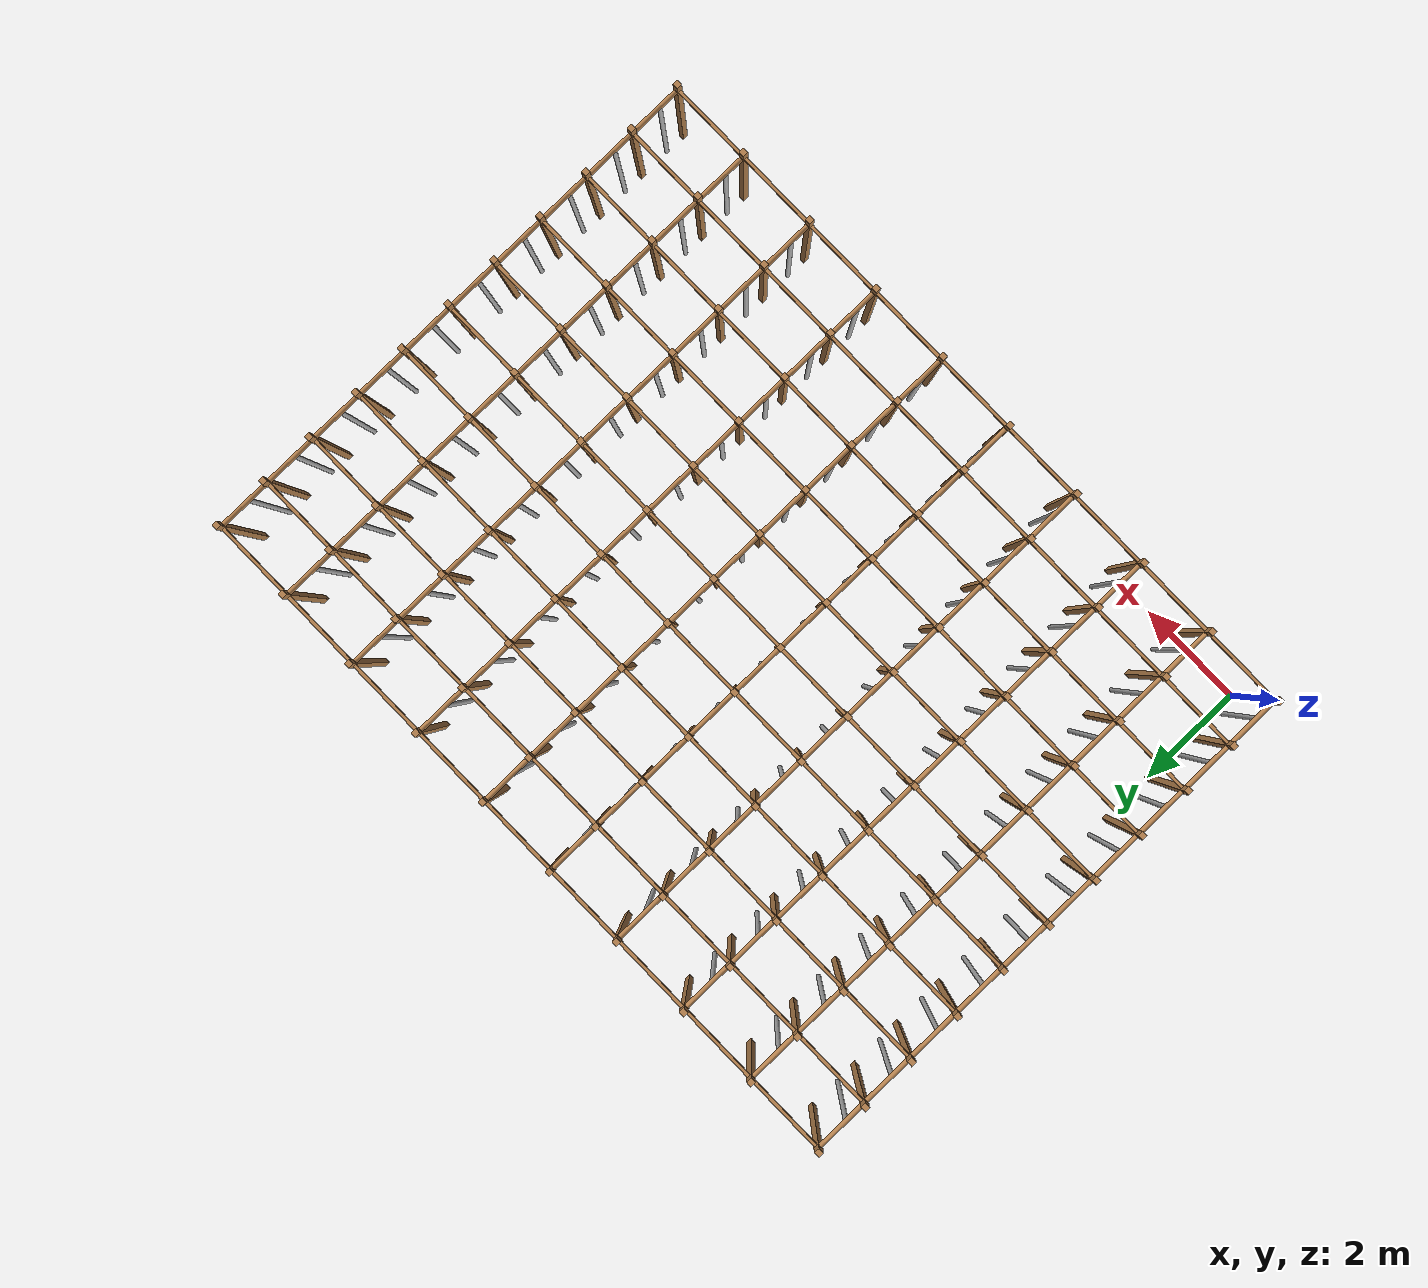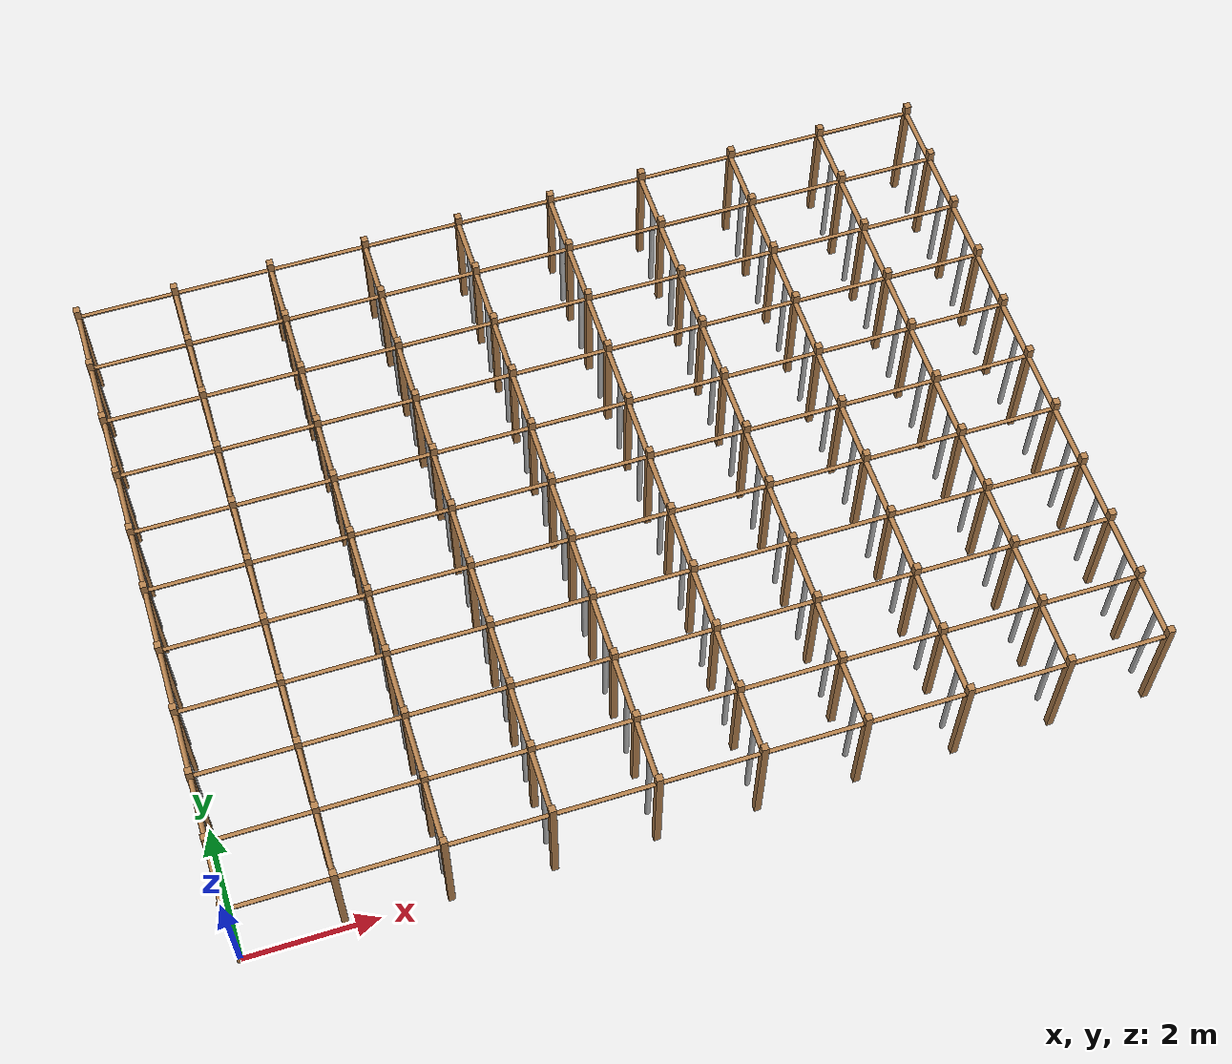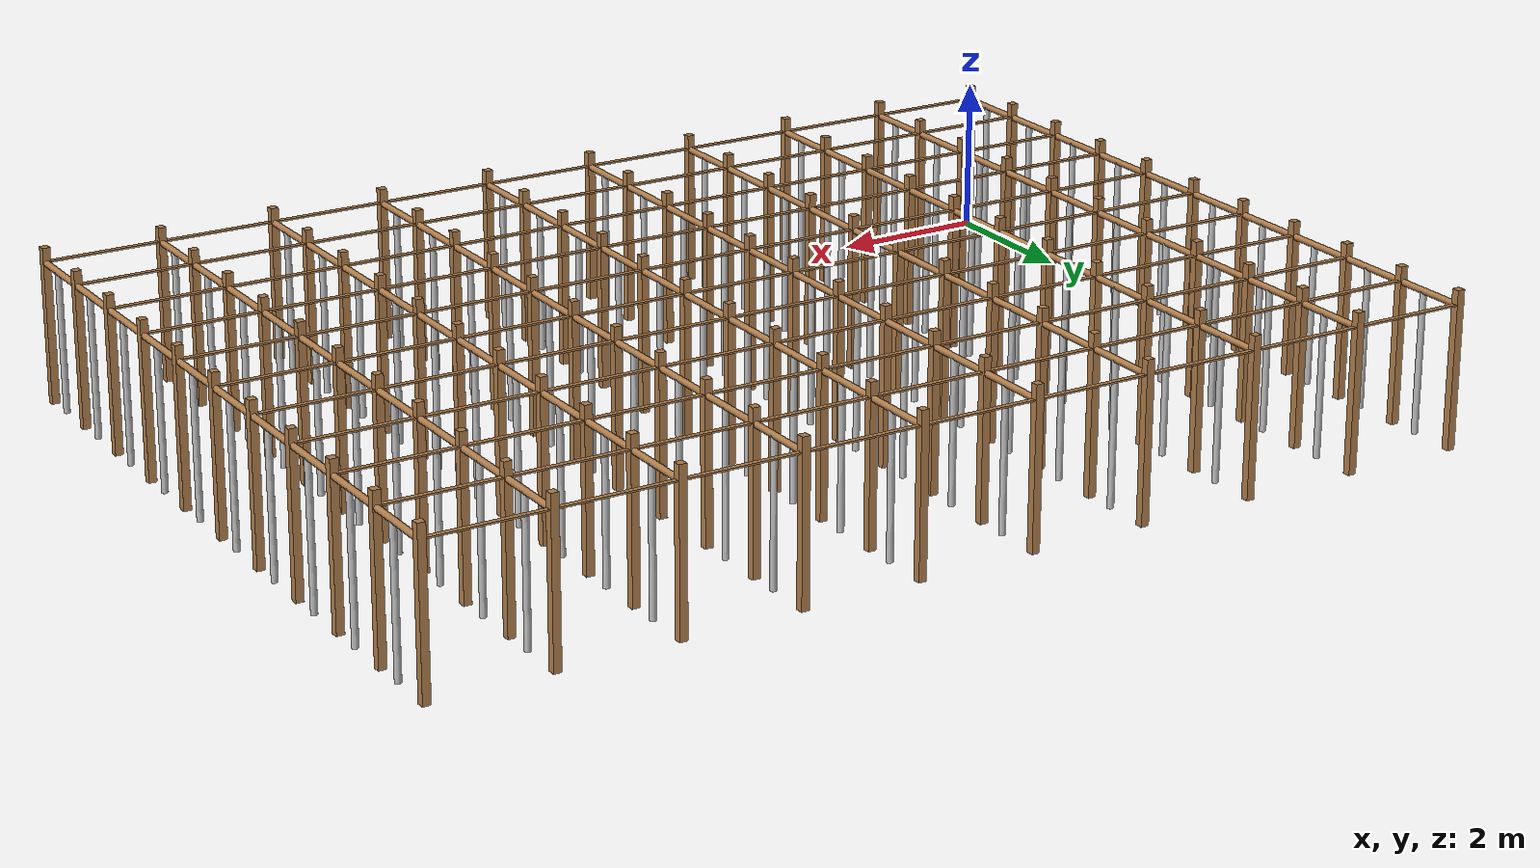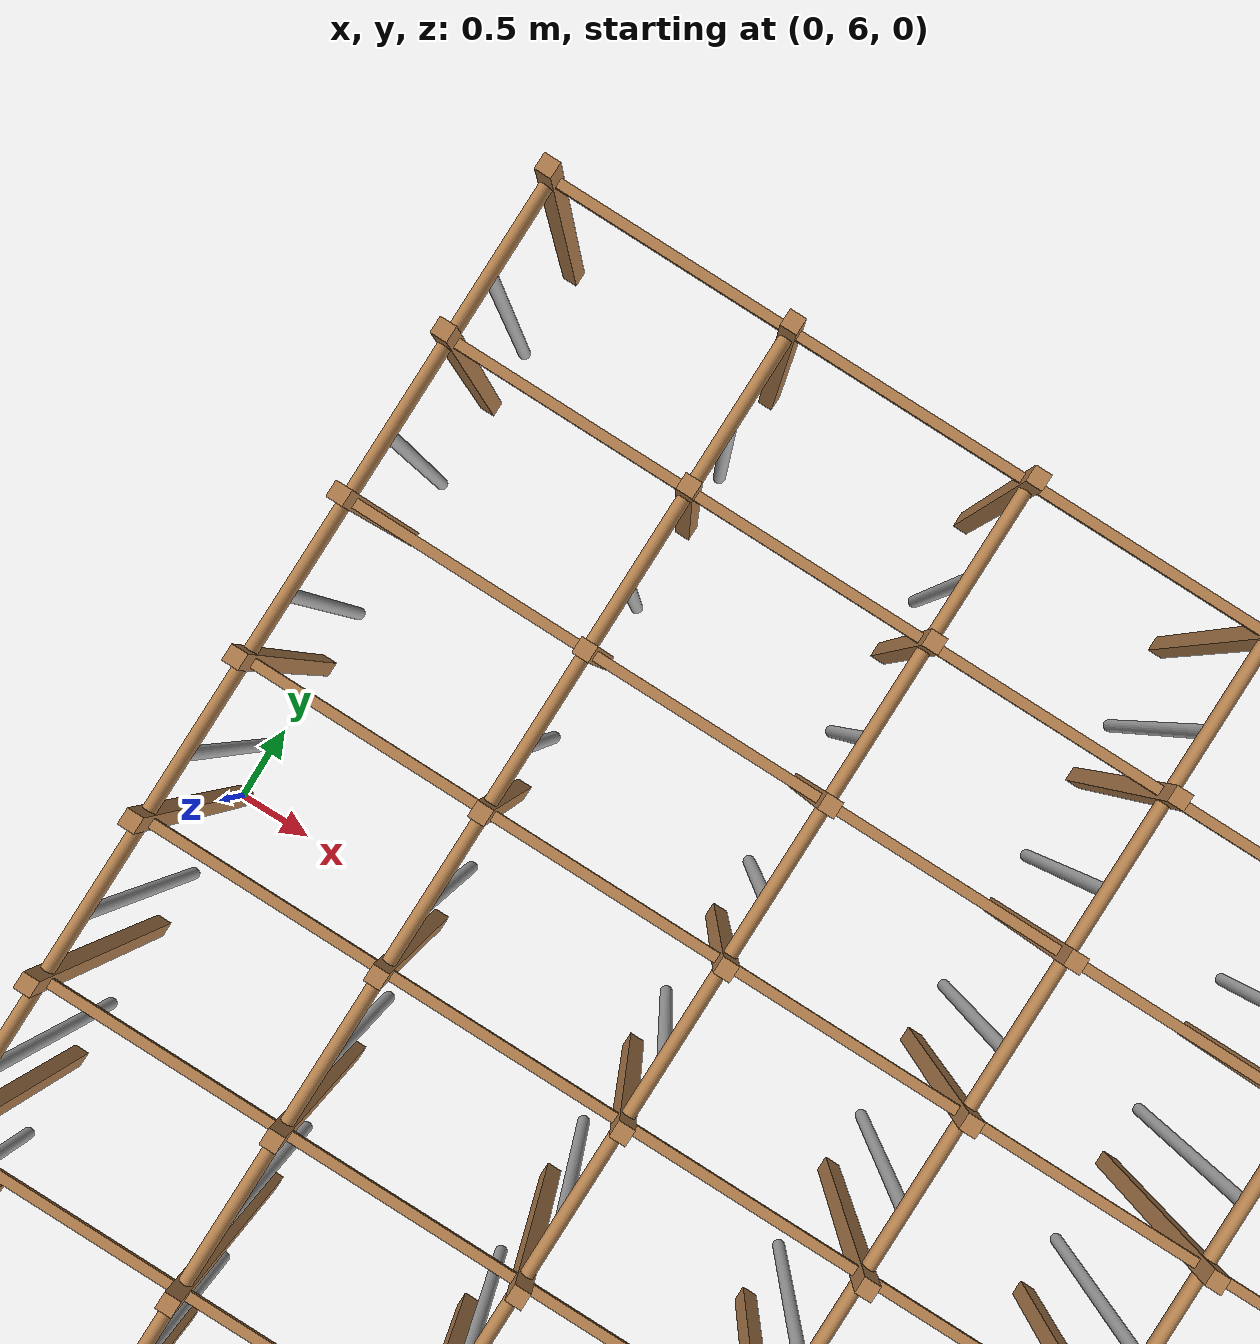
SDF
<?xml version='1.0'?>
<!-- This model file describes a pergola with no vines or fruit. -->
<sdf version='1.4'>
  <model name="pergola">

		<include>
			<name>post_0</name>
			<pose>0.0 0.0 0 0 0 0</pose>
			<uri>model://post</uri>
		</include>

		<include>
			<name>post_1</name>
			<pose>0.0 1.0 0 0 0 0</pose>
			<uri>model://post</uri>
		</include>

		<include>
			<name>post_2</name>
			<pose>0.0 2.0 0 0 0 0</pose>
			<uri>model://post</uri>
		</include>

		<include>
			<name>post_3</name>
			<pose>0.0 3.0 0 0 0 0</pose>
			<uri>model://post</uri>
		</include>

		<include>
			<name>post_4</name>
			<pose>0.0 4.0 0 0 0 0</pose>
			<uri>model://post</uri>
		</include>

		<include>
			<name>post_5</name>
			<pose>0.0 5.0 0 0 0 0</pose>
			<uri>model://post</uri>
		</include>

		<include>
			<name>post_6</name>
			<pose>0.0 6.0 0 0 0 0</pose>
			<uri>model://post</uri>
		</include>

		<include>
			<name>post_7</name>
			<pose>0.0 7.0 0 0 0 0</pose>
			<uri>model://post</uri>
		</include>

		<include>
			<name>post_8</name>
			<pose>0.0 8.0 0 0 0 0</pose>
			<uri>model://post</uri>
		</include>

		<include>
			<name>post_9</name>
			<pose>0.0 9.0 0 0 0 0</pose>
			<uri>model://post</uri>
		</include>

		<include>
			<name>post_10</name>
			<pose>0.0 10.0 0 0 0 0</pose>
			<uri>model://post</uri>
		</include>

		<include>
			<name>post_11</name>
			<pose>1.5 0.0 0 0 0 0</pose>
			<uri>model://post</uri>
		</include>

		<include>
			<name>post_12</name>
			<pose>1.5 1.0 0 0 0 0</pose>
			<uri>model://post</uri>
		</include>

		<include>
			<name>post_13</name>
			<pose>1.5 2.0 0 0 0 0</pose>
			<uri>model://post</uri>
		</include>

		<include>
			<name>post_14</name>
			<pose>1.5 3.0 0 0 0 0</pose>
			<uri>model://post</uri>
		</include>

		<include>
			<name>post_15</name>
			<pose>1.5 4.0 0 0 0 0</pose>
			<uri>model://post</uri>
		</include>

		<include>
			<name>post_16</name>
			<pose>1.5 5.0 0 0 0 0</pose>
			<uri>model://post</uri>
		</include>

		<include>
			<name>post_17</name>
			<pose>1.5 6.0 0 0 0 0</pose>
			<uri>model://post</uri>
		</include>

		<include>
			<name>post_18</name>
			<pose>1.5 7.0 0 0 0 0</pose>
			<uri>model://post</uri>
		</include>

		<include>
			<name>post_19</name>
			<pose>1.5 8.0 0 0 0 0</pose>
			<uri>model://post</uri>
		</include>

		<include>
			<name>post_20</name>
			<pose>1.5 9.0 0 0 0 0</pose>
			<uri>model://post</uri>
		</include>

		<include>
			<name>post_21</name>
			<pose>1.5 10.0 0 0 0 0</pose>
			<uri>model://post</uri>
		</include>

		<include>
			<name>post_22</name>
			<pose>3.0 0.0 0 0 0 0</pose>
			<uri>model://post</uri>
		</include>

		<include>
			<name>post_23</name>
			<pose>3.0 1.0 0 0 0 0</pose>
			<uri>model://post</uri>
		</include>

		<include>
			<name>post_24</name>
			<pose>3.0 2.0 0 0 0 0</pose>
			<uri>model://post</uri>
		</include>

		<include>
			<name>post_25</name>
			<pose>3.0 3.0 0 0 0 0</pose>
			<uri>model://post</uri>
		</include>

		<include>
			<name>post_26</name>
			<pose>3.0 4.0 0 0 0 0</pose>
			<uri>model://post</uri>
		</include>

		<include>
			<name>post_27</name>
			<pose>3.0 5.0 0 0 0 0</pose>
			<uri>model://post</uri>
		</include>

		<include>
			<name>post_28</name>
			<pose>3.0 6.0 0 0 0 0</pose>
			<uri>model://post</uri>
		</include>

		<include>
			<name>post_29</name>
			<pose>3.0 7.0 0 0 0 0</pose>
			<uri>model://post</uri>
		</include>

		<include>
			<name>post_30</name>
			<pose>3.0 8.0 0 0 0 0</pose>
			<uri>model://post</uri>
		</include>

		<include>
			<name>post_31</name>
			<pose>3.0 9.0 0 0 0 0</pose>
			<uri>model://post</uri>
		</include>

		<include>
			<name>post_32</name>
			<pose>3.0 10.0 0 0 0 0</pose>
			<uri>model://post</uri>
		</include>

		<include>
			<name>post_33</name>
			<pose>4.5 0.0 0 0 0 0</pose>
			<uri>model://post</uri>
		</include>

		<include>
			<name>post_34</name>
			<pose>4.5 1.0 0 0 0 0</pose>
			<uri>model://post</uri>
		</include>

		<include>
			<name>post_35</name>
			<pose>4.5 2.0 0 0 0 0</pose>
			<uri>model://post</uri>
		</include>

		<include>
			<name>post_36</name>
			<pose>4.5 3.0 0 0 0 0</pose>
			<uri>model://post</uri>
		</include>

		<include>
			<name>post_37</name>
			<pose>4.5 4.0 0 0 0 0</pose>
			<uri>model://post</uri>
		</include>

		<include>
			<name>post_38</name>
			<pose>4.5 5.0 0 0 0 0</pose>
			<uri>model://post</uri>
		</include>

		<include>
			<name>post_39</name>
			<pose>4.5 6.0 0 0 0 0</pose>
			<uri>model://post</uri>
		</include>

		<include>
			<name>post_40</name>
			<pose>4.5 7.0 0 0 0 0</pose>
			<uri>model://post</uri>
		</include>

		<include>
			<name>post_41</name>
			<pose>4.5 8.0 0 0 0 0</pose>
			<uri>model://post</uri>
		</include>

		<include>
			<name>post_42</name>
			<pose>4.5 9.0 0 0 0 0</pose>
			<uri>model://post</uri>
		</include>

		<include>
			<name>post_43</name>
			<pose>4.5 10.0 0 0 0 0</pose>
			<uri>model://post</uri>
		</include>

		<include>
			<name>post_44</name>
			<pose>6.0 0.0 0 0 0 0</pose>
			<uri>model://post</uri>
		</include>

		<include>
			<name>post_45</name>
			<pose>6.0 1.0 0 0 0 0</pose>
			<uri>model://post</uri>
		</include>

		<include>
			<name>post_46</name>
			<pose>6.0 2.0 0 0 0 0</pose>
			<uri>model://post</uri>
		</include>

		<include>
			<name>post_47</name>
			<pose>6.0 3.0 0 0 0 0</pose>
			<uri>model://post</uri>
		</include>

		<include>
			<name>post_48</name>
			<pose>6.0 4.0 0 0 0 0</pose>
			<uri>model://post</uri>
		</include>

		<include>
			<name>post_49</name>
			<pose>6.0 5.0 0 0 0 0</pose>
			<uri>model://post</uri>
		</include>

		<include>
			<name>post_50</name>
			<pose>6.0 6.0 0 0 0 0</pose>
			<uri>model://post</uri>
		</include>

		<include>
			<name>post_51</name>
			<pose>6.0 7.0 0 0 0 0</pose>
			<uri>model://post</uri>
		</include>

		<include>
			<name>post_52</name>
			<pose>6.0 8.0 0 0 0 0</pose>
			<uri>model://post</uri>
		</include>

		<include>
			<name>post_53</name>
			<pose>6.0 9.0 0 0 0 0</pose>
			<uri>model://post</uri>
		</include>

		<include>
			<name>post_54</name>
			<pose>6.0 10.0 0 0 0 0</pose>
			<uri>model://post</uri>
		</include>

		<include>
			<name>post_55</name>
			<pose>7.5 0.0 0 0 0 0</pose>
			<uri>model://post</uri>
		</include>

		<include>
			<name>post_56</name>
			<pose>7.5 1.0 0 0 0 0</pose>
			<uri>model://post</uri>
		</include>

		<include>
			<name>post_57</name>
			<pose>7.5 2.0 0 0 0 0</pose>
			<uri>model://post</uri>
		</include>

		<include>
			<name>post_58</name>
			<pose>7.5 3.0 0 0 0 0</pose>
			<uri>model://post</uri>
		</include>

		<include>
			<name>post_59</name>
			<pose>7.5 4.0 0 0 0 0</pose>
			<uri>model://post</uri>
		</include>

		<include>
			<name>post_60</name>
			<pose>7.5 5.0 0 0 0 0</pose>
			<uri>model://post</uri>
		</include>

		<include>
			<name>post_61</name>
			<pose>7.5 6.0 0 0 0 0</pose>
			<uri>model://post</uri>
		</include>

		<include>
			<name>post_62</name>
			<pose>7.5 7.0 0 0 0 0</pose>
			<uri>model://post</uri>
		</include>

		<include>
			<name>post_63</name>
			<pose>7.5 8.0 0 0 0 0</pose>
			<uri>model://post</uri>
		</include>

		<include>
			<name>post_64</name>
			<pose>7.5 9.0 0 0 0 0</pose>
			<uri>model://post</uri>
		</include>

		<include>
			<name>post_65</name>
			<pose>7.5 10.0 0 0 0 0</pose>
			<uri>model://post</uri>
		</include>

		<include>
			<name>post_66</name>
			<pose>9.0 0.0 0 0 0 0</pose>
			<uri>model://post</uri>
		</include>

		<include>
			<name>post_67</name>
			<pose>9.0 1.0 0 0 0 0</pose>
			<uri>model://post</uri>
		</include>

		<include>
			<name>post_68</name>
			<pose>9.0 2.0 0 0 0 0</pose>
			<uri>model://post</uri>
		</include>

		<include>
			<name>post_69</name>
			<pose>9.0 3.0 0 0 0 0</pose>
			<uri>model://post</uri>
		</include>

		<include>
			<name>post_70</name>
			<pose>9.0 4.0 0 0 0 0</pose>
			<uri>model://post</uri>
		</include>

		<include>
			<name>post_71</name>
			<pose>9.0 5.0 0 0 0 0</pose>
			<uri>model://post</uri>
		</include>

		<include>
			<name>post_72</name>
			<pose>9.0 6.0 0 0 0 0</pose>
			<uri>model://post</uri>
		</include>

		<include>
			<name>post_73</name>
			<pose>9.0 7.0 0 0 0 0</pose>
			<uri>model://post</uri>
		</include>

		<include>
			<name>post_74</name>
			<pose>9.0 8.0 0 0 0 0</pose>
			<uri>model://post</uri>
		</include>

		<include>
			<name>post_75</name>
			<pose>9.0 9.0 0 0 0 0</pose>
			<uri>model://post</uri>
		</include>

		<include>
			<name>post_76</name>
			<pose>9.0 10.0 0 0 0 0</pose>
			<uri>model://post</uri>
		</include>

		<include>
			<name>post_77</name>
			<pose>10.5 0.0 0 0 0 0</pose>
			<uri>model://post</uri>
		</include>

		<include>
			<name>post_78</name>
			<pose>10.5 1.0 0 0 0 0</pose>
			<uri>model://post</uri>
		</include>

		<include>
			<name>post_79</name>
			<pose>10.5 2.0 0 0 0 0</pose>
			<uri>model://post</uri>
		</include>

		<include>
			<name>post_80</name>
			<pose>10.5 3.0 0 0 0 0</pose>
			<uri>model://post</uri>
		</include>

		<include>
			<name>post_81</name>
			<pose>10.5 4.0 0 0 0 0</pose>
			<uri>model://post</uri>
		</include>

		<include>
			<name>post_82</name>
			<pose>10.5 5.0 0 0 0 0</pose>
			<uri>model://post</uri>
		</include>

		<include>
			<name>post_83</name>
			<pose>10.5 6.0 0 0 0 0</pose>
			<uri>model://post</uri>
		</include>

		<include>
			<name>post_84</name>
			<pose>10.5 7.0 0 0 0 0</pose>
			<uri>model://post</uri>
		</include>

		<include>
			<name>post_85</name>
			<pose>10.5 8.0 0 0 0 0</pose>
			<uri>model://post</uri>
		</include>

		<include>
			<name>post_86</name>
			<pose>10.5 9.0 0 0 0 0</pose>
			<uri>model://post</uri>
		</include>

		<include>
			<name>post_87</name>
			<pose>10.5 10.0 0 0 0 0</pose>
			<uri>model://post</uri>
		</include>

		<include>
			<name>post_88</name>
			<pose>12.0 0.0 0 0 0 0</pose>
			<uri>model://post</uri>
		</include>

		<include>
			<name>post_89</name>
			<pose>12.0 1.0 0 0 0 0</pose>
			<uri>model://post</uri>
		</include>

		<include>
			<name>post_90</name>
			<pose>12.0 2.0 0 0 0 0</pose>
			<uri>model://post</uri>
		</include>

		<include>
			<name>post_91</name>
			<pose>12.0 3.0 0 0 0 0</pose>
			<uri>model://post</uri>
		</include>

		<include>
			<name>post_92</name>
			<pose>12.0 4.0 0 0 0 0</pose>
			<uri>model://post</uri>
		</include>

		<include>
			<name>post_93</name>
			<pose>12.0 5.0 0 0 0 0</pose>
			<uri>model://post</uri>
		</include>

		<include>
			<name>post_94</name>
			<pose>12.0 6.0 0 0 0 0</pose>
			<uri>model://post</uri>
		</include>

		<include>
			<name>post_95</name>
			<pose>12.0 7.0 0 0 0 0</pose>
			<uri>model://post</uri>
		</include>

		<include>
			<name>post_96</name>
			<pose>12.0 8.0 0 0 0 0</pose>
			<uri>model://post</uri>
		</include>

		<include>
			<name>post_97</name>
			<pose>12.0 9.0 0 0 0 0</pose>
			<uri>model://post</uri>
		</include>

		<include>
			<name>post_98</name>
			<pose>12.0 10.0 0 0 0 0</pose>
			<uri>model://post</uri>
		</include>

		<include>
			<name>post_99</name>
			<pose>13.5 0.0 0 0 0 0</pose>
			<uri>model://post</uri>
		</include>

		<include>
			<name>post_100</name>
			<pose>13.5 1.0 0 0 0 0</pose>
			<uri>model://post</uri>
		</include>

		<include>
			<name>post_101</name>
			<pose>13.5 2.0 0 0 0 0</pose>
			<uri>model://post</uri>
		</include>

		<include>
			<name>post_102</name>
			<pose>13.5 3.0 0 0 0 0</pose>
			<uri>model://post</uri>
		</include>

		<include>
			<name>post_103</name>
			<pose>13.5 4.0 0 0 0 0</pose>
			<uri>model://post</uri>
		</include>

		<include>
			<name>post_104</name>
			<pose>13.5 5.0 0 0 0 0</pose>
			<uri>model://post</uri>
		</include>

		<include>
			<name>post_105</name>
			<pose>13.5 6.0 0 0 0 0</pose>
			<uri>model://post</uri>
		</include>

		<include>
			<name>post_106</name>
			<pose>13.5 7.0 0 0 0 0</pose>
			<uri>model://post</uri>
		</include>

		<include>
			<name>post_107</name>
			<pose>13.5 8.0 0 0 0 0</pose>
			<uri>model://post</uri>
		</include>

		<include>
			<name>post_108</name>
			<pose>13.5 9.0 0 0 0 0</pose>
			<uri>model://post</uri>
		</include>

		<include>
			<name>post_109</name>
			<pose>13.5 10.0 0 0 0 0</pose>
			<uri>model://post</uri>
		</include>

    <link name="beam_0">
      <pose>0.75 0.0 1.81 0 0 0</pose>
      <collision name="collision">
        <geometry><box><size>1.5 0.06 0.02</size></box></geometry>
      </collision>
      <visual name="visual">
        <geometry><box><size>1.5 0.06 0.02</size></box></geometry>
        <material><script><name>Gazebo/Wood</name></script></material>
      </visual>
    <inertial>
      <pose>0 0 0 0 0 0</pose>
      <mass>5</mass>
      <inertia>
        <ixx>0.0016666666666666668</ixx><ixy>0.0</ixy><ixz>0.0</ixz><iyy>0.9390000000000001</iyy><iyz>0.0</iyz><izz>0.9376666666666665</izz>
      </inertia>
    </inertial>
    </link>

    <link name="beam_1">
      <pose>0.75 1.0 1.81 0 0 0</pose>
      <collision name="collision">
        <geometry><box><size>1.5 0.06 0.02</size></box></geometry>
      </collision>
      <visual name="visual">
        <geometry><box><size>1.5 0.06 0.02</size></box></geometry>
        <material><script><name>Gazebo/Wood</name></script></material>
      </visual>
    <inertial>
      <pose>0 0 0 0 0 0</pose>
      <mass>5</mass>
      <inertia>
        <ixx>0.0016666666666666668</ixx><ixy>0.0</ixy><ixz>0.0</ixz><iyy>0.9390000000000001</iyy><iyz>0.0</iyz><izz>0.9376666666666665</izz>
      </inertia>
    </inertial>
    </link>

    <link name="beam_2">
      <pose>0.75 2.0 1.81 0 0 0</pose>
      <collision name="collision">
        <geometry><box><size>1.5 0.06 0.02</size></box></geometry>
      </collision>
      <visual name="visual">
        <geometry><box><size>1.5 0.06 0.02</size></box></geometry>
        <material><script><name>Gazebo/Wood</name></script></material>
      </visual>
    <inertial>
      <pose>0 0 0 0 0 0</pose>
      <mass>5</mass>
      <inertia>
        <ixx>0.0016666666666666668</ixx><ixy>0.0</ixy><ixz>0.0</ixz><iyy>0.9390000000000001</iyy><iyz>0.0</iyz><izz>0.9376666666666665</izz>
      </inertia>
    </inertial>
    </link>

    <link name="beam_3">
      <pose>0.75 3.0 1.81 0 0 0</pose>
      <collision name="collision">
        <geometry><box><size>1.5 0.06 0.02</size></box></geometry>
      </collision>
      <visual name="visual">
        <geometry><box><size>1.5 0.06 0.02</size></box></geometry>
        <material><script><name>Gazebo/Wood</name></script></material>
      </visual>
    <inertial>
      <pose>0 0 0 0 0 0</pose>
      <mass>5</mass>
      <inertia>
        <ixx>0.0016666666666666668</ixx><ixy>0.0</ixy><ixz>0.0</ixz><iyy>0.9390000000000001</iyy><iyz>0.0</iyz><izz>0.9376666666666665</izz>
      </inertia>
    </inertial>
    </link>

    <link name="beam_4">
      <pose>0.75 4.0 1.81 0 0 0</pose>
      <collision name="collision">
        <geometry><box><size>1.5 0.06 0.02</size></box></geometry>
      </collision>
      <visual name="visual">
        <geometry><box><size>1.5 0.06 0.02</size></box></geometry>
        <material><script><name>Gazebo/Wood</name></script></material>
      </visual>
    <inertial>
      <pose>0 0 0 0 0 0</pose>
      <mass>5</mass>
      <inertia>
        <ixx>0.0016666666666666668</ixx><ixy>0.0</ixy><ixz>0.0</ixz><iyy>0.9390000000000001</iyy><iyz>0.0</iyz><izz>0.9376666666666665</izz>
      </inertia>
    </inertial>
    </link>

    <link name="beam_5">
      <pose>0.75 5.0 1.81 0 0 0</pose>
      <collision name="collision">
        <geometry><box><size>1.5 0.06 0.02</size></box></geometry>
      </collision>
      <visual name="visual">
        <geometry><box><size>1.5 0.06 0.02</size></box></geometry>
        <material><script><name>Gazebo/Wood</name></script></material>
      </visual>
    <inertial>
      <pose>0 0 0 0 0 0</pose>
      <mass>5</mass>
      <inertia>
        <ixx>0.0016666666666666668</ixx><ixy>0.0</ixy><ixz>0.0</ixz><iyy>0.9390000000000001</iyy><iyz>0.0</iyz><izz>0.9376666666666665</izz>
      </inertia>
    </inertial>
    </link>

    <link name="beam_6">
      <pose>0.75 6.0 1.81 0 0 0</pose>
      <collision name="collision">
        <geometry><box><size>1.5 0.06 0.02</size></box></geometry>
      </collision>
      <visual name="visual">
        <geometry><box><size>1.5 0.06 0.02</size></box></geometry>
        <material><script><name>Gazebo/Wood</name></script></material>
      </visual>
    <inertial>
      <pose>0 0 0 0 0 0</pose>
      <mass>5</mass>
      <inertia>
        <ixx>0.0016666666666666668</ixx><ixy>0.0</ixy><ixz>0.0</ixz><iyy>0.9390000000000001</iyy><iyz>0.0</iyz><izz>0.9376666666666665</izz>
      </inertia>
    </inertial>
    </link>

    <link name="beam_7">
      <pose>0.75 7.0 1.81 0 0 0</pose>
      <collision name="collision">
        <geometry><box><size>1.5 0.06 0.02</size></box></geometry>
      </collision>
      <visual name="visual">
        <geometry><box><size>1.5 0.06 0.02</size></box></geometry>
        <material><script><name>Gazebo/Wood</name></script></material>
      </visual>
    <inertial>
      <pose>0 0 0 0 0 0</pose>
      <mass>5</mass>
      <inertia>
        <ixx>0.0016666666666666668</ixx><ixy>0.0</ixy><ixz>0.0</ixz><iyy>0.9390000000000001</iyy><iyz>0.0</iyz><izz>0.9376666666666665</izz>
      </inertia>
    </inertial>
    </link>

    <link name="beam_8">
      <pose>0.75 8.0 1.81 0 0 0</pose>
      <collision name="collision">
        <geometry><box><size>1.5 0.06 0.02</size></box></geometry>
      </collision>
      <visual name="visual">
        <geometry><box><size>1.5 0.06 0.02</size></box></geometry>
        <material><script><name>Gazebo/Wood</name></script></material>
      </visual>
    <inertial>
      <pose>0 0 0 0 0 0</pose>
      <mass>5</mass>
      <inertia>
        <ixx>0.0016666666666666668</ixx><ixy>0.0</ixy><ixz>0.0</ixz><iyy>0.9390000000000001</iyy><iyz>0.0</iyz><izz>0.9376666666666665</izz>
      </inertia>
    </inertial>
    </link>

    <link name="beam_9">
      <pose>0.75 9.0 1.81 0 0 0</pose>
      <collision name="collision">
        <geometry><box><size>1.5 0.06 0.02</size></box></geometry>
      </collision>
      <visual name="visual">
        <geometry><box><size>1.5 0.06 0.02</size></box></geometry>
        <material><script><name>Gazebo/Wood</name></script></material>
      </visual>
    <inertial>
      <pose>0 0 0 0 0 0</pose>
      <mass>5</mass>
      <inertia>
        <ixx>0.0016666666666666668</ixx><ixy>0.0</ixy><ixz>0.0</ixz><iyy>0.9390000000000001</iyy><iyz>0.0</iyz><izz>0.9376666666666665</izz>
      </inertia>
    </inertial>
    </link>

    <link name="beam_10">
      <pose>0.75 10.0 1.81 0 0 0</pose>
      <collision name="collision">
        <geometry><box><size>1.5 0.06 0.02</size></box></geometry>
      </collision>
      <visual name="visual">
        <geometry><box><size>1.5 0.06 0.02</size></box></geometry>
        <material><script><name>Gazebo/Wood</name></script></material>
      </visual>
    <inertial>
      <pose>0 0 0 0 0 0</pose>
      <mass>5</mass>
      <inertia>
        <ixx>0.0016666666666666668</ixx><ixy>0.0</ixy><ixz>0.0</ixz><iyy>0.9390000000000001</iyy><iyz>0.0</iyz><izz>0.9376666666666665</izz>
      </inertia>
    </inertial>
    </link>

    <link name="beam_11">
      <pose>2.25 0.0 1.81 0 0 0</pose>
      <collision name="collision">
        <geometry><box><size>1.5 0.06 0.02</size></box></geometry>
      </collision>
      <visual name="visual">
        <geometry><box><size>1.5 0.06 0.02</size></box></geometry>
        <material><script><name>Gazebo/Wood</name></script></material>
      </visual>
    <inertial>
      <pose>0 0 0 0 0 0</pose>
      <mass>5</mass>
      <inertia>
        <ixx>0.0016666666666666668</ixx><ixy>0.0</ixy><ixz>0.0</ixz><iyy>0.9390000000000001</iyy><iyz>0.0</iyz><izz>0.9376666666666665</izz>
      </inertia>
    </inertial>
    </link>

    <link name="beam_12">
      <pose>2.25 1.0 1.81 0 0 0</pose>
      <collision name="collision">
        <geometry><box><size>1.5 0.06 0.02</size></box></geometry>
      </collision>
      <visual name="visual">
        <geometry><box><size>1.5 0.06 0.02</size></box></geometry>
        <material><script><name>Gazebo/Wood</name></script></material>
      </visual>
    <inertial>
      <pose>0 0 0 0 0 0</pose>
      <mass>5</mass>
      <inertia>
        <ixx>0.0016666666666666668</ixx><ixy>0.0</ixy><ixz>0.0</ixz><iyy>0.9390000000000001</iyy><iyz>0.0</iyz><izz>0.9376666666666665</izz>
      </inertia>
    </inertial>
    </link>

    <link name="beam_13">
      <pose>2.25 2.0 1.81 0 0 0</pose>
      <collision name="collision">
        <geometry><box><size>1.5 0.06 0.02</size></box></geometry>
      </collision>
      <visual name="visual">
        <geometry><box><size>1.5 0.06 0.02</size></box></geometry>
        <material><script><name>Gazebo/Wood</name></script></material>
      </visual>
    <inertial>
      <pose>0 0 0 0 0 0</pose>
      <mass>5</mass>
      <inertia>
        <ixx>0.0016666666666666668</ixx><ixy>0.0</ixy><ixz>0.0</ixz><iyy>0.9390000000000001</iyy><iyz>0.0</iyz><izz>0.9376666666666665</izz>
      </inertia>
    </inertial>
    </link>

    <link name="beam_14">
      <pose>2.25 3.0 1.81 0 0 0</pose>
      <collision name="collision">
        <geometry><box><size>1.5 0.06 0.02</size></box></geometry>
      </collision>
      <visual name="visual">
        <geometry><box><size>1.5 0.06 0.02</size></box></geometry>
        <material><script><name>Gazebo/Wood</name></script></material>
      </visual>
    <inertial>
      <pose>0 0 0 0 0 0</pose>
      <mass>5</mass>
      <inertia>
        <ixx>0.0016666666666666668</ixx><ixy>0.0</ixy><ixz>0.0</ixz><iyy>0.9390000000000001</iyy><iyz>0.0</iyz><izz>0.9376666666666665</izz>
      </inertia>
    </inertial>
    </link>

    <link name="beam_15">
      <pose>2.25 4.0 1.81 0 0 0</pose>
      <collision name="collision">
        <geometry><box><size>1.5 0.06 0.02</size></box></geometry>
      </collision>
      <visual name="visual">
        <geometry><box><size>1.5 0.06 0.02</size></box></geometry>
        <material><script><name>Gazebo/Wood</name></script></material>
      </visual>
    <inertial>
      <pose>0 0 0 0 0 0</pose>
      <mass>5</mass>
      <inertia>
        <ixx>0.0016666666666666668</ixx><ixy>0.0</ixy><ixz>0.0</ixz><iyy>0.9390000000000001</iyy><iyz>0.0</iyz><izz>0.9376666666666665</izz>
      </inertia>
    </inertial>
    </link>

    <link name="beam_16">
      <pose>2.25 5.0 1.81 0 0 0</pose>
      <collision name="collision">
        <geometry><box><size>1.5 0.06 0.02</size></box></geometry>
      </collision>
      <visual name="visual">
        <geometry><box><size>1.5 0.06 0.02</size></box></geometry>
        <material><script><name>Gazebo/Wood</name></script></material>
      </visual>
    <inertial>
      <pose>0 0 0 0 0 0</pose>
      <mass>5</mass>
      <inertia>
        <ixx>0.0016666666666666668</ixx><ixy>0.0</ixy><ixz>0.0</ixz><iyy>0.9390000000000001</iyy><iyz>0.0</iyz><izz>0.9376666666666665</izz>
      </inertia>
    </inertial>
    </link>

    <link name="beam_17">
      <pose>2.25 6.0 1.81 0 0 0</pose>
      <collision name="collision">
        <geometry><box><size>1.5 0.06 0.02</size></box></geometry>
      </collision>
      <visual name="visual">
        <geometry><box><size>1.5 0.06 0.02</size></box></geometry>
        <material><script><name>Gazebo/Wood</name></script></material>
      </visual>
    <inertial>
      <pose>0 0 0 0 0 0</pose>
      <mass>5</mass>
      <inertia>
        <ixx>0.0016666666666666668</ixx><ixy>0.0</ixy><ixz>0.0</ixz><iyy>0.9390000000000001</iyy><iyz>0.0</iyz><izz>0.9376666666666665</izz>
      </inertia>
    </inertial>
    </link>

    <link name="beam_18">
      <pose>2.25 7.0 1.81 0 0 0</pose>
      <collision name="collision">
        <geometry><box><size>1.5 0.06 0.02</size></box></geometry>
      </collision>
      <visual name="visual">
        <geometry><box><size>1.5 0.06 0.02</size></box></geometry>
        <material><script><name>Gazebo/Wood</name></script></material>
      </visual>
    <inertial>
      <pose>0 0 0 0 0 0</pose>
      <mass>5</mass>
      <inertia>
        <ixx>0.0016666666666666668</ixx><ixy>0.0</ixy><ixz>0.0</ixz><iyy>0.9390000000000001</iyy><iyz>0.0</iyz><izz>0.9376666666666665</izz>
      </inertia>
    </inertial>
    </link>

    <link name="beam_19">
      <pose>2.25 8.0 1.81 0 0 0</pose>
      <collision name="collision">
        <geometry><box><size>1.5 0.06 0.02</size></box></geometry>
      </collision>
      <visual name="visual">
        <geometry><box><size>1.5 0.06 0.02</size></box></geometry>
        <material><script><name>Gazebo/Wood</name></script></material>
      </visual>
    <inertial>
      <pose>0 0 0 0 0 0</pose>
      <mass>5</mass>
      <inertia>
        <ixx>0.0016666666666666668</ixx><ixy>0.0</ixy><ixz>0.0</ixz><iyy>0.9390000000000001</iyy><iyz>0.0</iyz><izz>0.9376666666666665</izz>
      </inertia>
    </inertial>
    </link>

    <link name="beam_20">
      <pose>2.25 9.0 1.81 0 0 0</pose>
      <collision name="collision">
        <geometry><box><size>1.5 0.06 0.02</size></box></geometry>
      </collision>
      <visual name="visual">
        <geometry><box><size>1.5 0.06 0.02</size></box></geometry>
        <material><script><name>Gazebo/Wood</name></script></material>
      </visual>
    <inertial>
      <pose>0 0 0 0 0 0</pose>
      <mass>5</mass>
      <inertia>
        <ixx>0.0016666666666666668</ixx><ixy>0.0</ixy><ixz>0.0</ixz><iyy>0.9390000000000001</iyy><iyz>0.0</iyz><izz>0.9376666666666665</izz>
      </inertia>
    </inertial>
    </link>

    <link name="beam_21">
      <pose>2.25 10.0 1.81 0 0 0</pose>
      <collision name="collision">
        <geometry><box><size>1.5 0.06 0.02</size></box></geometry>
      </collision>
      <visual name="visual">
        <geometry><box><size>1.5 0.06 0.02</size></box></geometry>
        <material><script><name>Gazebo/Wood</name></script></material>
      </visual>
    <inertial>
      <pose>0 0 0 0 0 0</pose>
      <mass>5</mass>
      <inertia>
        <ixx>0.0016666666666666668</ixx><ixy>0.0</ixy><ixz>0.0</ixz><iyy>0.9390000000000001</iyy><iyz>0.0</iyz><izz>0.9376666666666665</izz>
      </inertia>
    </inertial>
    </link>

    <link name="beam_22">
      <pose>3.75 0.0 1.81 0 0 0</pose>
      <collision name="collision">
        <geometry><box><size>1.5 0.06 0.02</size></box></geometry>
      </collision>
      <visual name="visual">
        <geometry><box><size>1.5 0.06 0.02</size></box></geometry>
        <material><script><name>Gazebo/Wood</name></script></material>
      </visual>
    <inertial>
      <pose>0 0 0 0 0 0</pose>
      <mass>5</mass>
      <inertia>
        <ixx>0.0016666666666666668</ixx><ixy>0.0</ixy><ixz>0.0</ixz><iyy>0.9390000000000001</iyy><iyz>0.0</iyz><izz>0.9376666666666665</izz>
      </inertia>
    </inertial>
    </link>

    <link name="beam_23">
      <pose>3.75 1.0 1.81 0 0 0</pose>
      <collision name="collision">
        <geometry><box><size>1.5 0.06 0.02</size></box></geometry>
      </collision>
      <visual name="visual">
        <geometry><box><size>1.5 0.06 0.02</size></box></geometry>
        <material><script><name>Gazebo/Wood</name></script></material>
      </visual>
    <inertial>
      <pose>0 0 0 0 0 0</pose>
      <mass>5</mass>
      <inertia>
        <ixx>0.0016666666666666668</ixx><ixy>0.0</ixy><ixz>0.0</ixz><iyy>0.9390000000000001</iyy><iyz>0.0</iyz><izz>0.9376666666666665</izz>
      </inertia>
    </inertial>
    </link>

    <link name="beam_24">
      <pose>3.75 2.0 1.81 0 0 0</pose>
      <collision name="collision">
        <geometry><box><size>1.5 0.06 0.02</size></box></geometry>
      </collision>
      <visual name="visual">
        <geometry><box><size>1.5 0.06 0.02</size></box></geometry>
        <material><script><name>Gazebo/Wood</name></script></material>
      </visual>
    <inertial>
      <pose>0 0 0 0 0 0</pose>
      <mass>5</mass>
      <inertia>
        <ixx>0.0016666666666666668</ixx><ixy>0.0</ixy><ixz>0.0</ixz><iyy>0.9390000000000001</iyy><iyz>0.0</iyz><izz>0.9376666666666665</izz>
      </inertia>
    </inertial>
    </link>

    <link name="beam_25">
      <pose>3.75 3.0 1.81 0 0 0</pose>
      <collision name="collision">
        <geometry><box><size>1.5 0.06 0.02</size></box></geometry>
      </collision>
      <visual name="visual">
        <geometry><box><size>1.5 0.06 0.02</size></box></geometry>
        <material><script><name>Gazebo/Wood</name></script></material>
      </visual>
    <inertial>
      <pose>0 0 0 0 0 0</pose>
      <mass>5</mass>
      <inertia>
        <ixx>0.0016666666666666668</ixx><ixy>0.0</ixy><ixz>0.0</ixz><iyy>0.9390000000000001</iyy><iyz>0.0</iyz><izz>0.9376666666666665</izz>
      </inertia>
    </inertial>
    </link>

    <link name="beam_26">
      <pose>3.75 4.0 1.81 0 0 0</pose>
      <collision name="collision">
        <geometry><box><size>1.5 0.06 0.02</size></box></geometry>
      </collision>
      <visual name="visual">
        <geometry><box><size>1.5 0.06 0.02</size></box></geometry>
        <material><script><name>Gazebo/Wood</name></script></material>
      </visual>
    <inertial>
      <pose>0 0 0 0 0 0</pose>
      <mass>5</mass>
      <inertia>
        <ixx>0.0016666666666666668</ixx><ixy>0.0</ixy><ixz>0.0</ixz><iyy>0.9390000000000001</iyy><iyz>0.0</iyz><izz>0.9376666666666665</izz>
      </inertia>
    </inertial>
    </link>

    <link name="beam_27">
      <pose>3.75 5.0 1.81 0 0 0</pose>
      <collision name="collision">
        <geometry><box><size>1.5 0.06 0.02</size></box></geometry>
      </collision>
      <visual name="visual">
        <geometry><box><size>1.5 0.06 0.02</size></box></geometry>
        <material><script><name>Gazebo/Wood</name></script></material>
      </visual>
    <inertial>
      <pose>0 0 0 0 0 0</pose>
      <mass>5</mass>
      <inertia>
        <ixx>0.0016666666666666668</ixx><ixy>0.0</ixy><ixz>0.0</ixz><iyy>0.9390000000000001</iyy><iyz>0.0</iyz><izz>0.9376666666666665</izz>
      </inertia>
    </inertial>
    </link>

    <link name="beam_28">
      <pose>3.75 6.0 1.81 0 0 0</pose>
      <collision name="collision">
        <geometry><box><size>1.5 0.06 0.02</size></box></geometry>
      </collision>
      <visual name="visual">
        <geometry><box><size>1.5 0.06 0.02</size></box></geometry>
        <material><script><name>Gazebo/Wood</name></script></material>
      </visual>
    <inertial>
      <pose>0 0 0 0 0 0</pose>
      <mass>5</mass>
      <inertia>
        <ixx>0.0016666666666666668</ixx><ixy>0.0</ixy><ixz>0.0</ixz><iyy>0.9390000000000001</iyy><iyz>0.0</iyz><izz>0.9376666666666665</izz>
      </inertia>
    </inertial>
    </link>

    <link name="beam_29">
      <pose>3.75 7.0 1.81 0 0 0</pose>
      <collision name="collision">
        <geometry><box><size>1.5 0.06 0.02</size></box></geometry>
      </collision>
      <visual name="visual">
        <geometry><box><size>1.5 0.06 0.02</size></box></geometry>
        <material><script><name>Gazebo/Wood</name></script></material>
      </visual>
    <inertial>
      <pose>0 0 0 0 0 0</pose>
      <mass>5</mass>
      <inertia>
        <ixx>0.0016666666666666668</ixx><ixy>0.0</ixy><ixz>0.0</ixz><iyy>0.9390000000000001</iyy><iyz>0.0</iyz><izz>0.9376666666666665</izz>
      </inertia>
    </inertial>
    </link>

    <link name="beam_30">
      <pose>3.75 8.0 1.81 0 0 0</pose>
      <collision name="collision">
        <geometry><box><size>1.5 0.06 0.02</size></box></geometry>
      </collision>
      <visual name="visual">
        <geometry><box><size>1.5 0.06 0.02</size></box></geometry>
        <material><script><name>Gazebo/Wood</name></script></material>
      </visual>
    <inertial>
      <pose>0 0 0 0 0 0</pose>
      <mass>5</mass>
      <inertia>
        <ixx>0.0016666666666666668</ixx><ixy>0.0</ixy><ixz>0.0</ixz><iyy>0.9390000000000001</iyy><iyz>0.0</iyz><izz>0.9376666666666665</izz>
      </inertia>
    </inertial>
    </link>

    <link name="beam_31">
      <pose>3.75 9.0 1.81 0 0 0</pose>
      <collision name="collision">
        <geometry><box><size>1.5 0.06 0.02</size></box></geometry>
      </collision>
      <visual name="visual">
        <geometry><box><size>1.5 0.06 0.02</size></box></geometry>
        <material><script><name>Gazebo/Wood</name></script></material>
      </visual>
    <inertial>
      <pose>0 0 0 0 0 0</pose>
      <mass>5</mass>
      <inertia>
        <ixx>0.0016666666666666668</ixx><ixy>0.0</ixy><ixz>0.0</ixz><iyy>0.9390000000000001</iyy><iyz>0.0</iyz><izz>0.9376666666666665</izz>
      </inertia>
    </inertial>
    </link>

    <link name="beam_32">
      <pose>3.75 10.0 1.81 0 0 0</pose>
      <collision name="collision">
        <geometry><box><size>1.5 0.06 0.02</size></box></geometry>
      </collision>
      <visual name="visual">
        <geometry><box><size>1.5 0.06 0.02</size></box></geometry>
        <material><script><name>Gazebo/Wood</name></script></material>
      </visual>
    <inertial>
      <pose>0 0 0 0 0 0</pose>
      <mass>5</mass>
      <inertia>
        <ixx>0.0016666666666666668</ixx><ixy>0.0</ixy><ixz>0.0</ixz><iyy>0.9390000000000001</iyy><iyz>0.0</iyz><izz>0.9376666666666665</izz>
      </inertia>
    </inertial>
    </link>

    <link name="beam_33">
      <pose>5.25 0.0 1.81 0 0 0</pose>
      <collision name="collision">
        <geometry><box><size>1.5 0.06 0.02</size></box></geometry>
      </collision>
      <visual name="visual">
        <geometry><box><size>1.5 0.06 0.02</size></box></geometry>
        <material><script><name>Gazebo/Wood</name></script></material>
      </visual>
    <inertial>
      <pose>0 0 0 0 0 0</pose>
      <mass>5</mass>
      <inertia>
        <ixx>0.0016666666666666668</ixx><ixy>0.0</ixy><ixz>0.0</ixz><iyy>0.9390000000000001</iyy><iyz>0.0</iyz><izz>0.9376666666666665</izz>
      </inertia>
    </inertial>
    </link>

    <link name="beam_34">
      <pose>5.25 1.0 1.81 0 0 0</pose>
      <collision name="collision">
        <geometry><box><size>1.5 0.06 0.02</size></box></geometry>
      </collision>
      <visual name="visual">
        <geometry><box><size>1.5 0.06 0.02</size></box></geometry>
        <material><script><name>Gazebo/Wood</name></script></material>
      </visual>
    <inertial>
      <pose>0 0 0 0 0 0</pose>
      <mass>5</mass>
      <inertia>
        <ixx>0.0016666666666666668</ixx><ixy>0.0</ixy><ixz>0.0</ixz><iyy>0.9390000000000001</iyy><iyz>0.0</iyz><izz>0.9376666666666665</izz>
      </inertia>
    </inertial>
    </link>

    <link name="beam_35">
      <pose>5.25 2.0 1.81 0 0 0</pose>
      <collision name="collision">
        <geometry><box><size>1.5 0.06 0.02</size></box></geometry>
      </collision>
      <visual name="visual">
        <geometry><box><size>1.5 0.06 0.02</size></box></geometry>
        <material><script><name>Gazebo/Wood</name></script></material>
      </visual>
    <inertial>
      <pose>0 0 0 0 0 0</pose>
      <mass>5</mass>
      <inertia>
        <ixx>0.0016666666666666668</ixx><ixy>0.0</ixy><ixz>0.0</ixz><iyy>0.9390000000000001</iyy><iyz>0.0</iyz><izz>0.9376666666666665</izz>
      </inertia>
    </inertial>
    </link>

    <link name="beam_36">
      <pose>5.25 3.0 1.81 0 0 0</pose>
      <collision name="collision">
        <geometry><box><size>1.5 0.06 0.02</size></box></geometry>
      </collision>
      <visual name="visual">
        <geometry><box><size>1.5 0.06 0.02</size></box></geometry>
        <material><script><name>Gazebo/Wood</name></script></material>
      </visual>
    <inertial>
      <pose>0 0 0 0 0 0</pose>
      <mass>5</mass>
      <inertia>
        <ixx>0.0016666666666666668</ixx><ixy>0.0</ixy><ixz>0.0</ixz><iyy>0.9390000000000001</iyy><iyz>0.0</iyz><izz>0.9376666666666665</izz>
      </inertia>
    </inertial>
    </link>

    <link name="beam_37">
      <pose>5.25 4.0 1.81 0 0 0</pose>
      <collision name="collision">
        <geometry><box><size>1.5 0.06 0.02</size></box></geometry>
      </collision>
      <visual name="visual">
        <geometry><box><size>1.5 0.06 0.02</size></box></geometry>
        <material><script><name>Gazebo/Wood</name></script></material>
      </visual>
    <inertial>
      <pose>0 0 0 0 0 0</pose>
      <mass>5</mass>
      <inertia>
        <ixx>0.0016666666666666668</ixx><ixy>0.0</ixy><ixz>0.0</ixz><iyy>0.9390000000000001</iyy><iyz>0.0</iyz><izz>0.9376666666666665</izz>
      </inertia>
    </inertial>
    </link>

    <link name="beam_38">
      <pose>5.25 5.0 1.81 0 0 0</pose>
      <collision name="collision">
        <geometry><box><size>1.5 0.06 0.02</size></box></geometry>
      </collision>
      <visual name="visual">
        <geometry><box><size>1.5 0.06 0.02</size></box></geometry>
        <material><script><name>Gazebo/Wood</name></script></material>
      </visual>
    <inertial>
      <pose>0 0 0 0 0 0</pose>
      <mass>5</mass>
      <inertia>
        <ixx>0.0016666666666666668</ixx><ixy>0.0</ixy><ixz>0.0</ixz><iyy>0.9390000000000001</iyy><iyz>0.0</iyz><izz>0.9376666666666665</izz>
      </inertia>
    </inertial>
    </link>

    <link name="beam_39">
      <pose>5.25 6.0 1.81 0 0 0</pose>
      <collision name="collision">
        <geometry><box><size>1.5 0.06 0.02</size></box></geometry>
      </collision>
      <visual name="visual">
        <geometry><box><size>1.5 0.06 0.02</size></box></geometry>
        <material><script><name>Gazebo/Wood</name></script></material>
      </visual>
    <inertial>
      <pose>0 0 0 0 0 0</pose>
      <mass>5</mass>
      <inertia>
        <ixx>0.0016666666666666668</ixx><ixy>0.0</ixy><ixz>0.0</ixz><iyy>0.9390000000000001</iyy><iyz>0.0</iyz><izz>0.9376666666666665</izz>
      </inertia>
    </inertial>
    </link>

    <link name="beam_40">
      <pose>5.25 7.0 1.81 0 0 0</pose>
      <collision name="collision">
        <geometry><box><size>1.5 0.06 0.02</size></box></geometry>
      </collision>
      <visual name="visual">
        <geometry><box><size>1.5 0.06 0.02</size></box></geometry>
        <material><script><name>Gazebo/Wood</name></script></material>
      </visual>
    <inertial>
      <pose>0 0 0 0 0 0</pose>
      <mass>5</mass>
      <inertia>
        <ixx>0.0016666666666666668</ixx><ixy>0.0</ixy><ixz>0.0</ixz><iyy>0.9390000000000001</iyy><iyz>0.0</iyz><izz>0.9376666666666665</izz>
      </inertia>
    </inertial>
    </link>

    <link name="beam_41">
      <pose>5.25 8.0 1.81 0 0 0</pose>
      <collision name="collision">
        <geometry><box><size>1.5 0.06 0.02</size></box></geometry>
      </collision>
      <visual name="visual">
        <geometry><box><size>1.5 0.06 0.02</size></box></geometry>
        <material><script><name>Gazebo/Wood</name></script></material>
      </visual>
    <inertial>
      <pose>0 0 0 0 0 0</pose>
      <mass>5</mass>
      <inertia>
        <ixx>0.0016666666666666668</ixx><ixy>0.0</ixy><ixz>0.0</ixz><iyy>0.9390000000000001</iyy><iyz>0.0</iyz><izz>0.9376666666666665</izz>
      </inertia>
    </inertial>
    </link>

    <link name="beam_42">
      <pose>5.25 9.0 1.81 0 0 0</pose>
      <collision name="collision">
        <geometry><box><size>1.5 0.06 0.02</size></box></geometry>
      </collision>
      <visual name="visual">
        <geometry><box><size>1.5 0.06 0.02</size></box></geometry>
        <material><script><name>Gazebo/Wood</name></script></material>
      </visual>
    <inertial>
      <pose>0 0 0 0 0 0</pose>
      <mass>5</mass>
      <inertia>
        <ixx>0.0016666666666666668</ixx><ixy>0.0</ixy><ixz>0.0</ixz><iyy>0.9390000000000001</iyy><iyz>0.0</iyz><izz>0.9376666666666665</izz>
      </inertia>
    </inertial>
    </link>

    <link name="beam_43">
      <pose>5.25 10.0 1.81 0 0 0</pose>
      <collision name="collision">
        <geometry><box><size>1.5 0.06 0.02</size></box></geometry>
      </collision>
      <visual name="visual">
        <geometry><box><size>1.5 0.06 0.02</size></box></geometry>
        <material><script><name>Gazebo/Wood</name></script></material>
      </visual>
    <inertial>
      <pose>0 0 0 0 0 0</pose>
      <mass>5</mass>
      <inertia>
        <ixx>0.0016666666666666668</ixx><ixy>0.0</ixy><ixz>0.0</ixz><iyy>0.9390000000000001</iyy><iyz>0.0</iyz><izz>0.9376666666666665</izz>
      </inertia>
    </inertial>
    </link>

    <link name="beam_44">
      <pose>6.75 0.0 1.81 0 0 0</pose>
      <collision name="collision">
        <geometry><box><size>1.5 0.06 0.02</size></box></geometry>
      </collision>
      <visual name="visual">
        <geometry><box><size>1.5 0.06 0.02</size></box></geometry>
        <material><script><name>Gazebo/Wood</name></script></material>
      </visual>
    <inertial>
      <pose>0 0 0 0 0 0</pose>
      <mass>5</mass>
      <inertia>
        <ixx>0.0016666666666666668</ixx><ixy>0.0</ixy><ixz>0.0</ixz><iyy>0.9390000000000001</iyy><iyz>0.0</iyz><izz>0.9376666666666665</izz>
      </inertia>
    </inertial>
    </link>

    <link name="beam_45">
      <pose>6.75 1.0 1.81 0 0 0</pose>
      <collision name="collision">
        <geometry><box><size>1.5 0.06 0.02</size></box></geometry>
      </collision>
      <visual name="visual">
        <geometry><box><size>1.5 0.06 0.02</size></box></geometry>
        <material><script><name>Gazebo/Wood</name></script></material>
      </visual>
    <inertial>
      <pose>0 0 0 0 0 0</pose>
      <mass>5</mass>
      <inertia>
        <ixx>0.0016666666666666668</ixx><ixy>0.0</ixy><ixz>0.0</ixz><iyy>0.9390000000000001</iyy><iyz>0.0</iyz><izz>0.9376666666666665</izz>
      </inertia>
    </inertial>
    </link>

    <link name="beam_46">
      <pose>6.75 2.0 1.81 0 0 0</pose>
      <collision name="collision">
        <geometry><box><size>1.5 0.06 0.02</size></box></geometry>
      </collision>
      <visual name="visual">
        <geometry><box><size>1.5 0.06 0.02</size></box></geometry>
        <material><script><name>Gazebo/Wood</name></script></material>
      </visual>
    <inertial>
      <pose>0 0 0 0 0 0</pose>
      <mass>5</mass>
      <inertia>
        <ixx>0.0016666666666666668</ixx><ixy>0.0</ixy><ixz>0.0</ixz><iyy>0.9390000000000001</iyy><iyz>0.0</iyz><izz>0.9376666666666665</izz>
      </inertia>
    </inertial>
    </link>

    <link name="beam_47">
      <pose>6.75 3.0 1.81 0 0 0</pose>
      <collision name="collision">
        <geometry><box><size>1.5 0.06 0.02</size></box></geometry>
      </collision>
      <visual name="visual">
        <geometry><box><size>1.5 0.06 0.02</size></box></geometry>
        <material><script><name>Gazebo/Wood</name></script></material>
      </visual>
    <inertial>
      <pose>0 0 0 0 0 0</pose>
      <mass>5</mass>
      <inertia>
        <ixx>0.0016666666666666668</ixx><ixy>0.0</ixy><ixz>0.0</ixz><iyy>0.9390000000000001</iyy><iyz>0.0</iyz><izz>0.9376666666666665</izz>
      </inertia>
    </inertial>
    </link>

    <link name="beam_48">
      <pose>6.75 4.0 1.81 0 0 0</pose>
      <collision name="collision">
        <geometry><box><size>1.5 0.06 0.02</size></box></geometry>
      </collision>
      <visual name="visual">
        <geometry><box><size>1.5 0.06 0.02</size></box></geometry>
        <material><script><name>Gazebo/Wood</name></script></material>
      </visual>
    <inertial>
      <pose>0 0 0 0 0 0</pose>
      <mass>5</mass>
      <inertia>
        <ixx>0.0016666666666666668</ixx><ixy>0.0</ixy><ixz>0.0</ixz><iyy>0.9390000000000001</iyy><iyz>0.0</iyz><izz>0.9376666666666665</izz>
      </inertia>
    </inertial>
    </link>

    <link name="beam_49">
      <pose>6.75 5.0 1.81 0 0 0</pose>
      <collision name="collision">
        <geometry><box><size>1.5 0.06 0.02</size></box></geometry>
      </collision>
      <visual name="visual">
        <geometry><box><size>1.5 0.06 0.02</size></box></geometry>
        <material><script><name>Gazebo/Wood</name></script></material>
      </visual>
    <inertial>
      <pose>0 0 0 0 0 0</pose>
      <mass>5</mass>
      <inertia>
        <ixx>0.0016666666666666668</ixx><ixy>0.0</ixy><ixz>0.0</ixz><iyy>0.9390000000000001</iyy><iyz>0.0</iyz><izz>0.9376666666666665</izz>
      </inertia>
    </inertial>
    </link>

    <link name="beam_50">
      <pose>6.75 6.0 1.81 0 0 0</pose>
      <collision name="collision">
        <geometry><box><size>1.5 0.06 0.02</size></box></geometry>
      </collision>
      <visual name="visual">
        <geometry><box><size>1.5 0.06 0.02</size></box></geometry>
        <material><script><name>Gazebo/Wood</name></script></material>
      </visual>
    <inertial>
      <pose>0 0 0 0 0 0</pose>
      <mass>5</mass>
      <inertia>
        <ixx>0.0016666666666666668</ixx><ixy>0.0</ixy><ixz>0.0</ixz><iyy>0.9390000000000001</iyy><iyz>0.0</iyz><izz>0.9376666666666665</izz>
      </inertia>
    </inertial>
    </link>

    <link name="beam_51">
      <pose>6.75 7.0 1.81 0 0 0</pose>
      <collision name="collision">
        <geometry><box><size>1.5 0.06 0.02</size></box></geometry>
      </collision>
      <visual name="visual">
        <geometry><box><size>1.5 0.06 0.02</size></box></geometry>
        <material><script><name>Gazebo/Wood</name></script></material>
      </visual>
    <inertial>
      <pose>0 0 0 0 0 0</pose>
      <mass>5</mass>
      <inertia>
        <ixx>0.0016666666666666668</ixx><ixy>0.0</ixy><ixz>0.0</ixz><iyy>0.9390000000000001</iyy><iyz>0.0</iyz><izz>0.9376666666666665</izz>
      </inertia>
    </inertial>
    </link>

    <link name="beam_52">
      <pose>6.75 8.0 1.81 0 0 0</pose>
      <collision name="collision">
        <geometry><box><size>1.5 0.06 0.02</size></box></geometry>
      </collision>
      <visual name="visual">
        <geometry><box><size>1.5 0.06 0.02</size></box></geometry>
        <material><script><name>Gazebo/Wood</name></script></material>
      </visual>
    <inertial>
      <pose>0 0 0 0 0 0</pose>
      <mass>5</mass>
      <inertia>
        <ixx>0.0016666666666666668</ixx><ixy>0.0</ixy><ixz>0.0</ixz><iyy>0.9390000000000001</iyy><iyz>0.0</iyz><izz>0.9376666666666665</izz>
      </inertia>
    </inertial>
    </link>

    <link name="beam_53">
      <pose>6.75 9.0 1.81 0 0 0</pose>
      <collision name="collision">
        <geometry><box><size>1.5 0.06 0.02</size></box></geometry>
      </collision>
      <visual name="visual">
        <geometry><box><size>1.5 0.06 0.02</size></box></geometry>
        <material><script><name>Gazebo/Wood</name></script></material>
      </visual>
    <inertial>
      <pose>0 0 0 0 0 0</pose>
      <mass>5</mass>
      <inertia>
        <ixx>0.0016666666666666668</ixx><ixy>0.0</ixy><ixz>0.0</ixz><iyy>0.9390000000000001</iyy><iyz>0.0</iyz><izz>0.9376666666666665</izz>
      </inertia>
    </inertial>
    </link>

    <link name="beam_54">
      <pose>6.75 10.0 1.81 0 0 0</pose>
      <collision name="collision">
        <geometry><box><size>1.5 0.06 0.02</size></box></geometry>
      </collision>
      <visual name="visual">
        <geometry><box><size>1.5 0.06 0.02</size></box></geometry>
        <material><script><name>Gazebo/Wood</name></script></material>
      </visual>
    <inertial>
      <pose>0 0 0 0 0 0</pose>
      <mass>5</mass>
      <inertia>
        <ixx>0.0016666666666666668</ixx><ixy>0.0</ixy><ixz>0.0</ixz><iyy>0.9390000000000001</iyy><iyz>0.0</iyz><izz>0.9376666666666665</izz>
      </inertia>
    </inertial>
    </link>

    <link name="beam_55">
      <pose>8.25 0.0 1.81 0 0 0</pose>
      <collision name="collision">
        <geometry><box><size>1.5 0.06 0.02</size></box></geometry>
      </collision>
      <visual name="visual">
        <geometry><box><size>1.5 0.06 0.02</size></box></geometry>
        <material><script><name>Gazebo/Wood</name></script></material>
      </visual>
    <inertial>
      <pose>0 0 0 0 0 0</pose>
      <mass>5</mass>
      <inertia>
        <ixx>0.0016666666666666668</ixx><ixy>0.0</ixy><ixz>0.0</ixz><iyy>0.9390000000000001</iyy><iyz>0.0</iyz><izz>0.9376666666666665</izz>
      </inertia>
    </inertial>
    </link>

    <link name="beam_56">
      <pose>8.25 1.0 1.81 0 0 0</pose>
      <collision name="collision">
        <geometry><box><size>1.5 0.06 0.02</size></box></geometry>
      </collision>
      <visual name="visual">
        <geometry><box><size>1.5 0.06 0.02</size></box></geometry>
        <material><script><name>Gazebo/Wood</name></script></material>
      </visual>
    <inertial>
      <pose>0 0 0 0 0 0</pose>
      <mass>5</mass>
      <inertia>
        <ixx>0.0016666666666666668</ixx><ixy>0.0</ixy><ixz>0.0</ixz><iyy>0.9390000000000001</iyy><iyz>0.0</iyz><izz>0.9376666666666665</izz>
      </inertia>
    </inertial>
    </link>

    <link name="beam_57">
      <pose>8.25 2.0 1.81 0 0 0</pose>
      <collision name="collision">
        <geometry><box><size>1.5 0.06 0.02</size></box></geometry>
      </collision>
      <visual name="visual">
        <geometry><box><size>1.5 0.06 0.02</size></box></geometry>
        <material><script><name>Gazebo/Wood</name></script></material>
      </visual>
    <inertial>
      <pose>0 0 0 0 0 0</pose>
      <mass>5</mass>
      <inertia>
        <ixx>0.0016666666666666668</ixx><ixy>0.0</ixy><ixz>0.0</ixz><iyy>0.9390000000000001</iyy><iyz>0.0</iyz><izz>0.9376666666666665</izz>
      </inertia>
    </inertial>
    </link>

    <link name="beam_58">
      <pose>8.25 3.0 1.81 0 0 0</pose>
      <collision name="collision">
        <geometry><box><size>1.5 0.06 0.02</size></box></geometry>
      </collision>
      <visual name="visual">
        <geometry><box><size>1.5 0.06 0.02</size></box></geometry>
        <material><script><name>Gazebo/Wood</name></script></material>
      </visual>
    <inertial>
      <pose>0 0 0 0 0 0</pose>
      <mass>5</mass>
      <inertia>
        <ixx>0.0016666666666666668</ixx><ixy>0.0</ixy><ixz>0.0</ixz><iyy>0.9390000000000001</iyy><iyz>0.0</iyz><izz>0.9376666666666665</izz>
      </inertia>
    </inertial>
    </link>

    <link name="beam_59">
      <pose>8.25 4.0 1.81 0 0 0</pose>
      <collision name="collision">
        <geometry><box><size>1.5 0.06 0.02</size></box></geometry>
      </collision>
      <visual name="visual">
        <geometry><box><size>1.5 0.06 0.02</size></box></geometry>
        <material><script><name>Gazebo/Wood</name></script></material>
      </visual>
    <inertial>
      <pose>0 0 0 0 0 0</pose>
      <mass>5</mass>
      <inertia>
        <ixx>0.0016666666666666668</ixx><ixy>0.0</ixy><ixz>0.0</ixz><iyy>0.9390000000000001</iyy><iyz>0.0</iyz><izz>0.9376666666666665</izz>
      </inertia>
    </inertial>
    </link>

    <link name="beam_60">
      <pose>8.25 5.0 1.81 0 0 0</pose>
      <collision name="collision">
        <geometry><box><size>1.5 0.06 0.02</size></box></geometry>
      </collision>
      <visual name="visual">
        <geometry><box><size>1.5 0.06 0.02</size></box></geometry>
        <material><script><name>Gazebo/Wood</name></script></material>
      </visual>
    <inertial>
      <pose>0 0 0 0 0 0</pose>
      <mass>5</mass>
      <inertia>
        <ixx>0.0016666666666666668</ixx><ixy>0.0</ixy><ixz>0.0</ixz><iyy>0.9390000000000001</iyy><iyz>0.0</iyz><izz>0.9376666666666665</izz>
      </inertia>
    </inertial>
    </link>

    <link name="beam_61">
      <pose>8.25 6.0 1.81 0 0 0</pose>
      <collision name="collision">
        <geometry><box><size>1.5 0.06 0.02</size></box></geometry>
      </collision>
      <visual name="visual">
        <geometry><box><size>1.5 0.06 0.02</size></box></geometry>
        <material><script><name>Gazebo/Wood</name></script></material>
      </visual>
    <inertial>
      <pose>0 0 0 0 0 0</pose>
      <mass>5</mass>
      <inertia>
        <ixx>0.0016666666666666668</ixx><ixy>0.0</ixy><ixz>0.0</ixz><iyy>0.9390000000000001</iyy><iyz>0.0</iyz><izz>0.9376666666666665</izz>
      </inertia>
    </inertial>
    </link>

    <link name="beam_62">
      <pose>8.25 7.0 1.81 0 0 0</pose>
      <collision name="collision">
        <geometry><box><size>1.5 0.06 0.02</size></box></geometry>
      </collision>
      <visual name="visual">
        <geometry><box><size>1.5 0.06 0.02</size></box></geometry>
        <material><script><name>Gazebo/Wood</name></script></material>
      </visual>
    <inertial>
      <pose>0 0 0 0 0 0</pose>
      <mass>5</mass>
      <inertia>
        <ixx>0.0016666666666666668</ixx><ixy>0.0</ixy><ixz>0.0</ixz><iyy>0.9390000000000001</iyy><iyz>0.0</iyz><izz>0.9376666666666665</izz>
      </inertia>
    </inertial>
    </link>

    <link name="beam_63">
      <pose>8.25 8.0 1.81 0 0 0</pose>
      <collision name="collision">
        <geometry><box><size>1.5 0.06 0.02</size></box></geometry>
      </collision>
      <visual name="visual">
        <geometry><box><size>1.5 0.06 0.02</size></box></geometry>
        <material><script><name>Gazebo/Wood</name></script></material>
      </visual>
    <inertial>
      <pose>0 0 0 0 0 0</pose>
      <mass>5</mass>
      <inertia>
        <ixx>0.0016666666666666668</ixx><ixy>0.0</ixy><ixz>0.0</ixz><iyy>0.9390000000000001</iyy><iyz>0.0</iyz><izz>0.9376666666666665</izz>
      </inertia>
    </inertial>
    </link>

    <link name="beam_64">
      <pose>8.25 9.0 1.81 0 0 0</pose>
      <collision name="collision">
        <geometry><box><size>1.5 0.06 0.02</size></box></geometry>
      </collision>
      <visual name="visual">
        <geometry><box><size>1.5 0.06 0.02</size></box></geometry>
        <material><script><name>Gazebo/Wood</name></script></material>
      </visual>
    <inertial>
      <pose>0 0 0 0 0 0</pose>
      <mass>5</mass>
      <inertia>
        <ixx>0.0016666666666666668</ixx><ixy>0.0</ixy><ixz>0.0</ixz><iyy>0.9390000000000001</iyy><iyz>0.0</iyz><izz>0.9376666666666665</izz>
      </inertia>
    </inertial>
    </link>

    <link name="beam_65">
      <pose>8.25 10.0 1.81 0 0 0</pose>
      <collision name="collision">
        <geometry><box><size>1.5 0.06 0.02</size></box></geometry>
      </collision>
      <visual name="visual">
        <geometry><box><size>1.5 0.06 0.02</size></box></geometry>
        <material><script><name>Gazebo/Wood</name></script></material>
      </visual>
    <inertial>
      <pose>0 0 0 0 0 0</pose>
      <mass>5</mass>
      <inertia>
        <ixx>0.0016666666666666668</ixx><ixy>0.0</ixy><ixz>0.0</ixz><iyy>0.9390000000000001</iyy><iyz>0.0</iyz><izz>0.9376666666666665</izz>
      </inertia>
    </inertial>
    </link>

    <link name="beam_66">
      <pose>9.75 0.0 1.81 0 0 0</pose>
      <collision name="collision">
        <geometry><box><size>1.5 0.06 0.02</size></box></geometry>
      </collision>
      <visual name="visual">
        <geometry><box><size>1.5 0.06 0.02</size></box></geometry>
        <material><script><name>Gazebo/Wood</name></script></material>
      </visual>
    <inertial>
      <pose>0 0 0 0 0 0</pose>
      <mass>5</mass>
      <inertia>
        <ixx>0.0016666666666666668</ixx><ixy>0.0</ixy><ixz>0.0</ixz><iyy>0.9390000000000001</iyy><iyz>0.0</iyz><izz>0.9376666666666665</izz>
      </inertia>
    </inertial>
    </link>

    <link name="beam_67">
      <pose>9.75 1.0 1.81 0 0 0</pose>
      <collision name="collision">
        <geometry><box><size>1.5 0.06 0.02</size></box></geometry>
      </collision>
      <visual name="visual">
        <geometry><box><size>1.5 0.06 0.02</size></box></geometry>
        <material><script><name>Gazebo/Wood</name></script></material>
      </visual>
    <inertial>
      <pose>0 0 0 0 0 0</pose>
      <mass>5</mass>
      <inertia>
        <ixx>0.0016666666666666668</ixx><ixy>0.0</ixy><ixz>0.0</ixz><iyy>0.9390000000000001</iyy><iyz>0.0</iyz><izz>0.9376666666666665</izz>
      </inertia>
    </inertial>
    </link>

    <link name="beam_68">
      <pose>9.75 2.0 1.81 0 0 0</pose>
      <collision name="collision">
        <geometry><box><size>1.5 0.06 0.02</size></box></geometry>
      </collision>
      <visual name="visual">
        <geometry><box><size>1.5 0.06 0.02</size></box></geometry>
        <material><script><name>Gazebo/Wood</name></script></material>
      </visual>
    <inertial>
      <pose>0 0 0 0 0 0</pose>
      <mass>5</mass>
      <inertia>
        <ixx>0.0016666666666666668</ixx><ixy>0.0</ixy><ixz>0.0</ixz><iyy>0.9390000000000001</iyy><iyz>0.0</iyz><izz>0.9376666666666665</izz>
      </inertia>
    </inertial>
    </link>

    <link name="beam_69">
      <pose>9.75 3.0 1.81 0 0 0</pose>
      <collision name="collision">
        <geometry><box><size>1.5 0.06 0.02</size></box></geometry>
      </collision>
      <visual name="visual">
        <geometry><box><size>1.5 0.06 0.02</size></box></geometry>
        <material><script><name>Gazebo/Wood</name></script></material>
      </visual>
    <inertial>
      <pose>0 0 0 0 0 0</pose>
      <mass>5</mass>
      <inertia>
        <ixx>0.0016666666666666668</ixx><ixy>0.0</ixy><ixz>0.0</ixz><iyy>0.9390000000000001</iyy><iyz>0.0</iyz><izz>0.9376666666666665</izz>
      </inertia>
    </inertial>
    </link>

    <link name="beam_70">
      <pose>9.75 4.0 1.81 0 0 0</pose>
      <collision name="collision">
        <geometry><box><size>1.5 0.06 0.02</size></box></geometry>
      </collision>
      <visual name="visual">
        <geometry><box><size>1.5 0.06 0.02</size></box></geometry>
        <material><script><name>Gazebo/Wood</name></script></material>
      </visual>
    <inertial>
      <pose>0 0 0 0 0 0</pose>
      <mass>5</mass>
      <inertia>
        <ixx>0.0016666666666666668</ixx><ixy>0.0</ixy><ixz>0.0</ixz><iyy>0.9390000000000001</iyy><iyz>0.0</iyz><izz>0.9376666666666665</izz>
      </inertia>
    </inertial>
    </link>

    <link name="beam_71">
      <pose>9.75 5.0 1.81 0 0 0</pose>
      <collision name="collision">
        <geometry><box><size>1.5 0.06 0.02</size></box></geometry>
      </collision>
      <visual name="visual">
        <geometry><box><size>1.5 0.06 0.02</size></box></geometry>
        <material><script><name>Gazebo/Wood</name></script></material>
      </visual>
    <inertial>
      <pose>0 0 0 0 0 0</pose>
      <mass>5</mass>
      <inertia>
        <ixx>0.0016666666666666668</ixx><ixy>0.0</ixy><ixz>0.0</ixz><iyy>0.9390000000000001</iyy><iyz>0.0</iyz><izz>0.9376666666666665</izz>
      </inertia>
    </inertial>
    </link>

    <link name="beam_72">
      <pose>9.75 6.0 1.81 0 0 0</pose>
      <collision name="collision">
        <geometry><box><size>1.5 0.06 0.02</size></box></geometry>
      </collision>
      <visual name="visual">
        <geometry><box><size>1.5 0.06 0.02</size></box></geometry>
        <material><script><name>Gazebo/Wood</name></script></material>
      </visual>
    <inertial>
      <pose>0 0 0 0 0 0</pose>
      <mass>5</mass>
      <inertia>
        <ixx>0.0016666666666666668</ixx><ixy>0.0</ixy><ixz>0.0</ixz><iyy>0.9390000000000001</iyy><iyz>0.0</iyz><izz>0.9376666666666665</izz>
      </inertia>
    </inertial>
    </link>

    <link name="beam_73">
      <pose>9.75 7.0 1.81 0 0 0</pose>
      <collision name="collision">
        <geometry><box><size>1.5 0.06 0.02</size></box></geometry>
      </collision>
      <visual name="visual">
        <geometry><box><size>1.5 0.06 0.02</size></box></geometry>
        <material><script><name>Gazebo/Wood</name></script></material>
      </visual>
    <inertial>
      <pose>0 0 0 0 0 0</pose>
      <mass>5</mass>
      <inertia>
        <ixx>0.0016666666666666668</ixx><ixy>0.0</ixy><ixz>0.0</ixz><iyy>0.9390000000000001</iyy><iyz>0.0</iyz><izz>0.9376666666666665</izz>
      </inertia>
    </inertial>
    </link>

    <link name="beam_74">
      <pose>9.75 8.0 1.81 0 0 0</pose>
      <collision name="collision">
        <geometry><box><size>1.5 0.06 0.02</size></box></geometry>
      </collision>
      <visual name="visual">
        <geometry><box><size>1.5 0.06 0.02</size></box></geometry>
        <material><script><name>Gazebo/Wood</name></script></material>
      </visual>
    <inertial>
      <pose>0 0 0 0 0 0</pose>
      <mass>5</mass>
      <inertia>
        <ixx>0.0016666666666666668</ixx><ixy>0.0</ixy><ixz>0.0</ixz><iyy>0.9390000000000001</iyy><iyz>0.0</iyz><izz>0.9376666666666665</izz>
      </inertia>
    </inertial>
    </link>

    <link name="beam_75">
      <pose>9.75 9.0 1.81 0 0 0</pose>
      <collision name="collision">
        <geometry><box><size>1.5 0.06 0.02</size></box></geometry>
      </collision>
      <visual name="visual">
        <geometry><box><size>1.5 0.06 0.02</size></box></geometry>
        <material><script><name>Gazebo/Wood</name></script></material>
      </visual>
    <inertial>
      <pose>0 0 0 0 0 0</pose>
      <mass>5</mass>
      <inertia>
        <ixx>0.0016666666666666668</ixx><ixy>0.0</ixy><ixz>0.0</ixz><iyy>0.9390000000000001</iyy><iyz>0.0</iyz><izz>0.9376666666666665</izz>
      </inertia>
    </inertial>
    </link>

    <link name="beam_76">
      <pose>9.75 10.0 1.81 0 0 0</pose>
      <collision name="collision">
        <geometry><box><size>1.5 0.06 0.02</size></box></geometry>
      </collision>
      <visual name="visual">
        <geometry><box><size>1.5 0.06 0.02</size></box></geometry>
        <material><script><name>Gazebo/Wood</name></script></material>
      </visual>
    <inertial>
      <pose>0 0 0 0 0 0</pose>
      <mass>5</mass>
      <inertia>
        <ixx>0.0016666666666666668</ixx><ixy>0.0</ixy><ixz>0.0</ixz><iyy>0.9390000000000001</iyy><iyz>0.0</iyz><izz>0.9376666666666665</izz>
      </inertia>
    </inertial>
    </link>

    <link name="beam_77">
      <pose>11.25 0.0 1.81 0 0 0</pose>
      <collision name="collision">
        <geometry><box><size>1.5 0.06 0.02</size></box></geometry>
      </collision>
      <visual name="visual">
        <geometry><box><size>1.5 0.06 0.02</size></box></geometry>
        <material><script><name>Gazebo/Wood</name></script></material>
      </visual>
    <inertial>
      <pose>0 0 0 0 0 0</pose>
      <mass>5</mass>
      <inertia>
        <ixx>0.0016666666666666668</ixx><ixy>0.0</ixy><ixz>0.0</ixz><iyy>0.9390000000000001</iyy><iyz>0.0</iyz><izz>0.9376666666666665</izz>
      </inertia>
    </inertial>
    </link>

    <link name="beam_78">
      <pose>11.25 1.0 1.81 0 0 0</pose>
      <collision name="collision">
        <geometry><box><size>1.5 0.06 0.02</size></box></geometry>
      </collision>
      <visual name="visual">
        <geometry><box><size>1.5 0.06 0.02</size></box></geometry>
        <material><script><name>Gazebo/Wood</name></script></material>
      </visual>
    <inertial>
      <pose>0 0 0 0 0 0</pose>
      <mass>5</mass>
      <inertia>
        <ixx>0.0016666666666666668</ixx><ixy>0.0</ixy><ixz>0.0</ixz><iyy>0.9390000000000001</iyy><iyz>0.0</iyz><izz>0.9376666666666665</izz>
      </inertia>
    </inertial>
    </link>

    <link name="beam_79">
      <pose>11.25 2.0 1.81 0 0 0</pose>
      <collision name="collision">
        <geometry><box><size>1.5 0.06 0.02</size></box></geometry>
      </collision>
      <visual name="visual">
        <geometry><box><size>1.5 0.06 0.02</size></box></geometry>
        <material><script><name>Gazebo/Wood</name></script></material>
      </visual>
    <inertial>
      <pose>0 0 0 0 0 0</pose>
      <mass>5</mass>
      <inertia>
        <ixx>0.0016666666666666668</ixx><ixy>0.0</ixy><ixz>0.0</ixz><iyy>0.9390000000000001</iyy><iyz>0.0</iyz><izz>0.9376666666666665</izz>
      </inertia>
    </inertial>
    </link>

    <link name="beam_80">
      <pose>11.25 3.0 1.81 0 0 0</pose>
      <collision name="collision">
        <geometry><box><size>1.5 0.06 0.02</size></box></geometry>
      </collision>
      <visual name="visual">
        <geometry><box><size>1.5 0.06 0.02</size></box></geometry>
        <material><script><name>Gazebo/Wood</name></script></material>
      </visual>
    <inertial>
      <pose>0 0 0 0 0 0</pose>
      <mass>5</mass>
      <inertia>
        <ixx>0.0016666666666666668</ixx><ixy>0.0</ixy><ixz>0.0</ixz><iyy>0.9390000000000001</iyy><iyz>0.0</iyz><izz>0.9376666666666665</izz>
      </inertia>
    </inertial>
    </link>

    <link name="beam_81">
      <pose>11.25 4.0 1.81 0 0 0</pose>
      <collision name="collision">
        <geometry><box><size>1.5 0.06 0.02</size></box></geometry>
      </collision>
      <visual name="visual">
        <geometry><box><size>1.5 0.06 0.02</size></box></geometry>
        <material><script><name>Gazebo/Wood</name></script></material>
      </visual>
    <inertial>
      <pose>0 0 0 0 0 0</pose>
      <mass>5</mass>
      <inertia>
        <ixx>0.0016666666666666668</ixx><ixy>0.0</ixy><ixz>0.0</ixz><iyy>0.9390000000000001</iyy><iyz>0.0</iyz><izz>0.9376666666666665</izz>
      </inertia>
    </inertial>
    </link>

    <link name="beam_82">
      <pose>11.25 5.0 1.81 0 0 0</pose>
      <collision name="collision">
        <geometry><box><size>1.5 0.06 0.02</size></box></geometry>
      </collision>
      <visual name="visual">
        <geometry><box><size>1.5 0.06 0.02</size></box></geometry>
        <material><script><name>Gazebo/Wood</name></script></material>
      </visual>
    <inertial>
      <pose>0 0 0 0 0 0</pose>
      <mass>5</mass>
      <inertia>
        <ixx>0.0016666666666666668</ixx><ixy>0.0</ixy><ixz>0.0</ixz><iyy>0.9390000000000001</iyy><iyz>0.0</iyz><izz>0.9376666666666665</izz>
      </inertia>
    </inertial>
    </link>

    <link name="beam_83">
      <pose>11.25 6.0 1.81 0 0 0</pose>
      <collision name="collision">
        <geometry><box><size>1.5 0.06 0.02</size></box></geometry>
      </collision>
      <visual name="visual">
        <geometry><box><size>1.5 0.06 0.02</size></box></geometry>
        <material><script><name>Gazebo/Wood</name></script></material>
      </visual>
    <inertial>
      <pose>0 0 0 0 0 0</pose>
      <mass>5</mass>
      <inertia>
        <ixx>0.0016666666666666668</ixx><ixy>0.0</ixy><ixz>0.0</ixz><iyy>0.9390000000000001</iyy><iyz>0.0</iyz><izz>0.9376666666666665</izz>
      </inertia>
    </inertial>
    </link>

    <link name="beam_84">
      <pose>11.25 7.0 1.81 0 0 0</pose>
      <collision name="collision">
        <geometry><box><size>1.5 0.06 0.02</size></box></geometry>
      </collision>
      <visual name="visual">
        <geometry><box><size>1.5 0.06 0.02</size></box></geometry>
        <material><script><name>Gazebo/Wood</name></script></material>
      </visual>
    <inertial>
      <pose>0 0 0 0 0 0</pose>
      <mass>5</mass>
      <inertia>
        <ixx>0.0016666666666666668</ixx><ixy>0.0</ixy><ixz>0.0</ixz><iyy>0.9390000000000001</iyy><iyz>0.0</iyz><izz>0.9376666666666665</izz>
      </inertia>
    </inertial>
    </link>

    <link name="beam_85">
      <pose>11.25 8.0 1.81 0 0 0</pose>
      <collision name="collision">
        <geometry><box><size>1.5 0.06 0.02</size></box></geometry>
      </collision>
      <visual name="visual">
        <geometry><box><size>1.5 0.06 0.02</size></box></geometry>
        <material><script><name>Gazebo/Wood</name></script></material>
      </visual>
    <inertial>
      <pose>0 0 0 0 0 0</pose>
      <mass>5</mass>
      <inertia>
        <ixx>0.0016666666666666668</ixx><ixy>0.0</ixy><ixz>0.0</ixz><iyy>0.9390000000000001</iyy><iyz>0.0</iyz><izz>0.9376666666666665</izz>
      </inertia>
    </inertial>
    </link>

    <link name="beam_86">
      <pose>11.25 9.0 1.81 0 0 0</pose>
      <collision name="collision">
        <geometry><box><size>1.5 0.06 0.02</size></box></geometry>
      </collision>
      <visual name="visual">
        <geometry><box><size>1.5 0.06 0.02</size></box></geometry>
        <material><script><name>Gazebo/Wood</name></script></material>
      </visual>
    <inertial>
      <pose>0 0 0 0 0 0</pose>
      <mass>5</mass>
      <inertia>
        <ixx>0.0016666666666666668</ixx><ixy>0.0</ixy><ixz>0.0</ixz><iyy>0.9390000000000001</iyy><iyz>0.0</iyz><izz>0.9376666666666665</izz>
      </inertia>
    </inertial>
    </link>

    <link name="beam_87">
      <pose>11.25 10.0 1.81 0 0 0</pose>
      <collision name="collision">
        <geometry><box><size>1.5 0.06 0.02</size></box></geometry>
      </collision>
      <visual name="visual">
        <geometry><box><size>1.5 0.06 0.02</size></box></geometry>
        <material><script><name>Gazebo/Wood</name></script></material>
      </visual>
    <inertial>
      <pose>0 0 0 0 0 0</pose>
      <mass>5</mass>
      <inertia>
        <ixx>0.0016666666666666668</ixx><ixy>0.0</ixy><ixz>0.0</ixz><iyy>0.9390000000000001</iyy><iyz>0.0</iyz><izz>0.9376666666666665</izz>
      </inertia>
    </inertial>
    </link>

    <link name="beam_88">
      <pose>12.75 0.0 1.81 0 0 0</pose>
      <collision name="collision">
        <geometry><box><size>1.5 0.06 0.02</size></box></geometry>
      </collision>
      <visual name="visual">
        <geometry><box><size>1.5 0.06 0.02</size></box></geometry>
        <material><script><name>Gazebo/Wood</name></script></material>
      </visual>
    <inertial>
      <pose>0 0 0 0 0 0</pose>
      <mass>5</mass>
      <inertia>
        <ixx>0.0016666666666666668</ixx><ixy>0.0</ixy><ixz>0.0</ixz><iyy>0.9390000000000001</iyy><iyz>0.0</iyz><izz>0.9376666666666665</izz>
      </inertia>
    </inertial>
    </link>

    <link name="beam_89">
      <pose>12.75 1.0 1.81 0 0 0</pose>
      <collision name="collision">
        <geometry><box><size>1.5 0.06 0.02</size></box></geometry>
      </collision>
      <visual name="visual">
        <geometry><box><size>1.5 0.06 0.02</size></box></geometry>
        <material><script><name>Gazebo/Wood</name></script></material>
      </visual>
    <inertial>
      <pose>0 0 0 0 0 0</pose>
      <mass>5</mass>
      <inertia>
        <ixx>0.0016666666666666668</ixx><ixy>0.0</ixy><ixz>0.0</ixz><iyy>0.9390000000000001</iyy><iyz>0.0</iyz><izz>0.9376666666666665</izz>
      </inertia>
    </inertial>
    </link>

    <link name="beam_90">
      <pose>12.75 2.0 1.81 0 0 0</pose>
      <collision name="collision">
        <geometry><box><size>1.5 0.06 0.02</size></box></geometry>
      </collision>
      <visual name="visual">
        <geometry><box><size>1.5 0.06 0.02</size></box></geometry>
        <material><script><name>Gazebo/Wood</name></script></material>
      </visual>
    <inertial>
      <pose>0 0 0 0 0 0</pose>
      <mass>5</mass>
      <inertia>
        <ixx>0.0016666666666666668</ixx><ixy>0.0</ixy><ixz>0.0</ixz><iyy>0.9390000000000001</iyy><iyz>0.0</iyz><izz>0.9376666666666665</izz>
      </inertia>
    </inertial>
    </link>

    <link name="beam_91">
      <pose>12.75 3.0 1.81 0 0 0</pose>
      <collision name="collision">
        <geometry><box><size>1.5 0.06 0.02</size></box></geometry>
      </collision>
      <visual name="visual">
        <geometry><box><size>1.5 0.06 0.02</size></box></geometry>
        <material><script><name>Gazebo/Wood</name></script></material>
      </visual>
    <inertial>
      <pose>0 0 0 0 0 0</pose>
      <mass>5</mass>
      <inertia>
        <ixx>0.0016666666666666668</ixx><ixy>0.0</ixy><ixz>0.0</ixz><iyy>0.9390000000000001</iyy><iyz>0.0</iyz><izz>0.9376666666666665</izz>
      </inertia>
    </inertial>
    </link>

    <link name="beam_92">
      <pose>12.75 4.0 1.81 0 0 0</pose>
      <collision name="collision">
        <geometry><box><size>1.5 0.06 0.02</size></box></geometry>
      </collision>
      <visual name="visual">
        <geometry><box><size>1.5 0.06 0.02</size></box></geometry>
        <material><script><name>Gazebo/Wood</name></script></material>
      </visual>
    <inertial>
      <pose>0 0 0 0 0 0</pose>
      <mass>5</mass>
      <inertia>
        <ixx>0.0016666666666666668</ixx><ixy>0.0</ixy><ixz>0.0</ixz><iyy>0.9390000000000001</iyy><iyz>0.0</iyz><izz>0.9376666666666665</izz>
      </inertia>
    </inertial>
    </link>

    <link name="beam_93">
      <pose>12.75 5.0 1.81 0 0 0</pose>
      <collision name="collision">
        <geometry><box><size>1.5 0.06 0.02</size></box></geometry>
      </collision>
      <visual name="visual">
        <geometry><box><size>1.5 0.06 0.02</size></box></geometry>
        <material><script><name>Gazebo/Wood</name></script></material>
      </visual>
    <inertial>
      <pose>0 0 0 0 0 0</pose>
      <mass>5</mass>
      <inertia>
        <ixx>0.0016666666666666668</ixx><ixy>0.0</ixy><ixz>0.0</ixz><iyy>0.9390000000000001</iyy><iyz>0.0</iyz><izz>0.9376666666666665</izz>
      </inertia>
    </inertial>
    </link>

    <link name="beam_94">
      <pose>12.75 6.0 1.81 0 0 0</pose>
      <collision name="collision">
        <geometry><box><size>1.5 0.06 0.02</size></box></geometry>
      </collision>
      <visual name="visual">
        <geometry><box><size>1.5 0.06 0.02</size></box></geometry>
        <material><script><name>Gazebo/Wood</name></script></material>
      </visual>
    <inertial>
      <pose>0 0 0 0 0 0</pose>
      <mass>5</mass>
      <inertia>
        <ixx>0.0016666666666666668</ixx><ixy>0.0</ixy><ixz>0.0</ixz><iyy>0.9390000000000001</iyy><iyz>0.0</iyz><izz>0.9376666666666665</izz>
      </inertia>
    </inertial>
    </link>

    <link name="beam_95">
      <pose>12.75 7.0 1.81 0 0 0</pose>
      <collision name="collision">
        <geometry><box><size>1.5 0.06 0.02</size></box></geometry>
      </collision>
      <visual name="visual">
        <geometry><box><size>1.5 0.06 0.02</size></box></geometry>
        <material><script><name>Gazebo/Wood</name></script></material>
      </visual>
    <inertial>
      <pose>0 0 0 0 0 0</pose>
      <mass>5</mass>
      <inertia>
        <ixx>0.0016666666666666668</ixx><ixy>0.0</ixy><ixz>0.0</ixz><iyy>0.9390000000000001</iyy><iyz>0.0</iyz><izz>0.9376666666666665</izz>
      </inertia>
    </inertial>
    </link>

    <link name="beam_96">
      <pose>12.75 8.0 1.81 0 0 0</pose>
      <collision name="collision">
        <geometry><box><size>1.5 0.06 0.02</size></box></geometry>
      </collision>
      <visual name="visual">
        <geometry><box><size>1.5 0.06 0.02</size></box></geometry>
        <material><script><name>Gazebo/Wood</name></script></material>
      </visual>
    <inertial>
      <pose>0 0 0 0 0 0</pose>
      <mass>5</mass>
      <inertia>
        <ixx>0.0016666666666666668</ixx><ixy>0.0</ixy><ixz>0.0</ixz><iyy>0.9390000000000001</iyy><iyz>0.0</iyz><izz>0.9376666666666665</izz>
      </inertia>
    </inertial>
    </link>

    <link name="beam_97">
      <pose>12.75 9.0 1.81 0 0 0</pose>
      <collision name="collision">
        <geometry><box><size>1.5 0.06 0.02</size></box></geometry>
      </collision>
      <visual name="visual">
        <geometry><box><size>1.5 0.06 0.02</size></box></geometry>
        <material><script><name>Gazebo/Wood</name></script></material>
      </visual>
    <inertial>
      <pose>0 0 0 0 0 0</pose>
      <mass>5</mass>
      <inertia>
        <ixx>0.0016666666666666668</ixx><ixy>0.0</ixy><ixz>0.0</ixz><iyy>0.9390000000000001</iyy><iyz>0.0</iyz><izz>0.9376666666666665</izz>
      </inertia>
    </inertial>
    </link>

    <link name="beam_98">
      <pose>12.75 10.0 1.81 0 0 0</pose>
      <collision name="collision">
        <geometry><box><size>1.5 0.06 0.02</size></box></geometry>
      </collision>
      <visual name="visual">
        <geometry><box><size>1.5 0.06 0.02</size></box></geometry>
        <material><script><name>Gazebo/Wood</name></script></material>
      </visual>
    <inertial>
      <pose>0 0 0 0 0 0</pose>
      <mass>5</mass>
      <inertia>
        <ixx>0.0016666666666666668</ixx><ixy>0.0</ixy><ixz>0.0</ixz><iyy>0.9390000000000001</iyy><iyz>0.0</iyz><izz>0.9376666666666665</izz>
      </inertia>
    </inertial>
    </link>

		<include>
			<name>tree_0</name>
			<pose>0.0 0.4 0 0 0 0</pose>
			<uri>model://tree_trunk</uri>
		</include>

		<include>
			<name>tree_1</name>
			<pose>0.0 1.4 0 0 0 0</pose>
			<uri>model://tree_trunk</uri>
		</include>

		<include>
			<name>tree_2</name>
			<pose>0.0 2.4 0 0 0 0</pose>
			<uri>model://tree_trunk</uri>
		</include>

		<include>
			<name>tree_3</name>
			<pose>0.0 3.4 0 0 0 0</pose>
			<uri>model://tree_trunk</uri>
		</include>

		<include>
			<name>tree_4</name>
			<pose>0.0 4.4 0 0 0 0</pose>
			<uri>model://tree_trunk</uri>
		</include>

		<include>
			<name>tree_5</name>
			<pose>0.0 5.4 0 0 0 0</pose>
			<uri>model://tree_trunk</uri>
		</include>

		<include>
			<name>tree_6</name>
			<pose>0.0 6.4 0 0 0 0</pose>
			<uri>model://tree_trunk</uri>
		</include>

		<include>
			<name>tree_7</name>
			<pose>0.0 7.4 0 0 0 0</pose>
			<uri>model://tree_trunk</uri>
		</include>

		<include>
			<name>tree_8</name>
			<pose>0.0 8.4 0 0 0 0</pose>
			<uri>model://tree_trunk</uri>
		</include>

		<include>
			<name>tree_9</name>
			<pose>0.0 9.4 0 0 0 0</pose>
			<uri>model://tree_trunk</uri>
		</include>

		<include>
			<name>tree_10</name>
			<pose>1.5 0.4 0 0 0 0</pose>
			<uri>model://tree_trunk</uri>
		</include>

		<include>
			<name>tree_11</name>
			<pose>1.5 1.4 0 0 0 0</pose>
			<uri>model://tree_trunk</uri>
		</include>

		<include>
			<name>tree_12</name>
			<pose>1.5 2.4 0 0 0 0</pose>
			<uri>model://tree_trunk</uri>
		</include>

		<include>
			<name>tree_13</name>
			<pose>1.5 3.4 0 0 0 0</pose>
			<uri>model://tree_trunk</uri>
		</include>

		<include>
			<name>tree_14</name>
			<pose>1.5 4.4 0 0 0 0</pose>
			<uri>model://tree_trunk</uri>
		</include>

		<include>
			<name>tree_15</name>
			<pose>1.5 5.4 0 0 0 0</pose>
			<uri>model://tree_trunk</uri>
		</include>

		<include>
			<name>tree_16</name>
			<pose>1.5 6.4 0 0 0 0</pose>
			<uri>model://tree_trunk</uri>
		</include>

		<include>
			<name>tree_17</name>
			<pose>1.5 7.4 0 0 0 0</pose>
			<uri>model://tree_trunk</uri>
		</include>

		<include>
			<name>tree_18</name>
			<pose>1.5 8.4 0 0 0 0</pose>
			<uri>model://tree_trunk</uri>
		</include>

		<include>
			<name>tree_19</name>
			<pose>1.5 9.4 0 0 0 0</pose>
			<uri>model://tree_trunk</uri>
		</include>

		<include>
			<name>tree_20</name>
			<pose>3.0 0.4 0 0 0 0</pose>
			<uri>model://tree_trunk</uri>
		</include>

		<include>
			<name>tree_21</name>
			<pose>3.0 1.4 0 0 0 0</pose>
			<uri>model://tree_trunk</uri>
		</include>

		<include>
			<name>tree_22</name>
			<pose>3.0 2.4 0 0 0 0</pose>
			<uri>model://tree_trunk</uri>
		</include>

		<include>
			<name>tree_23</name>
			<pose>3.0 3.4 0 0 0 0</pose>
			<uri>model://tree_trunk</uri>
		</include>

		<include>
			<name>tree_24</name>
			<pose>3.0 4.4 0 0 0 0</pose>
			<uri>model://tree_trunk</uri>
		</include>

		<include>
			<name>tree_25</name>
			<pose>3.0 5.4 0 0 0 0</pose>
			<uri>model://tree_trunk</uri>
		</include>

		<include>
			<name>tree_26</name>
			<pose>3.0 6.4 0 0 0 0</pose>
			<uri>model://tree_trunk</uri>
		</include>

		<include>
			<name>tree_27</name>
			<pose>3.0 7.4 0 0 0 0</pose>
			<uri>model://tree_trunk</uri>
		</include>

		<include>
			<name>tree_28</name>
			<pose>3.0 8.4 0 0 0 0</pose>
			<uri>model://tree_trunk</uri>
		</include>

		<include>
			<name>tree_29</name>
			<pose>3.0 9.4 0 0 0 0</pose>
			<uri>model://tree_trunk</uri>
		</include>

		<include>
			<name>tree_30</name>
			<pose>4.5 0.4 0 0 0 0</pose>
			<uri>model://tree_trunk</uri>
		</include>

		<include>
			<name>tree_31</name>
			<pose>4.5 1.4 0 0 0 0</pose>
			<uri>model://tree_trunk</uri>
		</include>

		<include>
			<name>tree_32</name>
			<pose>4.5 2.4 0 0 0 0</pose>
			<uri>model://tree_trunk</uri>
		</include>

		<include>
			<name>tree_33</name>
			<pose>4.5 3.4 0 0 0 0</pose>
			<uri>model://tree_trunk</uri>
		</include>

		<include>
			<name>tree_34</name>
			<pose>4.5 4.4 0 0 0 0</pose>
			<uri>model://tree_trunk</uri>
		</include>

		<include>
			<name>tree_35</name>
			<pose>4.5 5.4 0 0 0 0</pose>
			<uri>model://tree_trunk</uri>
		</include>

		<include>
			<name>tree_36</name>
			<pose>4.5 6.4 0 0 0 0</pose>
			<uri>model://tree_trunk</uri>
		</include>

		<include>
			<name>tree_37</name>
			<pose>4.5 7.4 0 0 0 0</pose>
			<uri>model://tree_trunk</uri>
		</include>

		<include>
			<name>tree_38</name>
			<pose>4.5 8.4 0 0 0 0</pose>
			<uri>model://tree_trunk</uri>
		</include>

		<include>
			<name>tree_39</name>
			<pose>4.5 9.4 0 0 0 0</pose>
			<uri>model://tree_trunk</uri>
		</include>

		<include>
			<name>tree_40</name>
			<pose>6.0 0.4 0 0 0 0</pose>
			<uri>model://tree_trunk</uri>
		</include>

		<include>
			<name>tree_41</name>
			<pose>6.0 1.4 0 0 0 0</pose>
			<uri>model://tree_trunk</uri>
		</include>

		<include>
			<name>tree_42</name>
			<pose>6.0 2.4 0 0 0 0</pose>
			<uri>model://tree_trunk</uri>
		</include>

		<include>
			<name>tree_43</name>
			<pose>6.0 3.4 0 0 0 0</pose>
			<uri>model://tree_trunk</uri>
		</include>

		<include>
			<name>tree_44</name>
			<pose>6.0 4.4 0 0 0 0</pose>
			<uri>model://tree_trunk</uri>
		</include>

		<include>
			<name>tree_45</name>
			<pose>6.0 5.4 0 0 0 0</pose>
			<uri>model://tree_trunk</uri>
		</include>

		<include>
			<name>tree_46</name>
			<pose>6.0 6.4 0 0 0 0</pose>
			<uri>model://tree_trunk</uri>
		</include>

		<include>
			<name>tree_47</name>
			<pose>6.0 7.4 0 0 0 0</pose>
			<uri>model://tree_trunk</uri>
		</include>

		<include>
			<name>tree_48</name>
			<pose>6.0 8.4 0 0 0 0</pose>
			<uri>model://tree_trunk</uri>
		</include>

		<include>
			<name>tree_49</name>
			<pose>6.0 9.4 0 0 0 0</pose>
			<uri>model://tree_trunk</uri>
		</include>

		<include>
			<name>tree_50</name>
			<pose>7.5 0.4 0 0 0 0</pose>
			<uri>model://tree_trunk</uri>
		</include>

		<include>
			<name>tree_51</name>
			<pose>7.5 1.4 0 0 0 0</pose>
			<uri>model://tree_trunk</uri>
		</include>

		<include>
			<name>tree_52</name>
			<pose>7.5 2.4 0 0 0 0</pose>
			<uri>model://tree_trunk</uri>
		</include>

		<include>
			<name>tree_53</name>
			<pose>7.5 3.4 0 0 0 0</pose>
			<uri>model://tree_trunk</uri>
		</include>

		<include>
			<name>tree_54</name>
			<pose>7.5 4.4 0 0 0 0</pose>
			<uri>model://tree_trunk</uri>
		</include>

		<include>
			<name>tree_55</name>
			<pose>7.5 5.4 0 0 0 0</pose>
			<uri>model://tree_trunk</uri>
		</include>

		<include>
			<name>tree_56</name>
			<pose>7.5 6.4 0 0 0 0</pose>
			<uri>model://tree_trunk</uri>
		</include>

		<include>
			<name>tree_57</name>
			<pose>7.5 7.4 0 0 0 0</pose>
			<uri>model://tree_trunk</uri>
		</include>

		<include>
			<name>tree_58</name>
			<pose>7.5 8.4 0 0 0 0</pose>
			<uri>model://tree_trunk</uri>
		</include>

		<include>
			<name>tree_59</name>
			<pose>7.5 9.4 0 0 0 0</pose>
			<uri>model://tree_trunk</uri>
		</include>

		<include>
			<name>tree_60</name>
			<pose>9.0 0.4 0 0 0 0</pose>
			<uri>model://tree_trunk</uri>
		</include>

		<include>
			<name>tree_61</name>
			<pose>9.0 1.4 0 0 0 0</pose>
			<uri>model://tree_trunk</uri>
		</include>

		<include>
			<name>tree_62</name>
			<pose>9.0 2.4 0 0 0 0</pose>
			<uri>model://tree_trunk</uri>
		</include>

		<include>
			<name>tree_63</name>
			<pose>9.0 3.4 0 0 0 0</pose>
			<uri>model://tree_trunk</uri>
		</include>

		<include>
			<name>tree_64</name>
			<pose>9.0 4.4 0 0 0 0</pose>
			<uri>model://tree_trunk</uri>
		</include>

		<include>
			<name>tree_65</name>
			<pose>9.0 5.4 0 0 0 0</pose>
			<uri>model://tree_trunk</uri>
		</include>

		<include>
			<name>tree_66</name>
			<pose>9.0 6.4 0 0 0 0</pose>
			<uri>model://tree_trunk</uri>
		</include>

		<include>
			<name>tree_67</name>
			<pose>9.0 7.4 0 0 0 0</pose>
			<uri>model://tree_trunk</uri>
		</include>

		<include>
			<name>tree_68</name>
			<pose>9.0 8.4 0 0 0 0</pose>
			<uri>model://tree_trunk</uri>
		</include>

		<include>
			<name>tree_69</name>
			<pose>9.0 9.4 0 0 0 0</pose>
			<uri>model://tree_trunk</uri>
		</include>

		<include>
			<name>tree_70</name>
			<pose>10.5 0.4 0 0 0 0</pose>
			<uri>model://tree_trunk</uri>
		</include>

		<include>
			<name>tree_71</name>
			<pose>10.5 1.4 0 0 0 0</pose>
			<uri>model://tree_trunk</uri>
		</include>

		<include>
			<name>tree_72</name>
			<pose>10.5 2.4 0 0 0 0</pose>
			<uri>model://tree_trunk</uri>
		</include>

		<include>
			<name>tree_73</name>
			<pose>10.5 3.4 0 0 0 0</pose>
			<uri>model://tree_trunk</uri>
		</include>

		<include>
			<name>tree_74</name>
			<pose>10.5 4.4 0 0 0 0</pose>
			<uri>model://tree_trunk</uri>
		</include>

		<include>
			<name>tree_75</name>
			<pose>10.5 5.4 0 0 0 0</pose>
			<uri>model://tree_trunk</uri>
		</include>

		<include>
			<name>tree_76</name>
			<pose>10.5 6.4 0 0 0 0</pose>
			<uri>model://tree_trunk</uri>
		</include>

		<include>
			<name>tree_77</name>
			<pose>10.5 7.4 0 0 0 0</pose>
			<uri>model://tree_trunk</uri>
		</include>

		<include>
			<name>tree_78</name>
			<pose>10.5 8.4 0 0 0 0</pose>
			<uri>model://tree_trunk</uri>
		</include>

		<include>
			<name>tree_79</name>
			<pose>10.5 9.4 0 0 0 0</pose>
			<uri>model://tree_trunk</uri>
		</include>

		<include>
			<name>tree_80</name>
			<pose>12.0 0.4 0 0 0 0</pose>
			<uri>model://tree_trunk</uri>
		</include>

		<include>
			<name>tree_81</name>
			<pose>12.0 1.4 0 0 0 0</pose>
			<uri>model://tree_trunk</uri>
		</include>

		<include>
			<name>tree_82</name>
			<pose>12.0 2.4 0 0 0 0</pose>
			<uri>model://tree_trunk</uri>
		</include>

		<include>
			<name>tree_83</name>
			<pose>12.0 3.4 0 0 0 0</pose>
			<uri>model://tree_trunk</uri>
		</include>

		<include>
			<name>tree_84</name>
			<pose>12.0 4.4 0 0 0 0</pose>
			<uri>model://tree_trunk</uri>
		</include>

		<include>
			<name>tree_85</name>
			<pose>12.0 5.4 0 0 0 0</pose>
			<uri>model://tree_trunk</uri>
		</include>

		<include>
			<name>tree_86</name>
			<pose>12.0 6.4 0 0 0 0</pose>
			<uri>model://tree_trunk</uri>
		</include>

		<include>
			<name>tree_87</name>
			<pose>12.0 7.4 0 0 0 0</pose>
			<uri>model://tree_trunk</uri>
		</include>

		<include>
			<name>tree_88</name>
			<pose>12.0 8.4 0 0 0 0</pose>
			<uri>model://tree_trunk</uri>
		</include>

		<include>
			<name>tree_89</name>
			<pose>12.0 9.4 0 0 0 0</pose>
			<uri>model://tree_trunk</uri>
		</include>

		<include>
			<name>tree_90</name>
			<pose>13.5 0.4 0 0 0 0</pose>
			<uri>model://tree_trunk</uri>
		</include>

		<include>
			<name>tree_91</name>
			<pose>13.5 1.4 0 0 0 0</pose>
			<uri>model://tree_trunk</uri>
		</include>

		<include>
			<name>tree_92</name>
			<pose>13.5 2.4 0 0 0 0</pose>
			<uri>model://tree_trunk</uri>
		</include>

		<include>
			<name>tree_93</name>
			<pose>13.5 3.4 0 0 0 0</pose>
			<uri>model://tree_trunk</uri>
		</include>

		<include>
			<name>tree_94</name>
			<pose>13.5 4.4 0 0 0 0</pose>
			<uri>model://tree_trunk</uri>
		</include>

		<include>
			<name>tree_95</name>
			<pose>13.5 5.4 0 0 0 0</pose>
			<uri>model://tree_trunk</uri>
		</include>

		<include>
			<name>tree_96</name>
			<pose>13.5 6.4 0 0 0 0</pose>
			<uri>model://tree_trunk</uri>
		</include>

		<include>
			<name>tree_97</name>
			<pose>13.5 7.4 0 0 0 0</pose>
			<uri>model://tree_trunk</uri>
		</include>

		<include>
			<name>tree_98</name>
			<pose>13.5 8.4 0 0 0 0</pose>
			<uri>model://tree_trunk</uri>
		</include>

		<include>
			<name>tree_99</name>
			<pose>13.5 9.4 0 0 0 0</pose>
			<uri>model://tree_trunk</uri>
		</include>

    <link name="baseBranch_0">
      <pose>0.0 0.5 1.8 1.5707963267948966 0 0</pose>
      <collision name="collision">
        <geometry><cylinder><radius>0.04</radius> <length>0.94</length></cylinder></geometry>
      </collision>
      <visual name="visual">
        <geometry><cylinder><radius>0.04</radius> <length>0.94</length></cylinder></geometry>
        <material><script><name>Gazebo/WoodFloor</name></script></material>
      </visual>
    <inertial>
      <pose>0 0 0 0 0 0</pose>
      <mass>10</mass>
      <inertia>
        <ixx>0.7403333333333334</ixx><ixy>0.0</ixy><ixz>0.0</ixz><iyy>0.7403333333333334</iyy><iyz>0.0</iyz><izz>0.008</izz>
      </inertia>
    </inertial>
    </link>

    <link name="baseBranch_1">
      <pose>0.0 1.5 1.8 1.5707963267948966 0 0</pose>
      <collision name="collision">
        <geometry><cylinder><radius>0.04</radius> <length>0.94</length></cylinder></geometry>
      </collision>
      <visual name="visual">
        <geometry><cylinder><radius>0.04</radius> <length>0.94</length></cylinder></geometry>
        <material><script><name>Gazebo/WoodFloor</name></script></material>
      </visual>
    <inertial>
      <pose>0 0 0 0 0 0</pose>
      <mass>10</mass>
      <inertia>
        <ixx>0.7403333333333334</ixx><ixy>0.0</ixy><ixz>0.0</ixz><iyy>0.7403333333333334</iyy><iyz>0.0</iyz><izz>0.008</izz>
      </inertia>
    </inertial>
    </link>

    <link name="baseBranch_2">
      <pose>0.0 2.5 1.8 1.5707963267948966 0 0</pose>
      <collision name="collision">
        <geometry><cylinder><radius>0.04</radius> <length>0.94</length></cylinder></geometry>
      </collision>
      <visual name="visual">
        <geometry><cylinder><radius>0.04</radius> <length>0.94</length></cylinder></geometry>
        <material><script><name>Gazebo/WoodFloor</name></script></material>
      </visual>
    <inertial>
      <pose>0 0 0 0 0 0</pose>
      <mass>10</mass>
      <inertia>
        <ixx>0.7403333333333334</ixx><ixy>0.0</ixy><ixz>0.0</ixz><iyy>0.7403333333333334</iyy><iyz>0.0</iyz><izz>0.008</izz>
      </inertia>
    </inertial>
    </link>

    <link name="baseBranch_3">
      <pose>0.0 3.5 1.8 1.5707963267948966 0 0</pose>
      <collision name="collision">
        <geometry><cylinder><radius>0.04</radius> <length>0.94</length></cylinder></geometry>
      </collision>
      <visual name="visual">
        <geometry><cylinder><radius>0.04</radius> <length>0.94</length></cylinder></geometry>
        <material><script><name>Gazebo/WoodFloor</name></script></material>
      </visual>
    <inertial>
      <pose>0 0 0 0 0 0</pose>
      <mass>10</mass>
      <inertia>
        <ixx>0.7403333333333334</ixx><ixy>0.0</ixy><ixz>0.0</ixz><iyy>0.7403333333333334</iyy><iyz>0.0</iyz><izz>0.008</izz>
      </inertia>
    </inertial>
    </link>

    <link name="baseBranch_4">
      <pose>0.0 4.5 1.8 1.5707963267948966 0 0</pose>
      <collision name="collision">
        <geometry><cylinder><radius>0.04</radius> <length>0.94</length></cylinder></geometry>
      </collision>
      <visual name="visual">
        <geometry><cylinder><radius>0.04</radius> <length>0.94</length></cylinder></geometry>
        <material><script><name>Gazebo/WoodFloor</name></script></material>
      </visual>
    <inertial>
      <pose>0 0 0 0 0 0</pose>
      <mass>10</mass>
      <inertia>
        <ixx>0.7403333333333334</ixx><ixy>0.0</ixy><ixz>0.0</ixz><iyy>0.7403333333333334</iyy><iyz>0.0</iyz><izz>0.008</izz>
      </inertia>
    </inertial>
    </link>

    <link name="baseBranch_5">
      <pose>0.0 5.5 1.8 1.5707963267948966 0 0</pose>
      <collision name="collision">
        <geometry><cylinder><radius>0.04</radius> <length>0.94</length></cylinder></geometry>
      </collision>
      <visual name="visual">
        <geometry><cylinder><radius>0.04</radius> <length>0.94</length></cylinder></geometry>
        <material><script><name>Gazebo/WoodFloor</name></script></material>
      </visual>
    <inertial>
      <pose>0 0 0 0 0 0</pose>
      <mass>10</mass>
      <inertia>
        <ixx>0.7403333333333334</ixx><ixy>0.0</ixy><ixz>0.0</ixz><iyy>0.7403333333333334</iyy><iyz>0.0</iyz><izz>0.008</izz>
      </inertia>
    </inertial>
    </link>

    <link name="baseBranch_6">
      <pose>0.0 6.5 1.8 1.5707963267948966 0 0</pose>
      <collision name="collision">
        <geometry><cylinder><radius>0.04</radius> <length>0.94</length></cylinder></geometry>
      </collision>
      <visual name="visual">
        <geometry><cylinder><radius>0.04</radius> <length>0.94</length></cylinder></geometry>
        <material><script><name>Gazebo/WoodFloor</name></script></material>
      </visual>
    <inertial>
      <pose>0 0 0 0 0 0</pose>
      <mass>10</mass>
      <inertia>
        <ixx>0.7403333333333334</ixx><ixy>0.0</ixy><ixz>0.0</ixz><iyy>0.7403333333333334</iyy><iyz>0.0</iyz><izz>0.008</izz>
      </inertia>
    </inertial>
    </link>

    <link name="baseBranch_7">
      <pose>0.0 7.5 1.8 1.5707963267948966 0 0</pose>
      <collision name="collision">
        <geometry><cylinder><radius>0.04</radius> <length>0.94</length></cylinder></geometry>
      </collision>
      <visual name="visual">
        <geometry><cylinder><radius>0.04</radius> <length>0.94</length></cylinder></geometry>
        <material><script><name>Gazebo/WoodFloor</name></script></material>
      </visual>
    <inertial>
      <pose>0 0 0 0 0 0</pose>
      <mass>10</mass>
      <inertia>
        <ixx>0.7403333333333334</ixx><ixy>0.0</ixy><ixz>0.0</ixz><iyy>0.7403333333333334</iyy><iyz>0.0</iyz><izz>0.008</izz>
      </inertia>
    </inertial>
    </link>

    <link name="baseBranch_8">
      <pose>0.0 8.5 1.8 1.5707963267948966 0 0</pose>
      <collision name="collision">
        <geometry><cylinder><radius>0.04</radius> <length>0.94</length></cylinder></geometry>
      </collision>
      <visual name="visual">
        <geometry><cylinder><radius>0.04</radius> <length>0.94</length></cylinder></geometry>
        <material><script><name>Gazebo/WoodFloor</name></script></material>
      </visual>
    <inertial>
      <pose>0 0 0 0 0 0</pose>
      <mass>10</mass>
      <inertia>
        <ixx>0.7403333333333334</ixx><ixy>0.0</ixy><ixz>0.0</ixz><iyy>0.7403333333333334</iyy><iyz>0.0</iyz><izz>0.008</izz>
      </inertia>
    </inertial>
    </link>

    <link name="baseBranch_9">
      <pose>0.0 9.5 1.8 1.5707963267948966 0 0</pose>
      <collision name="collision">
        <geometry><cylinder><radius>0.04</radius> <length>0.94</length></cylinder></geometry>
      </collision>
      <visual name="visual">
        <geometry><cylinder><radius>0.04</radius> <length>0.94</length></cylinder></geometry>
        <material><script><name>Gazebo/WoodFloor</name></script></material>
      </visual>
    <inertial>
      <pose>0 0 0 0 0 0</pose>
      <mass>10</mass>
      <inertia>
        <ixx>0.7403333333333334</ixx><ixy>0.0</ixy><ixz>0.0</ixz><iyy>0.7403333333333334</iyy><iyz>0.0</iyz><izz>0.008</izz>
      </inertia>
    </inertial>
    </link>

    <link name="baseBranch_10">
      <pose>1.5 0.5 1.8 1.5707963267948966 0 0</pose>
      <collision name="collision">
        <geometry><cylinder><radius>0.04</radius> <length>0.94</length></cylinder></geometry>
      </collision>
      <visual name="visual">
        <geometry><cylinder><radius>0.04</radius> <length>0.94</length></cylinder></geometry>
        <material><script><name>Gazebo/WoodFloor</name></script></material>
      </visual>
    <inertial>
      <pose>0 0 0 0 0 0</pose>
      <mass>10</mass>
      <inertia>
        <ixx>0.7403333333333334</ixx><ixy>0.0</ixy><ixz>0.0</ixz><iyy>0.7403333333333334</iyy><iyz>0.0</iyz><izz>0.008</izz>
      </inertia>
    </inertial>
    </link>

    <link name="baseBranch_11">
      <pose>1.5 1.5 1.8 1.5707963267948966 0 0</pose>
      <collision name="collision">
        <geometry><cylinder><radius>0.04</radius> <length>0.94</length></cylinder></geometry>
      </collision>
      <visual name="visual">
        <geometry><cylinder><radius>0.04</radius> <length>0.94</length></cylinder></geometry>
        <material><script><name>Gazebo/WoodFloor</name></script></material>
      </visual>
    <inertial>
      <pose>0 0 0 0 0 0</pose>
      <mass>10</mass>
      <inertia>
        <ixx>0.7403333333333334</ixx><ixy>0.0</ixy><ixz>0.0</ixz><iyy>0.7403333333333334</iyy><iyz>0.0</iyz><izz>0.008</izz>
      </inertia>
    </inertial>
    </link>

    <link name="baseBranch_12">
      <pose>1.5 2.5 1.8 1.5707963267948966 0 0</pose>
      <collision name="collision">
        <geometry><cylinder><radius>0.04</radius> <length>0.94</length></cylinder></geometry>
      </collision>
      <visual name="visual">
        <geometry><cylinder><radius>0.04</radius> <length>0.94</length></cylinder></geometry>
        <material><script><name>Gazebo/WoodFloor</name></script></material>
      </visual>
    <inertial>
      <pose>0 0 0 0 0 0</pose>
      <mass>10</mass>
      <inertia>
        <ixx>0.7403333333333334</ixx><ixy>0.0</ixy><ixz>0.0</ixz><iyy>0.7403333333333334</iyy><iyz>0.0</iyz><izz>0.008</izz>
      </inertia>
    </inertial>
    </link>

    <link name="baseBranch_13">
      <pose>1.5 3.5 1.8 1.5707963267948966 0 0</pose>
      <collision name="collision">
        <geometry><cylinder><radius>0.04</radius> <length>0.94</length></cylinder></geometry>
      </collision>
      <visual name="visual">
        <geometry><cylinder><radius>0.04</radius> <length>0.94</length></cylinder></geometry>
        <material><script><name>Gazebo/WoodFloor</name></script></material>
      </visual>
    <inertial>
      <pose>0 0 0 0 0 0</pose>
      <mass>10</mass>
      <inertia>
        <ixx>0.7403333333333334</ixx><ixy>0.0</ixy><ixz>0.0</ixz><iyy>0.7403333333333334</iyy><iyz>0.0</iyz><izz>0.008</izz>
      </inertia>
    </inertial>
    </link>

    <link name="baseBranch_14">
      <pose>1.5 4.5 1.8 1.5707963267948966 0 0</pose>
      <collision name="collision">
        <geometry><cylinder><radius>0.04</radius> <length>0.94</length></cylinder></geometry>
      </collision>
      <visual name="visual">
        <geometry><cylinder><radius>0.04</radius> <length>0.94</length></cylinder></geometry>
        <material><script><name>Gazebo/WoodFloor</name></script></material>
      </visual>
    <inertial>
      <pose>0 0 0 0 0 0</pose>
      <mass>10</mass>
      <inertia>
        <ixx>0.7403333333333334</ixx><ixy>0.0</ixy><ixz>0.0</ixz><iyy>0.7403333333333334</iyy><iyz>0.0</iyz><izz>0.008</izz>
      </inertia>
    </inertial>
    </link>

    <link name="baseBranch_15">
      <pose>1.5 5.5 1.8 1.5707963267948966 0 0</pose>
      <collision name="collision">
        <geometry><cylinder><radius>0.04</radius> <length>0.94</length></cylinder></geometry>
      </collision>
      <visual name="visual">
        <geometry><cylinder><radius>0.04</radius> <length>0.94</length></cylinder></geometry>
        <material><script><name>Gazebo/WoodFloor</name></script></material>
      </visual>
    <inertial>
      <pose>0 0 0 0 0 0</pose>
      <mass>10</mass>
      <inertia>
        <ixx>0.7403333333333334</ixx><ixy>0.0</ixy><ixz>0.0</ixz><iyy>0.7403333333333334</iyy><iyz>0.0</iyz><izz>0.008</izz>
      </inertia>
    </inertial>
    </link>

    <link name="baseBranch_16">
      <pose>1.5 6.5 1.8 1.5707963267948966 0 0</pose>
      <collision name="collision">
        <geometry><cylinder><radius>0.04</radius> <length>0.94</length></cylinder></geometry>
      </collision>
      <visual name="visual">
        <geometry><cylinder><radius>0.04</radius> <length>0.94</length></cylinder></geometry>
        <material><script><name>Gazebo/WoodFloor</name></script></material>
      </visual>
    <inertial>
      <pose>0 0 0 0 0 0</pose>
      <mass>10</mass>
      <inertia>
        <ixx>0.7403333333333334</ixx><ixy>0.0</ixy><ixz>0.0</ixz><iyy>0.7403333333333334</iyy><iyz>0.0</iyz><izz>0.008</izz>
      </inertia>
    </inertial>
    </link>

    <link name="baseBranch_17">
      <pose>1.5 7.5 1.8 1.5707963267948966 0 0</pose>
      <collision name="collision">
        <geometry><cylinder><radius>0.04</radius> <length>0.94</length></cylinder></geometry>
      </collision>
      <visual name="visual">
        <geometry><cylinder><radius>0.04</radius> <length>0.94</length></cylinder></geometry>
        <material><script><name>Gazebo/WoodFloor</name></script></material>
      </visual>
    <inertial>
      <pose>0 0 0 0 0 0</pose>
      <mass>10</mass>
      <inertia>
        <ixx>0.7403333333333334</ixx><ixy>0.0</ixy><ixz>0.0</ixz><iyy>0.7403333333333334</iyy><iyz>0.0</iyz><izz>0.008</izz>
      </inertia>
    </inertial>
    </link>

    <link name="baseBranch_18">
      <pose>1.5 8.5 1.8 1.5707963267948966 0 0</pose>
      <collision name="collision">
        <geometry><cylinder><radius>0.04</radius> <length>0.94</length></cylinder></geometry>
      </collision>
      <visual name="visual">
        <geometry><cylinder><radius>0.04</radius> <length>0.94</length></cylinder></geometry>
        <material><script><name>Gazebo/WoodFloor</name></script></material>
      </visual>
    <inertial>
      <pose>0 0 0 0 0 0</pose>
      <mass>10</mass>
      <inertia>
        <ixx>0.7403333333333334</ixx><ixy>0.0</ixy><ixz>0.0</ixz><iyy>0.7403333333333334</iyy><iyz>0.0</iyz><izz>0.008</izz>
      </inertia>
    </inertial>
    </link>

    <link name="baseBranch_19">
      <pose>1.5 9.5 1.8 1.5707963267948966 0 0</pose>
      <collision name="collision">
        <geometry><cylinder><radius>0.04</radius> <length>0.94</length></cylinder></geometry>
      </collision>
      <visual name="visual">
        <geometry><cylinder><radius>0.04</radius> <length>0.94</length></cylinder></geometry>
        <material><script><name>Gazebo/WoodFloor</name></script></material>
      </visual>
    <inertial>
      <pose>0 0 0 0 0 0</pose>
      <mass>10</mass>
      <inertia>
        <ixx>0.7403333333333334</ixx><ixy>0.0</ixy><ixz>0.0</ixz><iyy>0.7403333333333334</iyy><iyz>0.0</iyz><izz>0.008</izz>
      </inertia>
    </inertial>
    </link>

    <link name="baseBranch_20">
      <pose>3.0 0.5 1.8 1.5707963267948966 0 0</pose>
      <collision name="collision">
        <geometry><cylinder><radius>0.04</radius> <length>0.94</length></cylinder></geometry>
      </collision>
      <visual name="visual">
        <geometry><cylinder><radius>0.04</radius> <length>0.94</length></cylinder></geometry>
        <material><script><name>Gazebo/WoodFloor</name></script></material>
      </visual>
    <inertial>
      <pose>0 0 0 0 0 0</pose>
      <mass>10</mass>
      <inertia>
        <ixx>0.7403333333333334</ixx><ixy>0.0</ixy><ixz>0.0</ixz><iyy>0.7403333333333334</iyy><iyz>0.0</iyz><izz>0.008</izz>
      </inertia>
    </inertial>
    </link>

    <link name="baseBranch_21">
      <pose>3.0 1.5 1.8 1.5707963267948966 0 0</pose>
      <collision name="collision">
        <geometry><cylinder><radius>0.04</radius> <length>0.94</length></cylinder></geometry>
      </collision>
      <visual name="visual">
        <geometry><cylinder><radius>0.04</radius> <length>0.94</length></cylinder></geometry>
        <material><script><name>Gazebo/WoodFloor</name></script></material>
      </visual>
    <inertial>
      <pose>0 0 0 0 0 0</pose>
      <mass>10</mass>
      <inertia>
        <ixx>0.7403333333333334</ixx><ixy>0.0</ixy><ixz>0.0</ixz><iyy>0.7403333333333334</iyy><iyz>0.0</iyz><izz>0.008</izz>
      </inertia>
    </inertial>
    </link>

    <link name="baseBranch_22">
      <pose>3.0 2.5 1.8 1.5707963267948966 0 0</pose>
      <collision name="collision">
        <geometry><cylinder><radius>0.04</radius> <length>0.94</length></cylinder></geometry>
      </collision>
      <visual name="visual">
        <geometry><cylinder><radius>0.04</radius> <length>0.94</length></cylinder></geometry>
        <material><script><name>Gazebo/WoodFloor</name></script></material>
      </visual>
    <inertial>
      <pose>0 0 0 0 0 0</pose>
      <mass>10</mass>
      <inertia>
        <ixx>0.7403333333333334</ixx><ixy>0.0</ixy><ixz>0.0</ixz><iyy>0.7403333333333334</iyy><iyz>0.0</iyz><izz>0.008</izz>
      </inertia>
    </inertial>
    </link>

    <link name="baseBranch_23">
      <pose>3.0 3.5 1.8 1.5707963267948966 0 0</pose>
      <collision name="collision">
        <geometry><cylinder><radius>0.04</radius> <length>0.94</length></cylinder></geometry>
      </collision>
      <visual name="visual">
        <geometry><cylinder><radius>0.04</radius> <length>0.94</length></cylinder></geometry>
        <material><script><name>Gazebo/WoodFloor</name></script></material>
      </visual>
    <inertial>
      <pose>0 0 0 0 0 0</pose>
      <mass>10</mass>
      <inertia>
        <ixx>0.7403333333333334</ixx><ixy>0.0</ixy><ixz>0.0</ixz><iyy>0.7403333333333334</iyy><iyz>0.0</iyz><izz>0.008</izz>
      </inertia>
    </inertial>
    </link>

    <link name="baseBranch_24">
      <pose>3.0 4.5 1.8 1.5707963267948966 0 0</pose>
      <collision name="collision">
        <geometry><cylinder><radius>0.04</radius> <length>0.94</length></cylinder></geometry>
      </collision>
      <visual name="visual">
        <geometry><cylinder><radius>0.04</radius> <length>0.94</length></cylinder></geometry>
        <material><script><name>Gazebo/WoodFloor</name></script></material>
      </visual>
    <inertial>
      <pose>0 0 0 0 0 0</pose>
      <mass>10</mass>
      <inertia>
        <ixx>0.7403333333333334</ixx><ixy>0.0</ixy><ixz>0.0</ixz><iyy>0.7403333333333334</iyy><iyz>0.0</iyz><izz>0.008</izz>
      </inertia>
    </inertial>
    </link>

    <link name="baseBranch_25">
      <pose>3.0 5.5 1.8 1.5707963267948966 0 0</pose>
      <collision name="collision">
        <geometry><cylinder><radius>0.04</radius> <length>0.94</length></cylinder></geometry>
      </collision>
      <visual name="visual">
        <geometry><cylinder><radius>0.04</radius> <length>0.94</length></cylinder></geometry>
        <material><script><name>Gazebo/WoodFloor</name></script></material>
      </visual>
    <inertial>
      <pose>0 0 0 0 0 0</pose>
      <mass>10</mass>
      <inertia>
        <ixx>0.7403333333333334</ixx><ixy>0.0</ixy><ixz>0.0</ixz><iyy>0.7403333333333334</iyy><iyz>0.0</iyz><izz>0.008</izz>
      </inertia>
    </inertial>
    </link>

    <link name="baseBranch_26">
      <pose>3.0 6.5 1.8 1.5707963267948966 0 0</pose>
      <collision name="collision">
        <geometry><cylinder><radius>0.04</radius> <length>0.94</length></cylinder></geometry>
      </collision>
      <visual name="visual">
        <geometry><cylinder><radius>0.04</radius> <length>0.94</length></cylinder></geometry>
        <material><script><name>Gazebo/WoodFloor</name></script></material>
      </visual>
    <inertial>
      <pose>0 0 0 0 0 0</pose>
      <mass>10</mass>
      <inertia>
        <ixx>0.7403333333333334</ixx><ixy>0.0</ixy><ixz>0.0</ixz><iyy>0.7403333333333334</iyy><iyz>0.0</iyz><izz>0.008</izz>
      </inertia>
    </inertial>
    </link>

    <link name="baseBranch_27">
      <pose>3.0 7.5 1.8 1.5707963267948966 0 0</pose>
      <collision name="collision">
        <geometry><cylinder><radius>0.04</radius> <length>0.94</length></cylinder></geometry>
      </collision>
      <visual name="visual">
        <geometry><cylinder><radius>0.04</radius> <length>0.94</length></cylinder></geometry>
        <material><script><name>Gazebo/WoodFloor</name></script></material>
      </visual>
    <inertial>
      <pose>0 0 0 0 0 0</pose>
      <mass>10</mass>
      <inertia>
        <ixx>0.7403333333333334</ixx><ixy>0.0</ixy><ixz>0.0</ixz><iyy>0.7403333333333334</iyy><iyz>0.0</iyz><izz>0.008</izz>
      </inertia>
    </inertial>
    </link>

    <link name="baseBranch_28">
      <pose>3.0 8.5 1.8 1.5707963267948966 0 0</pose>
      <collision name="collision">
        <geometry><cylinder><radius>0.04</radius> <length>0.94</length></cylinder></geometry>
      </collision>
      <visual name="visual">
        <geometry><cylinder><radius>0.04</radius> <length>0.94</length></cylinder></geometry>
        <material><script><name>Gazebo/WoodFloor</name></script></material>
      </visual>
    <inertial>
      <pose>0 0 0 0 0 0</pose>
      <mass>10</mass>
      <inertia>
        <ixx>0.7403333333333334</ixx><ixy>0.0</ixy><ixz>0.0</ixz><iyy>0.7403333333333334</iyy><iyz>0.0</iyz><izz>0.008</izz>
      </inertia>
    </inertial>
    </link>

    <link name="baseBranch_29">
      <pose>3.0 9.5 1.8 1.5707963267948966 0 0</pose>
      <collision name="collision">
        <geometry><cylinder><radius>0.04</radius> <length>0.94</length></cylinder></geometry>
      </collision>
      <visual name="visual">
        <geometry><cylinder><radius>0.04</radius> <length>0.94</length></cylinder></geometry>
        <material><script><name>Gazebo/WoodFloor</name></script></material>
      </visual>
    <inertial>
      <pose>0 0 0 0 0 0</pose>
      <mass>10</mass>
      <inertia>
        <ixx>0.7403333333333334</ixx><ixy>0.0</ixy><ixz>0.0</ixz><iyy>0.7403333333333334</iyy><iyz>0.0</iyz><izz>0.008</izz>
      </inertia>
    </inertial>
    </link>

    <link name="baseBranch_30">
      <pose>4.5 0.5 1.8 1.5707963267948966 0 0</pose>
      <collision name="collision">
        <geometry><cylinder><radius>0.04</radius> <length>0.94</length></cylinder></geometry>
      </collision>
      <visual name="visual">
        <geometry><cylinder><radius>0.04</radius> <length>0.94</length></cylinder></geometry>
        <material><script><name>Gazebo/WoodFloor</name></script></material>
      </visual>
    <inertial>
      <pose>0 0 0 0 0 0</pose>
      <mass>10</mass>
      <inertia>
        <ixx>0.7403333333333334</ixx><ixy>0.0</ixy><ixz>0.0</ixz><iyy>0.7403333333333334</iyy><iyz>0.0</iyz><izz>0.008</izz>
      </inertia>
    </inertial>
    </link>

    <link name="baseBranch_31">
      <pose>4.5 1.5 1.8 1.5707963267948966 0 0</pose>
      <collision name="collision">
        <geometry><cylinder><radius>0.04</radius> <length>0.94</length></cylinder></geometry>
      </collision>
      <visual name="visual">
        <geometry><cylinder><radius>0.04</radius> <length>0.94</length></cylinder></geometry>
        <material><script><name>Gazebo/WoodFloor</name></script></material>
      </visual>
    <inertial>
      <pose>0 0 0 0 0 0</pose>
      <mass>10</mass>
      <inertia>
        <ixx>0.7403333333333334</ixx><ixy>0.0</ixy><ixz>0.0</ixz><iyy>0.7403333333333334</iyy><iyz>0.0</iyz><izz>0.008</izz>
      </inertia>
    </inertial>
    </link>

    <link name="baseBranch_32">
      <pose>4.5 2.5 1.8 1.5707963267948966 0 0</pose>
      <collision name="collision">
        <geometry><cylinder><radius>0.04</radius> <length>0.94</length></cylinder></geometry>
      </collision>
      <visual name="visual">
        <geometry><cylinder><radius>0.04</radius> <length>0.94</length></cylinder></geometry>
        <material><script><name>Gazebo/WoodFloor</name></script></material>
      </visual>
    <inertial>
      <pose>0 0 0 0 0 0</pose>
      <mass>10</mass>
      <inertia>
        <ixx>0.7403333333333334</ixx><ixy>0.0</ixy><ixz>0.0</ixz><iyy>0.7403333333333334</iyy><iyz>0.0</iyz><izz>0.008</izz>
      </inertia>
    </inertial>
    </link>

    <link name="baseBranch_33">
      <pose>4.5 3.5 1.8 1.5707963267948966 0 0</pose>
      <collision name="collision">
        <geometry><cylinder><radius>0.04</radius> <length>0.94</length></cylinder></geometry>
      </collision>
      <visual name="visual">
        <geometry><cylinder><radius>0.04</radius> <length>0.94</length></cylinder></geometry>
        <material><script><name>Gazebo/WoodFloor</name></script></material>
      </visual>
    <inertial>
      <pose>0 0 0 0 0 0</pose>
      <mass>10</mass>
      <inertia>
        <ixx>0.7403333333333334</ixx><ixy>0.0</ixy><ixz>0.0</ixz><iyy>0.7403333333333334</iyy><iyz>0.0</iyz><izz>0.008</izz>
      </inertia>
    </inertial>
    </link>

    <link name="baseBranch_34">
      <pose>4.5 4.5 1.8 1.5707963267948966 0 0</pose>
      <collision name="collision">
        <geometry><cylinder><radius>0.04</radius> <length>0.94</length></cylinder></geometry>
      </collision>
      <visual name="visual">
        <geometry><cylinder><radius>0.04</radius> <length>0.94</length></cylinder></geometry>
        <material><script><name>Gazebo/WoodFloor</name></script></material>
      </visual>
    <inertial>
      <pose>0 0 0 0 0 0</pose>
      <mass>10</mass>
      <inertia>
        <ixx>0.7403333333333334</ixx><ixy>0.0</ixy><ixz>0.0</ixz><iyy>0.7403333333333334</iyy><iyz>0.0</iyz><izz>0.008</izz>
      </inertia>
    </inertial>
    </link>

    <link name="baseBranch_35">
      <pose>4.5 5.5 1.8 1.5707963267948966 0 0</pose>
      <collision name="collision">
        <geometry><cylinder><radius>0.04</radius> <length>0.94</length></cylinder></geometry>
      </collision>
      <visual name="visual">
        <geometry><cylinder><radius>0.04</radius> <length>0.94</length></cylinder></geometry>
        <material><script><name>Gazebo/WoodFloor</name></script></material>
      </visual>
    <inertial>
      <pose>0 0 0 0 0 0</pose>
      <mass>10</mass>
      <inertia>
        <ixx>0.7403333333333334</ixx><ixy>0.0</ixy><ixz>0.0</ixz><iyy>0.7403333333333334</iyy><iyz>0.0</iyz><izz>0.008</izz>
      </inertia>
    </inertial>
    </link>

    <link name="baseBranch_36">
      <pose>4.5 6.5 1.8 1.5707963267948966 0 0</pose>
      <collision name="collision">
        <geometry><cylinder><radius>0.04</radius> <length>0.94</length></cylinder></geometry>
      </collision>
      <visual name="visual">
        <geometry><cylinder><radius>0.04</radius> <length>0.94</length></cylinder></geometry>
        <material><script><name>Gazebo/WoodFloor</name></script></material>
      </visual>
    <inertial>
      <pose>0 0 0 0 0 0</pose>
      <mass>10</mass>
      <inertia>
        <ixx>0.7403333333333334</ixx><ixy>0.0</ixy><ixz>0.0</ixz><iyy>0.7403333333333334</iyy><iyz>0.0</iyz><izz>0.008</izz>
      </inertia>
    </inertial>
    </link>

    <link name="baseBranch_37">
      <pose>4.5 7.5 1.8 1.5707963267948966 0 0</pose>
      <collision name="collision">
        <geometry><cylinder><radius>0.04</radius> <length>0.94</length></cylinder></geometry>
      </collision>
      <visual name="visual">
        <geometry><cylinder><radius>0.04</radius> <length>0.94</length></cylinder></geometry>
        <material><script><name>Gazebo/WoodFloor</name></script></material>
      </visual>
    <inertial>
      <pose>0 0 0 0 0 0</pose>
      <mass>10</mass>
      <inertia>
        <ixx>0.7403333333333334</ixx><ixy>0.0</ixy><ixz>0.0</ixz><iyy>0.7403333333333334</iyy><iyz>0.0</iyz><izz>0.008</izz>
      </inertia>
    </inertial>
    </link>

    <link name="baseBranch_38">
      <pose>4.5 8.5 1.8 1.5707963267948966 0 0</pose>
      <collision name="collision">
        <geometry><cylinder><radius>0.04</radius> <length>0.94</length></cylinder></geometry>
      </collision>
      <visual name="visual">
        <geometry><cylinder><radius>0.04</radius> <length>0.94</length></cylinder></geometry>
        <material><script><name>Gazebo/WoodFloor</name></script></material>
      </visual>
    <inertial>
      <pose>0 0 0 0 0 0</pose>
      <mass>10</mass>
      <inertia>
        <ixx>0.7403333333333334</ixx><ixy>0.0</ixy><ixz>0.0</ixz><iyy>0.7403333333333334</iyy><iyz>0.0</iyz><izz>0.008</izz>
      </inertia>
    </inertial>
    </link>

    <link name="baseBranch_39">
      <pose>4.5 9.5 1.8 1.5707963267948966 0 0</pose>
      <collision name="collision">
        <geometry><cylinder><radius>0.04</radius> <length>0.94</length></cylinder></geometry>
      </collision>
      <visual name="visual">
        <geometry><cylinder><radius>0.04</radius> <length>0.94</length></cylinder></geometry>
        <material><script><name>Gazebo/WoodFloor</name></script></material>
      </visual>
    <inertial>
      <pose>0 0 0 0 0 0</pose>
      <mass>10</mass>
      <inertia>
        <ixx>0.7403333333333334</ixx><ixy>0.0</ixy><ixz>0.0</ixz><iyy>0.7403333333333334</iyy><iyz>0.0</iyz><izz>0.008</izz>
      </inertia>
    </inertial>
    </link>

    <link name="baseBranch_40">
      <pose>6.0 0.5 1.8 1.5707963267948966 0 0</pose>
      <collision name="collision">
        <geometry><cylinder><radius>0.04</radius> <length>0.94</length></cylinder></geometry>
      </collision>
      <visual name="visual">
        <geometry><cylinder><radius>0.04</radius> <length>0.94</length></cylinder></geometry>
        <material><script><name>Gazebo/WoodFloor</name></script></material>
      </visual>
    <inertial>
      <pose>0 0 0 0 0 0</pose>
      <mass>10</mass>
      <inertia>
        <ixx>0.7403333333333334</ixx><ixy>0.0</ixy><ixz>0.0</ixz><iyy>0.7403333333333334</iyy><iyz>0.0</iyz><izz>0.008</izz>
      </inertia>
    </inertial>
    </link>

    <link name="baseBranch_41">
      <pose>6.0 1.5 1.8 1.5707963267948966 0 0</pose>
      <collision name="collision">
        <geometry><cylinder><radius>0.04</radius> <length>0.94</length></cylinder></geometry>
      </collision>
      <visual name="visual">
        <geometry><cylinder><radius>0.04</radius> <length>0.94</length></cylinder></geometry>
        <material><script><name>Gazebo/WoodFloor</name></script></material>
      </visual>
    <inertial>
      <pose>0 0 0 0 0 0</pose>
      <mass>10</mass>
      <inertia>
        <ixx>0.7403333333333334</ixx><ixy>0.0</ixy><ixz>0.0</ixz><iyy>0.7403333333333334</iyy><iyz>0.0</iyz><izz>0.008</izz>
      </inertia>
    </inertial>
    </link>

    <link name="baseBranch_42">
      <pose>6.0 2.5 1.8 1.5707963267948966 0 0</pose>
      <collision name="collision">
        <geometry><cylinder><radius>0.04</radius> <length>0.94</length></cylinder></geometry>
      </collision>
      <visual name="visual">
        <geometry><cylinder><radius>0.04</radius> <length>0.94</length></cylinder></geometry>
        <material><script><name>Gazebo/WoodFloor</name></script></material>
      </visual>
    <inertial>
      <pose>0 0 0 0 0 0</pose>
      <mass>10</mass>
      <inertia>
        <ixx>0.7403333333333334</ixx><ixy>0.0</ixy><ixz>0.0</ixz><iyy>0.7403333333333334</iyy><iyz>0.0</iyz><izz>0.008</izz>
      </inertia>
    </inertial>
    </link>

    <link name="baseBranch_43">
      <pose>6.0 3.5 1.8 1.5707963267948966 0 0</pose>
      <collision name="collision">
        <geometry><cylinder><radius>0.04</radius> <length>0.94</length></cylinder></geometry>
      </collision>
      <visual name="visual">
        <geometry><cylinder><radius>0.04</radius> <length>0.94</length></cylinder></geometry>
        <material><script><name>Gazebo/WoodFloor</name></script></material>
      </visual>
    <inertial>
      <pose>0 0 0 0 0 0</pose>
      <mass>10</mass>
      <inertia>
        <ixx>0.7403333333333334</ixx><ixy>0.0</ixy><ixz>0.0</ixz><iyy>0.7403333333333334</iyy><iyz>0.0</iyz><izz>0.008</izz>
      </inertia>
    </inertial>
    </link>

    <link name="baseBranch_44">
      <pose>6.0 4.5 1.8 1.5707963267948966 0 0</pose>
      <collision name="collision">
        <geometry><cylinder><radius>0.04</radius> <length>0.94</length></cylinder></geometry>
      </collision>
      <visual name="visual">
        <geometry><cylinder><radius>0.04</radius> <length>0.94</length></cylinder></geometry>
        <material><script><name>Gazebo/WoodFloor</name></script></material>
      </visual>
    <inertial>
      <pose>0 0 0 0 0 0</pose>
      <mass>10</mass>
      <inertia>
        <ixx>0.7403333333333334</ixx><ixy>0.0</ixy><ixz>0.0</ixz><iyy>0.7403333333333334</iyy><iyz>0.0</iyz><izz>0.008</izz>
      </inertia>
    </inertial>
    </link>

    <link name="baseBranch_45">
      <pose>6.0 5.5 1.8 1.5707963267948966 0 0</pose>
      <collision name="collision">
        <geometry><cylinder><radius>0.04</radius> <length>0.94</length></cylinder></geometry>
      </collision>
      <visual name="visual">
        <geometry><cylinder><radius>0.04</radius> <length>0.94</length></cylinder></geometry>
        <material><script><name>Gazebo/WoodFloor</name></script></material>
      </visual>
    <inertial>
      <pose>0 0 0 0 0 0</pose>
      <mass>10</mass>
      <inertia>
        <ixx>0.7403333333333334</ixx><ixy>0.0</ixy><ixz>0.0</ixz><iyy>0.7403333333333334</iyy><iyz>0.0</iyz><izz>0.008</izz>
      </inertia>
    </inertial>
    </link>

    <link name="baseBranch_46">
      <pose>6.0 6.5 1.8 1.5707963267948966 0 0</pose>
      <collision name="collision">
        <geometry><cylinder><radius>0.04</radius> <length>0.94</length></cylinder></geometry>
      </collision>
      <visual name="visual">
        <geometry><cylinder><radius>0.04</radius> <length>0.94</length></cylinder></geometry>
        <material><script><name>Gazebo/WoodFloor</name></script></material>
      </visual>
    <inertial>
      <pose>0 0 0 0 0 0</pose>
      <mass>10</mass>
      <inertia>
        <ixx>0.7403333333333334</ixx><ixy>0.0</ixy><ixz>0.0</ixz><iyy>0.7403333333333334</iyy><iyz>0.0</iyz><izz>0.008</izz>
      </inertia>
    </inertial>
    </link>

    <link name="baseBranch_47">
      <pose>6.0 7.5 1.8 1.5707963267948966 0 0</pose>
      <collision name="collision">
        <geometry><cylinder><radius>0.04</radius> <length>0.94</length></cylinder></geometry>
      </collision>
      <visual name="visual">
        <geometry><cylinder><radius>0.04</radius> <length>0.94</length></cylinder></geometry>
        <material><script><name>Gazebo/WoodFloor</name></script></material>
      </visual>
    <inertial>
      <pose>0 0 0 0 0 0</pose>
      <mass>10</mass>
      <inertia>
        <ixx>0.7403333333333334</ixx><ixy>0.0</ixy><ixz>0.0</ixz><iyy>0.7403333333333334</iyy><iyz>0.0</iyz><izz>0.008</izz>
      </inertia>
    </inertial>
    </link>

    <link name="baseBranch_48">
      <pose>6.0 8.5 1.8 1.5707963267948966 0 0</pose>
      <collision name="collision">
        <geometry><cylinder><radius>0.04</radius> <length>0.94</length></cylinder></geometry>
      </collision>
      <visual name="visual">
        <geometry><cylinder><radius>0.04</radius> <length>0.94</length></cylinder></geometry>
        <material><script><name>Gazebo/WoodFloor</name></script></material>
      </visual>
    <inertial>
      <pose>0 0 0 0 0 0</pose>
      <mass>10</mass>
      <inertia>
        <ixx>0.7403333333333334</ixx><ixy>0.0</ixy><ixz>0.0</ixz><iyy>0.7403333333333334</iyy><iyz>0.0</iyz><izz>0.008</izz>
      </inertia>
    </inertial>
    </link>

    <link name="baseBranch_49">
      <pose>6.0 9.5 1.8 1.5707963267948966 0 0</pose>
      <collision name="collision">
        <geometry><cylinder><radius>0.04</radius> <length>0.94</length></cylinder></geometry>
      </collision>
      <visual name="visual">
        <geometry><cylinder><radius>0.04</radius> <length>0.94</length></cylinder></geometry>
        <material><script><name>Gazebo/WoodFloor</name></script></material>
      </visual>
    <inertial>
      <pose>0 0 0 0 0 0</pose>
      <mass>10</mass>
      <inertia>
        <ixx>0.7403333333333334</ixx><ixy>0.0</ixy><ixz>0.0</ixz><iyy>0.7403333333333334</iyy><iyz>0.0</iyz><izz>0.008</izz>
      </inertia>
    </inertial>
    </link>

    <link name="baseBranch_50">
      <pose>7.5 0.5 1.8 1.5707963267948966 0 0</pose>
      <collision name="collision">
        <geometry><cylinder><radius>0.04</radius> <length>0.94</length></cylinder></geometry>
      </collision>
      <visual name="visual">
        <geometry><cylinder><radius>0.04</radius> <length>0.94</length></cylinder></geometry>
        <material><script><name>Gazebo/WoodFloor</name></script></material>
      </visual>
    <inertial>
      <pose>0 0 0 0 0 0</pose>
      <mass>10</mass>
      <inertia>
        <ixx>0.7403333333333334</ixx><ixy>0.0</ixy><ixz>0.0</ixz><iyy>0.7403333333333334</iyy><iyz>0.0</iyz><izz>0.008</izz>
      </inertia>
    </inertial>
    </link>

    <link name="baseBranch_51">
      <pose>7.5 1.5 1.8 1.5707963267948966 0 0</pose>
      <collision name="collision">
        <geometry><cylinder><radius>0.04</radius> <length>0.94</length></cylinder></geometry>
      </collision>
      <visual name="visual">
        <geometry><cylinder><radius>0.04</radius> <length>0.94</length></cylinder></geometry>
        <material><script><name>Gazebo/WoodFloor</name></script></material>
      </visual>
    <inertial>
      <pose>0 0 0 0 0 0</pose>
      <mass>10</mass>
      <inertia>
        <ixx>0.7403333333333334</ixx><ixy>0.0</ixy><ixz>0.0</ixz><iyy>0.7403333333333334</iyy><iyz>0.0</iyz><izz>0.008</izz>
      </inertia>
    </inertial>
    </link>

    <link name="baseBranch_52">
      <pose>7.5 2.5 1.8 1.5707963267948966 0 0</pose>
      <collision name="collision">
        <geometry><cylinder><radius>0.04</radius> <length>0.94</length></cylinder></geometry>
      </collision>
      <visual name="visual">
        <geometry><cylinder><radius>0.04</radius> <length>0.94</length></cylinder></geometry>
        <material><script><name>Gazebo/WoodFloor</name></script></material>
      </visual>
    <inertial>
      <pose>0 0 0 0 0 0</pose>
      <mass>10</mass>
      <inertia>
        <ixx>0.7403333333333334</ixx><ixy>0.0</ixy><ixz>0.0</ixz><iyy>0.7403333333333334</iyy><iyz>0.0</iyz><izz>0.008</izz>
      </inertia>
    </inertial>
    </link>

    <link name="baseBranch_53">
      <pose>7.5 3.5 1.8 1.5707963267948966 0 0</pose>
      <collision name="collision">
        <geometry><cylinder><radius>0.04</radius> <length>0.94</length></cylinder></geometry>
      </collision>
      <visual name="visual">
        <geometry><cylinder><radius>0.04</radius> <length>0.94</length></cylinder></geometry>
        <material><script><name>Gazebo/WoodFloor</name></script></material>
      </visual>
    <inertial>
      <pose>0 0 0 0 0 0</pose>
      <mass>10</mass>
      <inertia>
        <ixx>0.7403333333333334</ixx><ixy>0.0</ixy><ixz>0.0</ixz><iyy>0.7403333333333334</iyy><iyz>0.0</iyz><izz>0.008</izz>
      </inertia>
    </inertial>
    </link>

    <link name="baseBranch_54">
      <pose>7.5 4.5 1.8 1.5707963267948966 0 0</pose>
      <collision name="collision">
        <geometry><cylinder><radius>0.04</radius> <length>0.94</length></cylinder></geometry>
      </collision>
      <visual name="visual">
        <geometry><cylinder><radius>0.04</radius> <length>0.94</length></cylinder></geometry>
        <material><script><name>Gazebo/WoodFloor</name></script></material>
      </visual>
    <inertial>
      <pose>0 0 0 0 0 0</pose>
      <mass>10</mass>
      <inertia>
        <ixx>0.7403333333333334</ixx><ixy>0.0</ixy><ixz>0.0</ixz><iyy>0.7403333333333334</iyy><iyz>0.0</iyz><izz>0.008</izz>
      </inertia>
    </inertial>
    </link>

    <link name="baseBranch_55">
      <pose>7.5 5.5 1.8 1.5707963267948966 0 0</pose>
      <collision name="collision">
        <geometry><cylinder><radius>0.04</radius> <length>0.94</length></cylinder></geometry>
      </collision>
      <visual name="visual">
        <geometry><cylinder><radius>0.04</radius> <length>0.94</length></cylinder></geometry>
        <material><script><name>Gazebo/WoodFloor</name></script></material>
      </visual>
    <inertial>
      <pose>0 0 0 0 0 0</pose>
      <mass>10</mass>
      <inertia>
        <ixx>0.7403333333333334</ixx><ixy>0.0</ixy><ixz>0.0</ixz><iyy>0.7403333333333334</iyy><iyz>0.0</iyz><izz>0.008</izz>
      </inertia>
    </inertial>
    </link>

    <link name="baseBranch_56">
      <pose>7.5 6.5 1.8 1.5707963267948966 0 0</pose>
      <collision name="collision">
        <geometry><cylinder><radius>0.04</radius> <length>0.94</length></cylinder></geometry>
      </collision>
      <visual name="visual">
        <geometry><cylinder><radius>0.04</radius> <length>0.94</length></cylinder></geometry>
        <material><script><name>Gazebo/WoodFloor</name></script></material>
      </visual>
    <inertial>
      <pose>0 0 0 0 0 0</pose>
      <mass>10</mass>
      <inertia>
        <ixx>0.7403333333333334</ixx><ixy>0.0</ixy><ixz>0.0</ixz><iyy>0.7403333333333334</iyy><iyz>0.0</iyz><izz>0.008</izz>
      </inertia>
    </inertial>
    </link>

    <link name="baseBranch_57">
      <pose>7.5 7.5 1.8 1.5707963267948966 0 0</pose>
      <collision name="collision">
        <geometry><cylinder><radius>0.04</radius> <length>0.94</length></cylinder></geometry>
      </collision>
      <visual name="visual">
        <geometry><cylinder><radius>0.04</radius> <length>0.94</length></cylinder></geometry>
        <material><script><name>Gazebo/WoodFloor</name></script></material>
      </visual>
    <inertial>
      <pose>0 0 0 0 0 0</pose>
      <mass>10</mass>
      <inertia>
        <ixx>0.7403333333333334</ixx><ixy>0.0</ixy><ixz>0.0</ixz><iyy>0.7403333333333334</iyy><iyz>0.0</iyz><izz>0.008</izz>
      </inertia>
    </inertial>
    </link>

    <link name="baseBranch_58">
      <pose>7.5 8.5 1.8 1.5707963267948966 0 0</pose>
      <collision name="collision">
        <geometry><cylinder><radius>0.04</radius> <length>0.94</length></cylinder></geometry>
      </collision>
      <visual name="visual">
        <geometry><cylinder><radius>0.04</radius> <length>0.94</length></cylinder></geometry>
        <material><script><name>Gazebo/WoodFloor</name></script></material>
      </visual>
    <inertial>
      <pose>0 0 0 0 0 0</pose>
      <mass>10</mass>
      <inertia>
        <ixx>0.7403333333333334</ixx><ixy>0.0</ixy><ixz>0.0</ixz><iyy>0.7403333333333334</iyy><iyz>0.0</iyz><izz>0.008</izz>
      </inertia>
    </inertial>
    </link>

    <link name="baseBranch_59">
      <pose>7.5 9.5 1.8 1.5707963267948966 0 0</pose>
      <collision name="collision">
        <geometry><cylinder><radius>0.04</radius> <length>0.94</length></cylinder></geometry>
      </collision>
      <visual name="visual">
        <geometry><cylinder><radius>0.04</radius> <length>0.94</length></cylinder></geometry>
        <material><script><name>Gazebo/WoodFloor</name></script></material>
      </visual>
    <inertial>
      <pose>0 0 0 0 0 0</pose>
      <mass>10</mass>
      <inertia>
        <ixx>0.7403333333333334</ixx><ixy>0.0</ixy><ixz>0.0</ixz><iyy>0.7403333333333334</iyy><iyz>0.0</iyz><izz>0.008</izz>
      </inertia>
    </inertial>
    </link>

    <link name="baseBranch_60">
      <pose>9.0 0.5 1.8 1.5707963267948966 0 0</pose>
      <collision name="collision">
        <geometry><cylinder><radius>0.04</radius> <length>0.94</length></cylinder></geometry>
      </collision>
      <visual name="visual">
        <geometry><cylinder><radius>0.04</radius> <length>0.94</length></cylinder></geometry>
        <material><script><name>Gazebo/WoodFloor</name></script></material>
      </visual>
    <inertial>
      <pose>0 0 0 0 0 0</pose>
      <mass>10</mass>
      <inertia>
        <ixx>0.7403333333333334</ixx><ixy>0.0</ixy><ixz>0.0</ixz><iyy>0.7403333333333334</iyy><iyz>0.0</iyz><izz>0.008</izz>
      </inertia>
    </inertial>
    </link>

    <link name="baseBranch_61">
      <pose>9.0 1.5 1.8 1.5707963267948966 0 0</pose>
      <collision name="collision">
        <geometry><cylinder><radius>0.04</radius> <length>0.94</length></cylinder></geometry>
      </collision>
      <visual name="visual">
        <geometry><cylinder><radius>0.04</radius> <length>0.94</length></cylinder></geometry>
        <material><script><name>Gazebo/WoodFloor</name></script></material>
      </visual>
    <inertial>
      <pose>0 0 0 0 0 0</pose>
      <mass>10</mass>
      <inertia>
        <ixx>0.7403333333333334</ixx><ixy>0.0</ixy><ixz>0.0</ixz><iyy>0.7403333333333334</iyy><iyz>0.0</iyz><izz>0.008</izz>
      </inertia>
    </inertial>
    </link>

    <link name="baseBranch_62">
      <pose>9.0 2.5 1.8 1.5707963267948966 0 0</pose>
      <collision name="collision">
        <geometry><cylinder><radius>0.04</radius> <length>0.94</length></cylinder></geometry>
      </collision>
      <visual name="visual">
        <geometry><cylinder><radius>0.04</radius> <length>0.94</length></cylinder></geometry>
        <material><script><name>Gazebo/WoodFloor</name></script></material>
      </visual>
    <inertial>
      <pose>0 0 0 0 0 0</pose>
      <mass>10</mass>
      <inertia>
        <ixx>0.7403333333333334</ixx><ixy>0.0</ixy><ixz>0.0</ixz><iyy>0.7403333333333334</iyy><iyz>0.0</iyz><izz>0.008</izz>
      </inertia>
    </inertial>
    </link>

    <link name="baseBranch_63">
      <pose>9.0 3.5 1.8 1.5707963267948966 0 0</pose>
      <collision name="collision">
        <geometry><cylinder><radius>0.04</radius> <length>0.94</length></cylinder></geometry>
      </collision>
      <visual name="visual">
        <geometry><cylinder><radius>0.04</radius> <length>0.94</length></cylinder></geometry>
        <material><script><name>Gazebo/WoodFloor</name></script></material>
      </visual>
    <inertial>
      <pose>0 0 0 0 0 0</pose>
      <mass>10</mass>
      <inertia>
        <ixx>0.7403333333333334</ixx><ixy>0.0</ixy><ixz>0.0</ixz><iyy>0.7403333333333334</iyy><iyz>0.0</iyz><izz>0.008</izz>
      </inertia>
    </inertial>
    </link>

    <link name="baseBranch_64">
      <pose>9.0 4.5 1.8 1.5707963267948966 0 0</pose>
      <collision name="collision">
        <geometry><cylinder><radius>0.04</radius> <length>0.94</length></cylinder></geometry>
      </collision>
      <visual name="visual">
        <geometry><cylinder><radius>0.04</radius> <length>0.94</length></cylinder></geometry>
        <material><script><name>Gazebo/WoodFloor</name></script></material>
      </visual>
    <inertial>
      <pose>0 0 0 0 0 0</pose>
      <mass>10</mass>
      <inertia>
        <ixx>0.7403333333333334</ixx><ixy>0.0</ixy><ixz>0.0</ixz><iyy>0.7403333333333334</iyy><iyz>0.0</iyz><izz>0.008</izz>
      </inertia>
    </inertial>
    </link>

    <link name="baseBranch_65">
      <pose>9.0 5.5 1.8 1.5707963267948966 0 0</pose>
      <collision name="collision">
        <geometry><cylinder><radius>0.04</radius> <length>0.94</length></cylinder></geometry>
      </collision>
      <visual name="visual">
        <geometry><cylinder><radius>0.04</radius> <length>0.94</length></cylinder></geometry>
        <material><script><name>Gazebo/WoodFloor</name></script></material>
      </visual>
    <inertial>
      <pose>0 0 0 0 0 0</pose>
      <mass>10</mass>
      <inertia>
        <ixx>0.7403333333333334</ixx><ixy>0.0</ixy><ixz>0.0</ixz><iyy>0.7403333333333334</iyy><iyz>0.0</iyz><izz>0.008</izz>
      </inertia>
    </inertial>
    </link>

    <link name="baseBranch_66">
      <pose>9.0 6.5 1.8 1.5707963267948966 0 0</pose>
      <collision name="collision">
        <geometry><cylinder><radius>0.04</radius> <length>0.94</length></cylinder></geometry>
      </collision>
      <visual name="visual">
        <geometry><cylinder><radius>0.04</radius> <length>0.94</length></cylinder></geometry>
        <material><script><name>Gazebo/WoodFloor</name></script></material>
      </visual>
    <inertial>
      <pose>0 0 0 0 0 0</pose>
      <mass>10</mass>
      <inertia>
        <ixx>0.7403333333333334</ixx><ixy>0.0</ixy><ixz>0.0</ixz><iyy>0.7403333333333334</iyy><iyz>0.0</iyz><izz>0.008</izz>
      </inertia>
    </inertial>
    </link>

    <link name="baseBranch_67">
      <pose>9.0 7.5 1.8 1.5707963267948966 0 0</pose>
      <collision name="collision">
        <geometry><cylinder><radius>0.04</radius> <length>0.94</length></cylinder></geometry>
      </collision>
      <visual name="visual">
        <geometry><cylinder><radius>0.04</radius> <length>0.94</length></cylinder></geometry>
        <material><script><name>Gazebo/WoodFloor</name></script></material>
      </visual>
    <inertial>
      <pose>0 0 0 0 0 0</pose>
      <mass>10</mass>
      <inertia>
        <ixx>0.7403333333333334</ixx><ixy>0.0</ixy><ixz>0.0</ixz><iyy>0.7403333333333334</iyy><iyz>0.0</iyz><izz>0.008</izz>
      </inertia>
    </inertial>
    </link>

    <link name="baseBranch_68">
      <pose>9.0 8.5 1.8 1.5707963267948966 0 0</pose>
      <collision name="collision">
        <geometry><cylinder><radius>0.04</radius> <length>0.94</length></cylinder></geometry>
      </collision>
      <visual name="visual">
        <geometry><cylinder><radius>0.04</radius> <length>0.94</length></cylinder></geometry>
        <material><script><name>Gazebo/WoodFloor</name></script></material>
      </visual>
    <inertial>
      <pose>0 0 0 0 0 0</pose>
      <mass>10</mass>
      <inertia>
        <ixx>0.7403333333333334</ixx><ixy>0.0</ixy><ixz>0.0</ixz><iyy>0.7403333333333334</iyy><iyz>0.0</iyz><izz>0.008</izz>
      </inertia>
    </inertial>
    </link>

    <link name="baseBranch_69">
      <pose>9.0 9.5 1.8 1.5707963267948966 0 0</pose>
      <collision name="collision">
        <geometry><cylinder><radius>0.04</radius> <length>0.94</length></cylinder></geometry>
      </collision>
      <visual name="visual">
        <geometry><cylinder><radius>0.04</radius> <length>0.94</length></cylinder></geometry>
        <material><script><name>Gazebo/WoodFloor</name></script></material>
      </visual>
    <inertial>
      <pose>0 0 0 0 0 0</pose>
      <mass>10</mass>
      <inertia>
        <ixx>0.7403333333333334</ixx><ixy>0.0</ixy><ixz>0.0</ixz><iyy>0.7403333333333334</iyy><iyz>0.0</iyz><izz>0.008</izz>
      </inertia>
    </inertial>
    </link>

    <link name="baseBranch_70">
      <pose>10.5 0.5 1.8 1.5707963267948966 0 0</pose>
      <collision name="collision">
        <geometry><cylinder><radius>0.04</radius> <length>0.94</length></cylinder></geometry>
      </collision>
      <visual name="visual">
        <geometry><cylinder><radius>0.04</radius> <length>0.94</length></cylinder></geometry>
        <material><script><name>Gazebo/WoodFloor</name></script></material>
      </visual>
    <inertial>
      <pose>0 0 0 0 0 0</pose>
      <mass>10</mass>
      <inertia>
        <ixx>0.7403333333333334</ixx><ixy>0.0</ixy><ixz>0.0</ixz><iyy>0.7403333333333334</iyy><iyz>0.0</iyz><izz>0.008</izz>
      </inertia>
    </inertial>
    </link>

    <link name="baseBranch_71">
      <pose>10.5 1.5 1.8 1.5707963267948966 0 0</pose>
      <collision name="collision">
        <geometry><cylinder><radius>0.04</radius> <length>0.94</length></cylinder></geometry>
      </collision>
      <visual name="visual">
        <geometry><cylinder><radius>0.04</radius> <length>0.94</length></cylinder></geometry>
        <material><script><name>Gazebo/WoodFloor</name></script></material>
      </visual>
    <inertial>
      <pose>0 0 0 0 0 0</pose>
      <mass>10</mass>
      <inertia>
        <ixx>0.7403333333333334</ixx><ixy>0.0</ixy><ixz>0.0</ixz><iyy>0.7403333333333334</iyy><iyz>0.0</iyz><izz>0.008</izz>
      </inertia>
    </inertial>
    </link>

    <link name="baseBranch_72">
      <pose>10.5 2.5 1.8 1.5707963267948966 0 0</pose>
      <collision name="collision">
        <geometry><cylinder><radius>0.04</radius> <length>0.94</length></cylinder></geometry>
      </collision>
      <visual name="visual">
        <geometry><cylinder><radius>0.04</radius> <length>0.94</length></cylinder></geometry>
        <material><script><name>Gazebo/WoodFloor</name></script></material>
      </visual>
    <inertial>
      <pose>0 0 0 0 0 0</pose>
      <mass>10</mass>
      <inertia>
        <ixx>0.7403333333333334</ixx><ixy>0.0</ixy><ixz>0.0</ixz><iyy>0.7403333333333334</iyy><iyz>0.0</iyz><izz>0.008</izz>
      </inertia>
    </inertial>
    </link>

    <link name="baseBranch_73">
      <pose>10.5 3.5 1.8 1.5707963267948966 0 0</pose>
      <collision name="collision">
        <geometry><cylinder><radius>0.04</radius> <length>0.94</length></cylinder></geometry>
      </collision>
      <visual name="visual">
        <geometry><cylinder><radius>0.04</radius> <length>0.94</length></cylinder></geometry>
        <material><script><name>Gazebo/WoodFloor</name></script></material>
      </visual>
    <inertial>
      <pose>0 0 0 0 0 0</pose>
      <mass>10</mass>
      <inertia>
        <ixx>0.7403333333333334</ixx><ixy>0.0</ixy><ixz>0.0</ixz><iyy>0.7403333333333334</iyy><iyz>0.0</iyz><izz>0.008</izz>
      </inertia>
    </inertial>
    </link>

    <link name="baseBranch_74">
      <pose>10.5 4.5 1.8 1.5707963267948966 0 0</pose>
      <collision name="collision">
        <geometry><cylinder><radius>0.04</radius> <length>0.94</length></cylinder></geometry>
      </collision>
      <visual name="visual">
        <geometry><cylinder><radius>0.04</radius> <length>0.94</length></cylinder></geometry>
        <material><script><name>Gazebo/WoodFloor</name></script></material>
      </visual>
    <inertial>
      <pose>0 0 0 0 0 0</pose>
      <mass>10</mass>
      <inertia>
        <ixx>0.7403333333333334</ixx><ixy>0.0</ixy><ixz>0.0</ixz><iyy>0.7403333333333334</iyy><iyz>0.0</iyz><izz>0.008</izz>
      </inertia>
    </inertial>
    </link>

    <link name="baseBranch_75">
      <pose>10.5 5.5 1.8 1.5707963267948966 0 0</pose>
      <collision name="collision">
        <geometry><cylinder><radius>0.04</radius> <length>0.94</length></cylinder></geometry>
      </collision>
      <visual name="visual">
        <geometry><cylinder><radius>0.04</radius> <length>0.94</length></cylinder></geometry>
        <material><script><name>Gazebo/WoodFloor</name></script></material>
      </visual>
    <inertial>
      <pose>0 0 0 0 0 0</pose>
      <mass>10</mass>
      <inertia>
        <ixx>0.7403333333333334</ixx><ixy>0.0</ixy><ixz>0.0</ixz><iyy>0.7403333333333334</iyy><iyz>0.0</iyz><izz>0.008</izz>
      </inertia>
    </inertial>
    </link>

    <link name="baseBranch_76">
      <pose>10.5 6.5 1.8 1.5707963267948966 0 0</pose>
      <collision name="collision">
        <geometry><cylinder><radius>0.04</radius> <length>0.94</length></cylinder></geometry>
      </collision>
      <visual name="visual">
        <geometry><cylinder><radius>0.04</radius> <length>0.94</length></cylinder></geometry>
        <material><script><name>Gazebo/WoodFloor</name></script></material>
      </visual>
    <inertial>
      <pose>0 0 0 0 0 0</pose>
      <mass>10</mass>
      <inertia>
        <ixx>0.7403333333333334</ixx><ixy>0.0</ixy><ixz>0.0</ixz><iyy>0.7403333333333334</iyy><iyz>0.0</iyz><izz>0.008</izz>
      </inertia>
    </inertial>
    </link>

    <link name="baseBranch_77">
      <pose>10.5 7.5 1.8 1.5707963267948966 0 0</pose>
      <collision name="collision">
        <geometry><cylinder><radius>0.04</radius> <length>0.94</length></cylinder></geometry>
      </collision>
      <visual name="visual">
        <geometry><cylinder><radius>0.04</radius> <length>0.94</length></cylinder></geometry>
        <material><script><name>Gazebo/WoodFloor</name></script></material>
      </visual>
    <inertial>
      <pose>0 0 0 0 0 0</pose>
      <mass>10</mass>
      <inertia>
        <ixx>0.7403333333333334</ixx><ixy>0.0</ixy><ixz>0.0</ixz><iyy>0.7403333333333334</iyy><iyz>0.0</iyz><izz>0.008</izz>
      </inertia>
    </inertial>
    </link>

    <link name="baseBranch_78">
      <pose>10.5 8.5 1.8 1.5707963267948966 0 0</pose>
      <collision name="collision">
        <geometry><cylinder><radius>0.04</radius> <length>0.94</length></cylinder></geometry>
      </collision>
      <visual name="visual">
        <geometry><cylinder><radius>0.04</radius> <length>0.94</length></cylinder></geometry>
        <material><script><name>Gazebo/WoodFloor</name></script></material>
      </visual>
    <inertial>
      <pose>0 0 0 0 0 0</pose>
      <mass>10</mass>
      <inertia>
        <ixx>0.7403333333333334</ixx><ixy>0.0</ixy><ixz>0.0</ixz><iyy>0.7403333333333334</iyy><iyz>0.0</iyz><izz>0.008</izz>
      </inertia>
    </inertial>
    </link>

    <link name="baseBranch_79">
      <pose>10.5 9.5 1.8 1.5707963267948966 0 0</pose>
      <collision name="collision">
        <geometry><cylinder><radius>0.04</radius> <length>0.94</length></cylinder></geometry>
      </collision>
      <visual name="visual">
        <geometry><cylinder><radius>0.04</radius> <length>0.94</length></cylinder></geometry>
        <material><script><name>Gazebo/WoodFloor</name></script></material>
      </visual>
    <inertial>
      <pose>0 0 0 0 0 0</pose>
      <mass>10</mass>
      <inertia>
        <ixx>0.7403333333333334</ixx><ixy>0.0</ixy><ixz>0.0</ixz><iyy>0.7403333333333334</iyy><iyz>0.0</iyz><izz>0.008</izz>
      </inertia>
    </inertial>
    </link>

    <link name="baseBranch_80">
      <pose>12.0 0.5 1.8 1.5707963267948966 0 0</pose>
      <collision name="collision">
        <geometry><cylinder><radius>0.04</radius> <length>0.94</length></cylinder></geometry>
      </collision>
      <visual name="visual">
        <geometry><cylinder><radius>0.04</radius> <length>0.94</length></cylinder></geometry>
        <material><script><name>Gazebo/WoodFloor</name></script></material>
      </visual>
    <inertial>
      <pose>0 0 0 0 0 0</pose>
      <mass>10</mass>
      <inertia>
        <ixx>0.7403333333333334</ixx><ixy>0.0</ixy><ixz>0.0</ixz><iyy>0.7403333333333334</iyy><iyz>0.0</iyz><izz>0.008</izz>
      </inertia>
    </inertial>
    </link>

    <link name="baseBranch_81">
      <pose>12.0 1.5 1.8 1.5707963267948966 0 0</pose>
      <collision name="collision">
        <geometry><cylinder><radius>0.04</radius> <length>0.94</length></cylinder></geometry>
      </collision>
      <visual name="visual">
        <geometry><cylinder><radius>0.04</radius> <length>0.94</length></cylinder></geometry>
        <material><script><name>Gazebo/WoodFloor</name></script></material>
      </visual>
    <inertial>
      <pose>0 0 0 0 0 0</pose>
      <mass>10</mass>
      <inertia>
        <ixx>0.7403333333333334</ixx><ixy>0.0</ixy><ixz>0.0</ixz><iyy>0.7403333333333334</iyy><iyz>0.0</iyz><izz>0.008</izz>
      </inertia>
    </inertial>
    </link>

    <link name="baseBranch_82">
      <pose>12.0 2.5 1.8 1.5707963267948966 0 0</pose>
      <collision name="collision">
        <geometry><cylinder><radius>0.04</radius> <length>0.94</length></cylinder></geometry>
      </collision>
      <visual name="visual">
        <geometry><cylinder><radius>0.04</radius> <length>0.94</length></cylinder></geometry>
        <material><script><name>Gazebo/WoodFloor</name></script></material>
      </visual>
    <inertial>
      <pose>0 0 0 0 0 0</pose>
      <mass>10</mass>
      <inertia>
        <ixx>0.7403333333333334</ixx><ixy>0.0</ixy><ixz>0.0</ixz><iyy>0.7403333333333334</iyy><iyz>0.0</iyz><izz>0.008</izz>
      </inertia>
    </inertial>
    </link>

    <link name="baseBranch_83">
      <pose>12.0 3.5 1.8 1.5707963267948966 0 0</pose>
      <collision name="collision">
        <geometry><cylinder><radius>0.04</radius> <length>0.94</length></cylinder></geometry>
      </collision>
      <visual name="visual">
        <geometry><cylinder><radius>0.04</radius> <length>0.94</length></cylinder></geometry>
        <material><script><name>Gazebo/WoodFloor</name></script></material>
      </visual>
    <inertial>
      <pose>0 0 0 0 0 0</pose>
      <mass>10</mass>
      <inertia>
        <ixx>0.7403333333333334</ixx><ixy>0.0</ixy><ixz>0.0</ixz><iyy>0.7403333333333334</iyy><iyz>0.0</iyz><izz>0.008</izz>
      </inertia>
    </inertial>
    </link>

    <link name="baseBranch_84">
      <pose>12.0 4.5 1.8 1.5707963267948966 0 0</pose>
      <collision name="collision">
        <geometry><cylinder><radius>0.04</radius> <length>0.94</length></cylinder></geometry>
      </collision>
      <visual name="visual">
        <geometry><cylinder><radius>0.04</radius> <length>0.94</length></cylinder></geometry>
        <material><script><name>Gazebo/WoodFloor</name></script></material>
      </visual>
    <inertial>
      <pose>0 0 0 0 0 0</pose>
      <mass>10</mass>
      <inertia>
        <ixx>0.7403333333333334</ixx><ixy>0.0</ixy><ixz>0.0</ixz><iyy>0.7403333333333334</iyy><iyz>0.0</iyz><izz>0.008</izz>
      </inertia>
    </inertial>
    </link>

    <link name="baseBranch_85">
      <pose>12.0 5.5 1.8 1.5707963267948966 0 0</pose>
      <collision name="collision">
        <geometry><cylinder><radius>0.04</radius> <length>0.94</length></cylinder></geometry>
      </collision>
      <visual name="visual">
        <geometry><cylinder><radius>0.04</radius> <length>0.94</length></cylinder></geometry>
        <material><script><name>Gazebo/WoodFloor</name></script></material>
      </visual>
    <inertial>
      <pose>0 0 0 0 0 0</pose>
      <mass>10</mass>
      <inertia>
        <ixx>0.7403333333333334</ixx><ixy>0.0</ixy><ixz>0.0</ixz><iyy>0.7403333333333334</iyy><iyz>0.0</iyz><izz>0.008</izz>
      </inertia>
    </inertial>
    </link>

    <link name="baseBranch_86">
      <pose>12.0 6.5 1.8 1.5707963267948966 0 0</pose>
      <collision name="collision">
        <geometry><cylinder><radius>0.04</radius> <length>0.94</length></cylinder></geometry>
      </collision>
      <visual name="visual">
        <geometry><cylinder><radius>0.04</radius> <length>0.94</length></cylinder></geometry>
        <material><script><name>Gazebo/WoodFloor</name></script></material>
      </visual>
    <inertial>
      <pose>0 0 0 0 0 0</pose>
      <mass>10</mass>
      <inertia>
        <ixx>0.7403333333333334</ixx><ixy>0.0</ixy><ixz>0.0</ixz><iyy>0.7403333333333334</iyy><iyz>0.0</iyz><izz>0.008</izz>
      </inertia>
    </inertial>
    </link>

    <link name="baseBranch_87">
      <pose>12.0 7.5 1.8 1.5707963267948966 0 0</pose>
      <collision name="collision">
        <geometry><cylinder><radius>0.04</radius> <length>0.94</length></cylinder></geometry>
      </collision>
      <visual name="visual">
        <geometry><cylinder><radius>0.04</radius> <length>0.94</length></cylinder></geometry>
        <material><script><name>Gazebo/WoodFloor</name></script></material>
      </visual>
    <inertial>
      <pose>0 0 0 0 0 0</pose>
      <mass>10</mass>
      <inertia>
        <ixx>0.7403333333333334</ixx><ixy>0.0</ixy><ixz>0.0</ixz><iyy>0.7403333333333334</iyy><iyz>0.0</iyz><izz>0.008</izz>
      </inertia>
    </inertial>
    </link>

    <link name="baseBranch_88">
      <pose>12.0 8.5 1.8 1.5707963267948966 0 0</pose>
      <collision name="collision">
        <geometry><cylinder><radius>0.04</radius> <length>0.94</length></cylinder></geometry>
      </collision>
      <visual name="visual">
        <geometry><cylinder><radius>0.04</radius> <length>0.94</length></cylinder></geometry>
        <material><script><name>Gazebo/WoodFloor</name></script></material>
      </visual>
    <inertial>
      <pose>0 0 0 0 0 0</pose>
      <mass>10</mass>
      <inertia>
        <ixx>0.7403333333333334</ixx><ixy>0.0</ixy><ixz>0.0</ixz><iyy>0.7403333333333334</iyy><iyz>0.0</iyz><izz>0.008</izz>
      </inertia>
    </inertial>
    </link>

    <link name="baseBranch_89">
      <pose>12.0 9.5 1.8 1.5707963267948966 0 0</pose>
      <collision name="collision">
        <geometry><cylinder><radius>0.04</radius> <length>0.94</length></cylinder></geometry>
      </collision>
      <visual name="visual">
        <geometry><cylinder><radius>0.04</radius> <length>0.94</length></cylinder></geometry>
        <material><script><name>Gazebo/WoodFloor</name></script></material>
      </visual>
    <inertial>
      <pose>0 0 0 0 0 0</pose>
      <mass>10</mass>
      <inertia>
        <ixx>0.7403333333333334</ixx><ixy>0.0</ixy><ixz>0.0</ixz><iyy>0.7403333333333334</iyy><iyz>0.0</iyz><izz>0.008</izz>
      </inertia>
    </inertial>
    </link>

    <link name="baseBranch_90">
      <pose>13.5 0.5 1.8 1.5707963267948966 0 0</pose>
      <collision name="collision">
        <geometry><cylinder><radius>0.04</radius> <length>0.94</length></cylinder></geometry>
      </collision>
      <visual name="visual">
        <geometry><cylinder><radius>0.04</radius> <length>0.94</length></cylinder></geometry>
        <material><script><name>Gazebo/WoodFloor</name></script></material>
      </visual>
    <inertial>
      <pose>0 0 0 0 0 0</pose>
      <mass>10</mass>
      <inertia>
        <ixx>0.7403333333333334</ixx><ixy>0.0</ixy><ixz>0.0</ixz><iyy>0.7403333333333334</iyy><iyz>0.0</iyz><izz>0.008</izz>
      </inertia>
    </inertial>
    </link>

    <link name="baseBranch_91">
      <pose>13.5 1.5 1.8 1.5707963267948966 0 0</pose>
      <collision name="collision">
        <geometry><cylinder><radius>0.04</radius> <length>0.94</length></cylinder></geometry>
      </collision>
      <visual name="visual">
        <geometry><cylinder><radius>0.04</radius> <length>0.94</length></cylinder></geometry>
        <material><script><name>Gazebo/WoodFloor</name></script></material>
      </visual>
    <inertial>
      <pose>0 0 0 0 0 0</pose>
      <mass>10</mass>
      <inertia>
        <ixx>0.7403333333333334</ixx><ixy>0.0</ixy><ixz>0.0</ixz><iyy>0.7403333333333334</iyy><iyz>0.0</iyz><izz>0.008</izz>
      </inertia>
    </inertial>
    </link>

    <link name="baseBranch_92">
      <pose>13.5 2.5 1.8 1.5707963267948966 0 0</pose>
      <collision name="collision">
        <geometry><cylinder><radius>0.04</radius> <length>0.94</length></cylinder></geometry>
      </collision>
      <visual name="visual">
        <geometry><cylinder><radius>0.04</radius> <length>0.94</length></cylinder></geometry>
        <material><script><name>Gazebo/WoodFloor</name></script></material>
      </visual>
    <inertial>
      <pose>0 0 0 0 0 0</pose>
      <mass>10</mass>
      <inertia>
        <ixx>0.7403333333333334</ixx><ixy>0.0</ixy><ixz>0.0</ixz><iyy>0.7403333333333334</iyy><iyz>0.0</iyz><izz>0.008</izz>
      </inertia>
    </inertial>
    </link>

    <link name="baseBranch_93">
      <pose>13.5 3.5 1.8 1.5707963267948966 0 0</pose>
      <collision name="collision">
        <geometry><cylinder><radius>0.04</radius> <length>0.94</length></cylinder></geometry>
      </collision>
      <visual name="visual">
        <geometry><cylinder><radius>0.04</radius> <length>0.94</length></cylinder></geometry>
        <material><script><name>Gazebo/WoodFloor</name></script></material>
      </visual>
    <inertial>
      <pose>0 0 0 0 0 0</pose>
      <mass>10</mass>
      <inertia>
        <ixx>0.7403333333333334</ixx><ixy>0.0</ixy><ixz>0.0</ixz><iyy>0.7403333333333334</iyy><iyz>0.0</iyz><izz>0.008</izz>
      </inertia>
    </inertial>
    </link>

    <link name="baseBranch_94">
      <pose>13.5 4.5 1.8 1.5707963267948966 0 0</pose>
      <collision name="collision">
        <geometry><cylinder><radius>0.04</radius> <length>0.94</length></cylinder></geometry>
      </collision>
      <visual name="visual">
        <geometry><cylinder><radius>0.04</radius> <length>0.94</length></cylinder></geometry>
        <material><script><name>Gazebo/WoodFloor</name></script></material>
      </visual>
    <inertial>
      <pose>0 0 0 0 0 0</pose>
      <mass>10</mass>
      <inertia>
        <ixx>0.7403333333333334</ixx><ixy>0.0</ixy><ixz>0.0</ixz><iyy>0.7403333333333334</iyy><iyz>0.0</iyz><izz>0.008</izz>
      </inertia>
    </inertial>
    </link>

    <link name="baseBranch_95">
      <pose>13.5 5.5 1.8 1.5707963267948966 0 0</pose>
      <collision name="collision">
        <geometry><cylinder><radius>0.04</radius> <length>0.94</length></cylinder></geometry>
      </collision>
      <visual name="visual">
        <geometry><cylinder><radius>0.04</radius> <length>0.94</length></cylinder></geometry>
        <material><script><name>Gazebo/WoodFloor</name></script></material>
      </visual>
    <inertial>
      <pose>0 0 0 0 0 0</pose>
      <mass>10</mass>
      <inertia>
        <ixx>0.7403333333333334</ixx><ixy>0.0</ixy><ixz>0.0</ixz><iyy>0.7403333333333334</iyy><iyz>0.0</iyz><izz>0.008</izz>
      </inertia>
    </inertial>
    </link>

    <link name="baseBranch_96">
      <pose>13.5 6.5 1.8 1.5707963267948966 0 0</pose>
      <collision name="collision">
        <geometry><cylinder><radius>0.04</radius> <length>0.94</length></cylinder></geometry>
      </collision>
      <visual name="visual">
        <geometry><cylinder><radius>0.04</radius> <length>0.94</length></cylinder></geometry>
        <material><script><name>Gazebo/WoodFloor</name></script></material>
      </visual>
    <inertial>
      <pose>0 0 0 0 0 0</pose>
      <mass>10</mass>
      <inertia>
        <ixx>0.7403333333333334</ixx><ixy>0.0</ixy><ixz>0.0</ixz><iyy>0.7403333333333334</iyy><iyz>0.0</iyz><izz>0.008</izz>
      </inertia>
    </inertial>
    </link>

    <link name="baseBranch_97">
      <pose>13.5 7.5 1.8 1.5707963267948966 0 0</pose>
      <collision name="collision">
        <geometry><cylinder><radius>0.04</radius> <length>0.94</length></cylinder></geometry>
      </collision>
      <visual name="visual">
        <geometry><cylinder><radius>0.04</radius> <length>0.94</length></cylinder></geometry>
        <material><script><name>Gazebo/WoodFloor</name></script></material>
      </visual>
    <inertial>
      <pose>0 0 0 0 0 0</pose>
      <mass>10</mass>
      <inertia>
        <ixx>0.7403333333333334</ixx><ixy>0.0</ixy><ixz>0.0</ixz><iyy>0.7403333333333334</iyy><iyz>0.0</iyz><izz>0.008</izz>
      </inertia>
    </inertial>
    </link>

    <link name="baseBranch_98">
      <pose>13.5 8.5 1.8 1.5707963267948966 0 0</pose>
      <collision name="collision">
        <geometry><cylinder><radius>0.04</radius> <length>0.94</length></cylinder></geometry>
      </collision>
      <visual name="visual">
        <geometry><cylinder><radius>0.04</radius> <length>0.94</length></cylinder></geometry>
        <material><script><name>Gazebo/WoodFloor</name></script></material>
      </visual>
    <inertial>
      <pose>0 0 0 0 0 0</pose>
      <mass>10</mass>
      <inertia>
        <ixx>0.7403333333333334</ixx><ixy>0.0</ixy><ixz>0.0</ixz><iyy>0.7403333333333334</iyy><iyz>0.0</iyz><izz>0.008</izz>
      </inertia>
    </inertial>
    </link>

    <link name="baseBranch_99">
      <pose>13.5 9.5 1.8 1.5707963267948966 0 0</pose>
      <collision name="collision">
        <geometry><cylinder><radius>0.04</radius> <length>0.94</length></cylinder></geometry>
      </collision>
      <visual name="visual">
        <geometry><cylinder><radius>0.04</radius> <length>0.94</length></cylinder></geometry>
        <material><script><name>Gazebo/WoodFloor</name></script></material>
      </visual>
    <inertial>
      <pose>0 0 0 0 0 0</pose>
      <mass>10</mass>
      <inertia>
        <ixx>0.7403333333333334</ixx><ixy>0.0</ixy><ixz>0.0</ixz><iyy>0.7403333333333334</iyy><iyz>0.0</iyz><izz>0.008</izz>
      </inertia>
    </inertial>
    </link>

  </model>
</sdf>

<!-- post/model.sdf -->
<sdf version='1.4'>
  <model name="post">
  <static>true</static>
    <link name="post">
      <pose>0 0 1 0 0 0</pose>

      <collision name="collision">
        <geometry>
          <box>
            <size>.1 .1 2</size>
          </box>
        </geometry>
      </collision>

      <visual name="visual">
        <geometry>
          <box>
            <size>.1 .1 2</size>
          </box>
        </geometry>
        <material>
			<script>
				<name>Gazebo/Wood</name>
			</script>
        </material>
      </visual>

    <inertial>
      <pose>0 0 1 0 0 0</pose>
      <mass>1</mass>
      <inertia>
        <ixx>1.0</ixx>
        <ixy>0.0</ixy>
        <ixz>0.0</ixz>
        <iyy>1.0</iyy>
        <iyz>0.0</iyz>
        <izz>1</izz>
      </inertia>
    </inertial>

    </link>

  </model>
</sdf>

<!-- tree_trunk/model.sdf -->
<sdf version='1.4'>
  <model name="tree_trunk">
  <static>true</static>
    <link name="trunk">
      <pose>0 0 0.9 0 0 0</pose>

      <collision name="collision">
        <geometry>
          <cylinder>
              <radius>.04</radius> <length>1.8</length>
          </cylinder>
        </geometry>
      </collision>

      <visual name="visual">
        <geometry>
          <cylinder>
              <radius>.04</radius> <length>1.8</length>
          </cylinder>
        </geometry>
        <material>
		<script>
			<uri>model://tree_trunk/materials/scripts</uri>
			<uri>model://tree_trunk/materials/textures</uri>
			<name>Tree/Bark</name>
		</script>
        </material>
      </visual>

    <inertial>
      <pose>0 0 0 0 0 0</pose>
      <mass>20</mass>
      <inertia>
        <ixx>0.4</ixx>
        <ixy>0.0</ixy>
        <ixz>0.0</ixz>
        <iyy>0.4</iyy>
        <iyz>0.0</iyz>
        <izz>0.2</izz>
      </inertia>
    </inertial>

    </link>

  </model>
</sdf>
